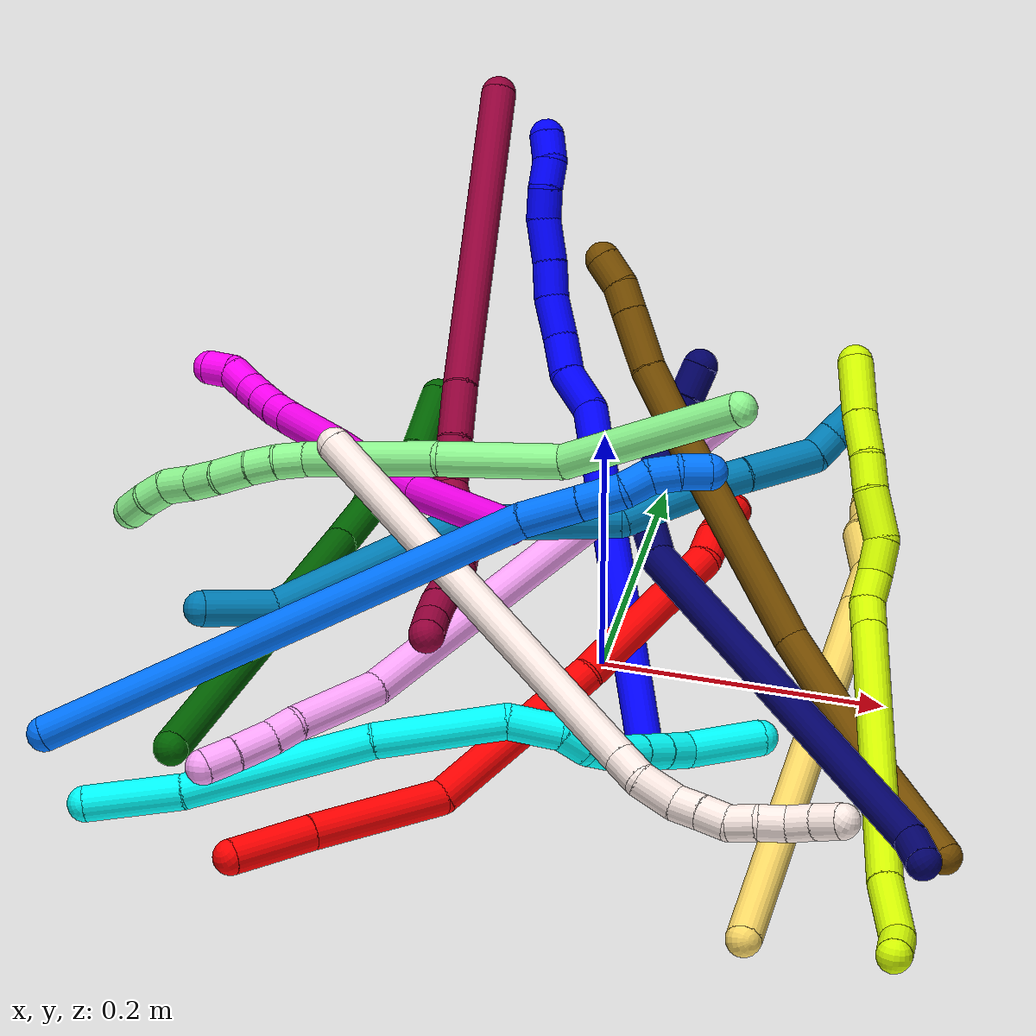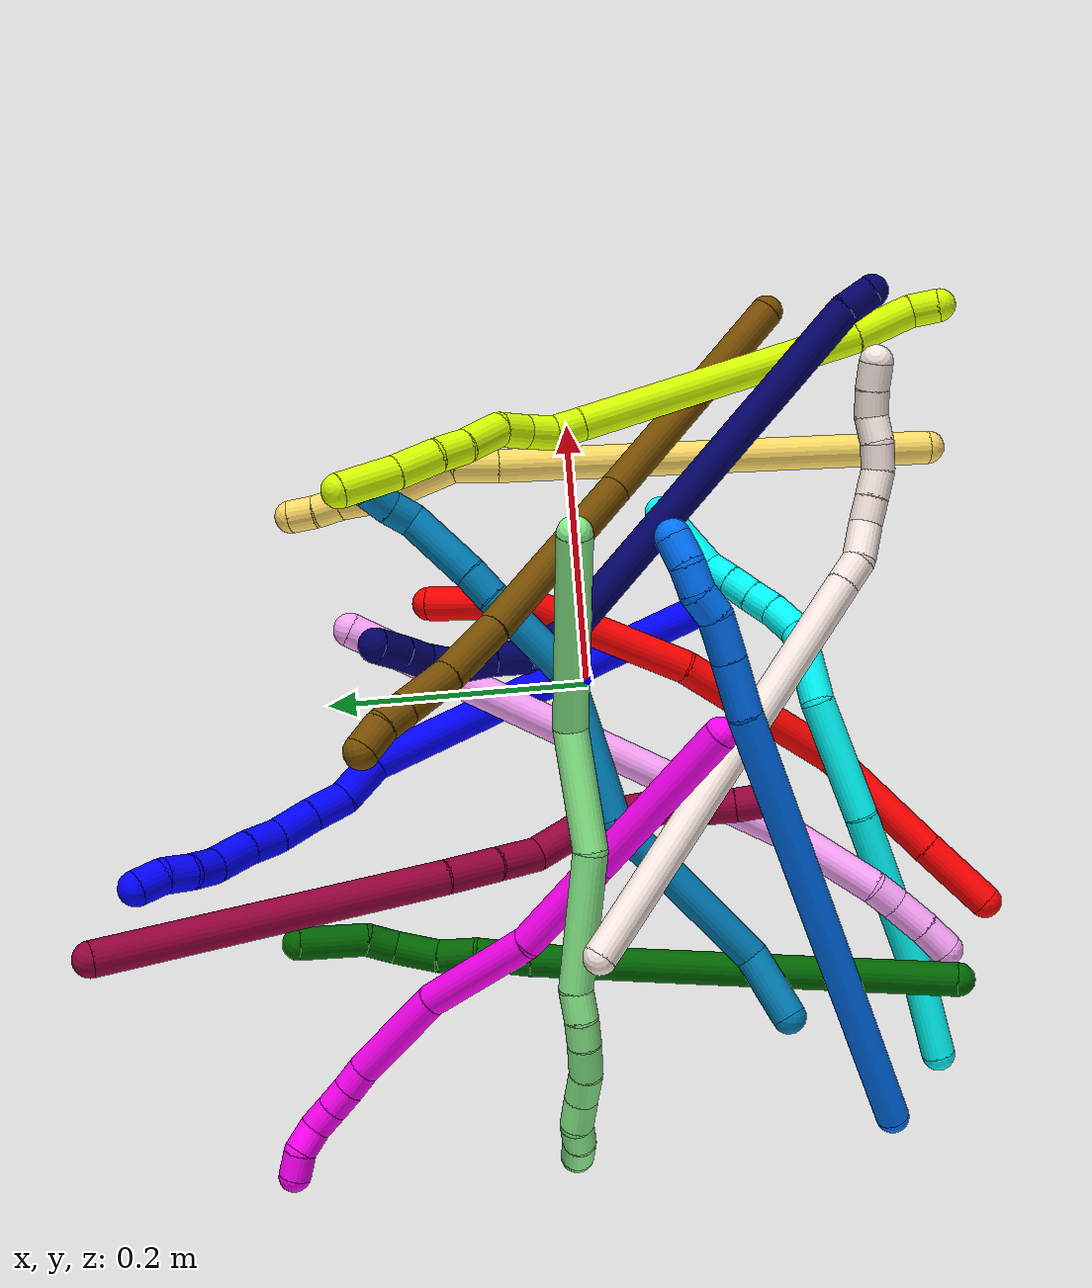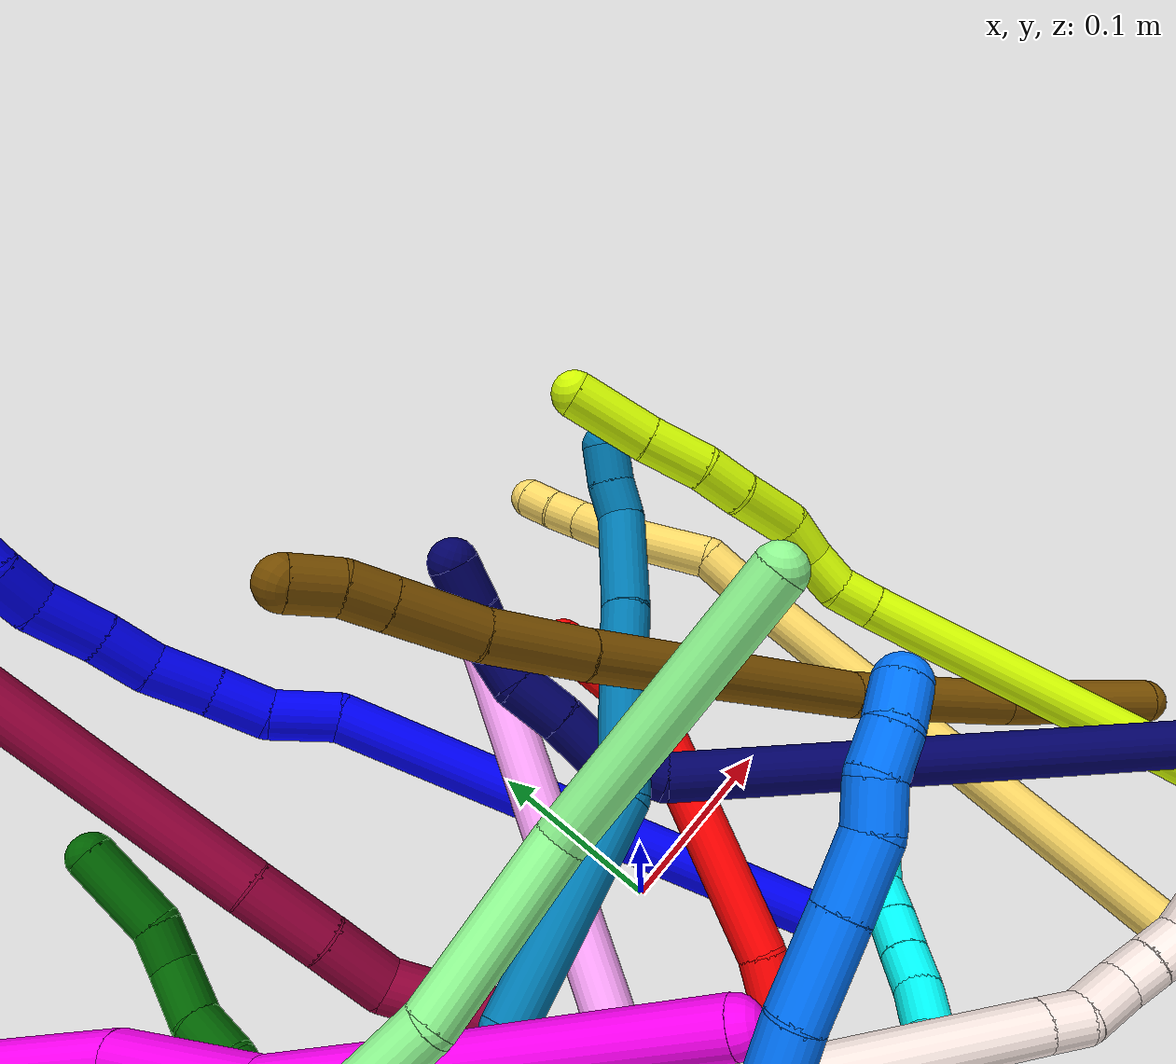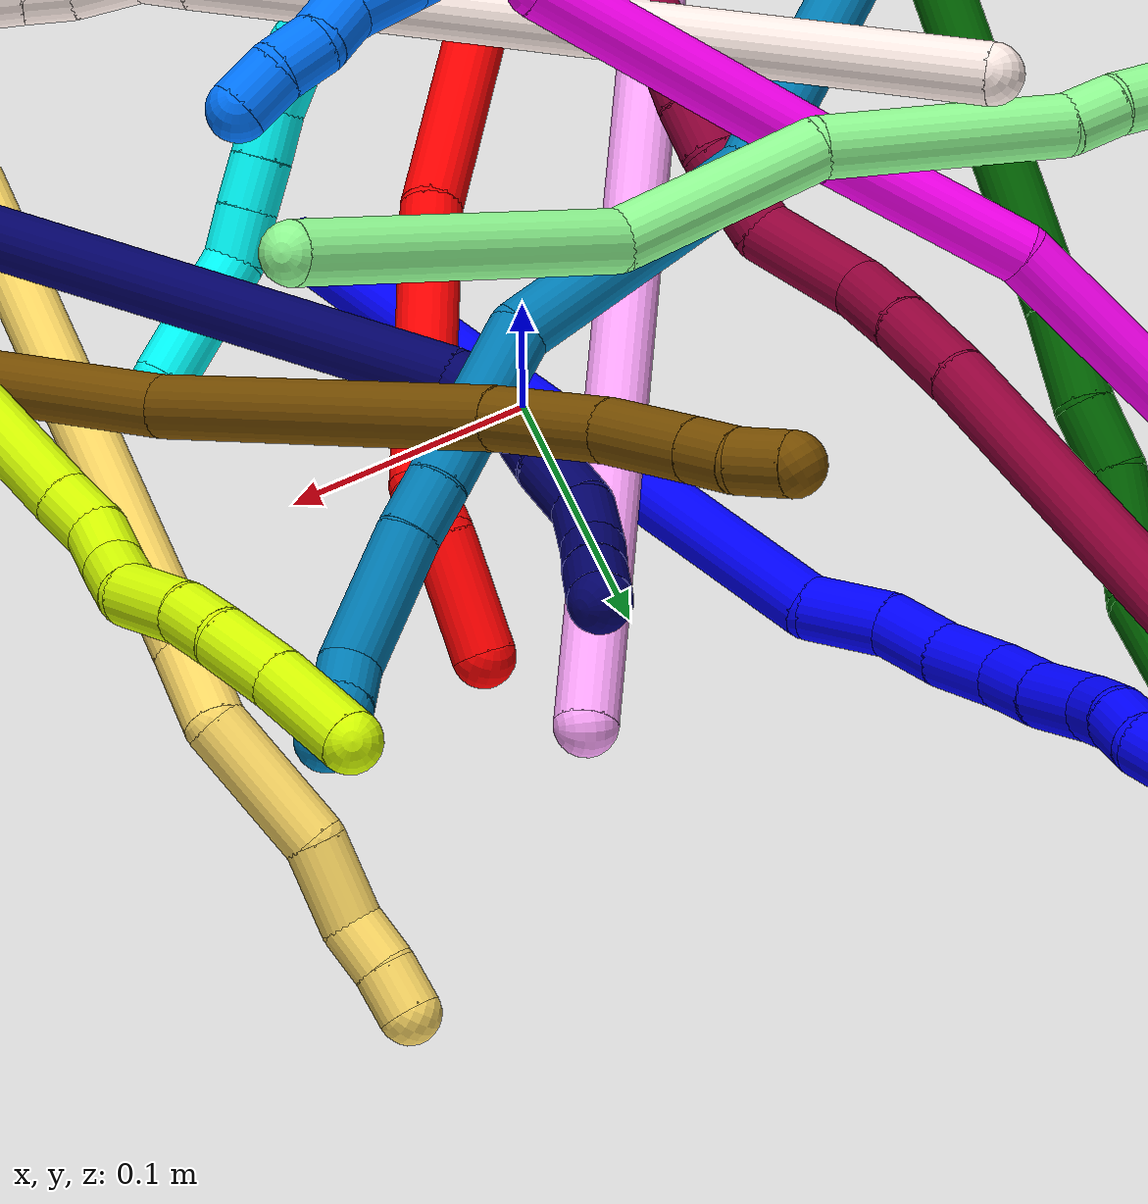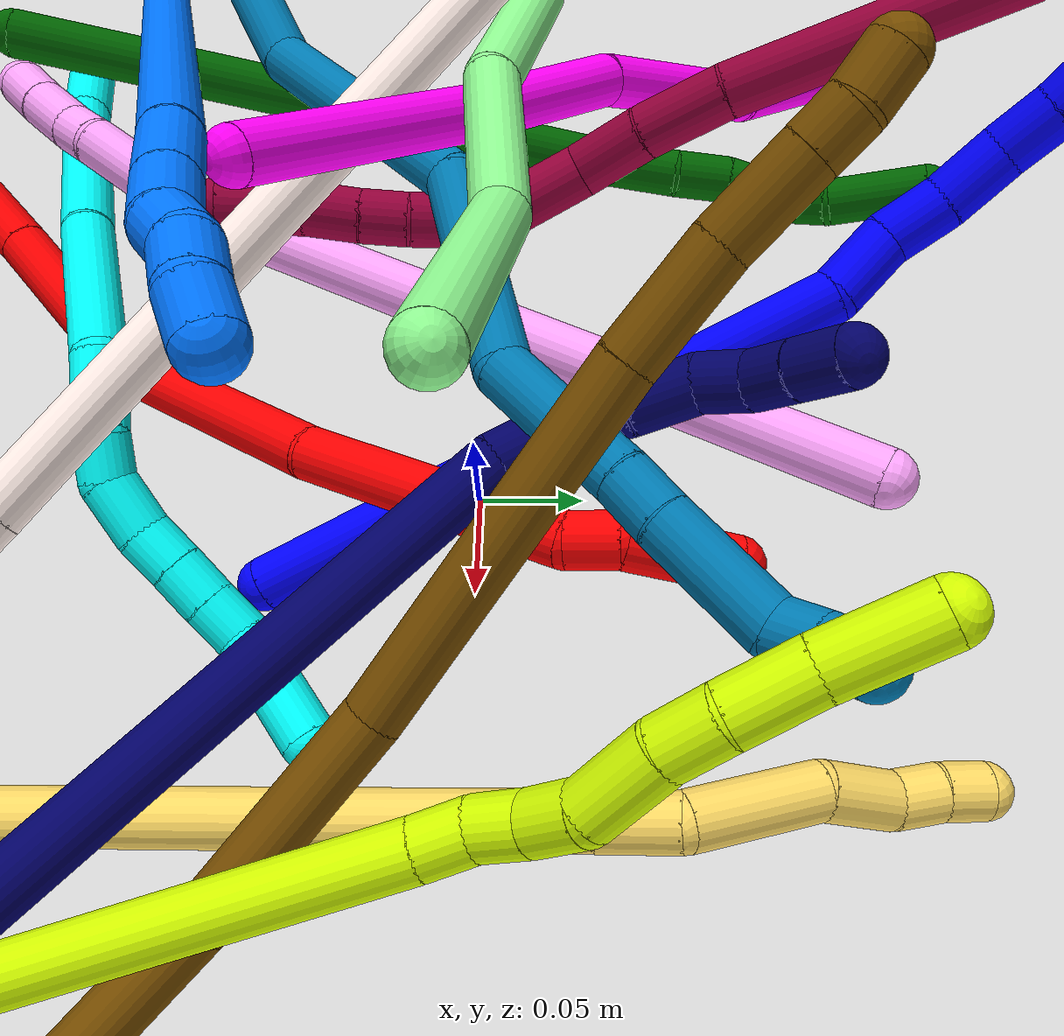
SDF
<sdf version="1.7">
 <world name="default">
  <plugin name="TubeGeneratorPlugin" filename="libtube_generator_plugin.so"/>
  <model name="photoneo_s_sensor">
   <static>1</static>
   <pose>0 0 2 1.57079 1.57079 3.14159</pose>
   <link name="link">
    <inertial><mass>0.1</mass></inertial>
    <sensor name="sensor" type="depth">
     <update_rate>30</update_rate>
     <camera>
      <horizontal_fov>1.22</horizontal_fov>
      <image><width>1920</width><height>1200</height><format>B8G8R8</format></image>
      <clip><near>0.1</near><far>4</far></clip>
      <depth_camera><output>points</output></depth_camera>
     </camera>
     <plugin name="camera_plugin" filename="libgazebo_ros_depth_camera.so">
      <baseline>0.2</baseline>
      <alwaysOn>1</alwaysOn>
      <updateRate>0.0</updateRate>
      <cameraName>camera_ir</cameraName>
      <imageTopicName>/camera/color/image_raw</imageTopicName>
      <cameraInfoTopicName>/camera/color/camera_info</cameraInfoTopicName>
      <depthImageTopicName>/camera/depth/image_raw</depthImageTopicName>
      <depthImageCameraInfoTopicName>/camera/depth/camera_info</depthImageCameraInfoTopicName>
      <pointCloudTopicName>/camera/depth/points</pointCloudTopicName>
      <frameName>fr_optical</frameName>
      <pointCloudCutoff>0.1</pointCloudCutoff>
      <pointCloudCutoffMax>2.0</pointCloudCutoffMax>
      <distortionK1>0</distortionK1>
      <distortionK2>0</distortionK2>
      <distortionK3>0</distortionK3>
      <distortionT1>0</distortionT1>
      <distortionT2>0</distortionT2>
      <CxPrime>0</CxPrime>
      <Cx>0</Cx>
      <Cy>0</Cy>
      <focalLength>0</focalLength>
      <hackBaseline>0</hackBaseline>
     </plugin>
    </sensor>
   </link>
  </model>
  <gravity>0 0 -9.8</gravity>
  <magnetic_field>6e-06 2.3e-05 -4.2e-05</magnetic_field>
  <atmosphere type="adiabatic"/>
  <physics name="default_physics" default="0" type="ode">
   <max_step_size>0.003</max_step_size>
   <real_time_factor>1</real_time_factor>
   <real_time_update_rate>1000</real_time_update_rate>
   <max_contacts>10000</max_contacts>
   <ode>
    <solver>
     <type>quick</type>
     <iters>100</iters>
     <sor>1.3</sor>
     <use_dynamic_moi_rescaling>0</use_dynamic_moi_rescaling>
    </solver>
    <constraints>
     <contact_max_correcting_vel>0</contact_max_correcting_vel>
     <contact_surface_layer>0.001</contact_surface_layer>
     <cfm>0</cfm>
     <erp>0.2</erp>
    </constraints>
   </ode>
  </physics>
  <scene><ambient>0.4 0.4 0.4 1</ambient><background>0.7 0.7 0.7 1</background><shadows>0</shadows></scene>
  <audio><device>default</device></audio>
  <spherical_coordinates>
   <surface_model>EARTH_WGS84</surface_model>
   <latitude_deg>0</latitude_deg>
   <longitude_deg>0</longitude_deg>
   <elevation>0</elevation>
   <heading_deg>0</heading_deg>
  </spherical_coordinates>
  <model name="bin">
   <static>1</static>
   <link name="bottom">
    <collision name="collision-bottom">
     <pose>0 0 -0.01 0 -0 0</pose>
     <geometry><box><size>0.8 0.6 0.02</size></box></geometry>
     <surface>
      <friction><ode><mu>100</mu><mu2>100</mu2></ode></friction>
      <contact><collide_bitmask>65535</collide_bitmask></contact>
     </surface>
    </collision>
   </link>
   <link name="west_wall">
    <collision name="collision-west_wall">
     <pose>-0.41 0 0.1 0 -0 0</pose>
     <geometry><box><size>0.02 0.6 0.2</size></box></geometry>
     <surface>
      <friction><ode><mu>100</mu><mu2>100</mu2></ode></friction>
      <contact><collide_bitmask>65535</collide_bitmask></contact>
     </surface>
    </collision>
   </link>
   <link name="east_wall">
    <collision name="collision-east_wall">
     <pose>0.41 0 0.1 0 -0 0</pose>
     <geometry><box><size>0.02 0.6 0.2</size></box></geometry>
     <surface>
      <friction><ode><mu>100</mu><mu2>100</mu2></ode></friction>
      <contact><collide_bitmask>65535</collide_bitmask></contact>
     </surface>
    </collision>
   </link>
   <link name="south_wall">
    <collision name="collision-south_wall">
     <pose>0 -0.31 0.1 0 -0 0</pose>
     <geometry><box><size>0.8 0.02 0.2</size></box></geometry>
     <surface>
      <friction><ode><mu>100</mu><mu2>100</mu2></ode></friction>
      <contact><collide_bitmask>65535</collide_bitmask></contact>
     </surface>
    </collision>
   </link>
   <link name="north_wall">
    <collision name="collision-north_wall">
     <pose>0 0.31 0.1 0 -0 0</pose>
     <geometry><box><size>0.8 0.02 0.2</size></box></geometry>
     <surface>
      <friction><ode><mu>100</mu><mu2>100</mu2></ode></friction>
      <contact><collide_bitmask>65535</collide_bitmask></contact>
     </surface>
    </collision>
   </link>
  </model>
  <model name="1">
   <static>0</static>
   <link name="1">
    <collision name="collision-cylinder-e_1_1_4">
     <pose>-0.072375 0.121578 0.019388 -1.41266 -0.531449 0.456309</pose>
     <geometry><cylinder><radius>0.0125</radius><length>0.285624</length></cylinder></geometry>
     <surface>
      <friction><ode><mu>1.16</mu><mu2>1.16</mu2><slip1>0</slip1><slip2>0</slip2></ode></friction>
      <contact><ode><kp>1e+06</kp><kd>1</kd><max_vel>0</max_vel><min_depth>0.001</min_depth></ode></contact>
     </surface>
    </collision>
    <visual name="visual-cylinder-e_1_1_4">
     <pose>-0.072375 0.121578 0.019388 -1.41266 -0.531449 0.456309</pose>
     <geometry><cylinder><radius>0.0125</radius><length>0.285624</length></cylinder></geometry>
     <material><ambient>0 0 1 1</ambient></material>
    </visual>
    <collision name="collision-cylinder-e_2_4_5">
     <pose>-0.147457 0.259191 0.043291 -1.29633 -0.161121 0.122132</pose>
     <geometry><cylinder><radius>0.0125</radius><length>0.033753</length></cylinder></geometry>
     <surface>
      <friction><ode><mu>1.16</mu><mu2>1.16</mu2><slip1>0</slip1><slip2>0</slip2></ode></friction>
      <contact><ode><kp>1e+06</kp><kd>1</kd><max_vel>0</max_vel><min_depth>0.001</min_depth></ode></contact>
     </surface>
    </collision>
    <visual name="visual-cylinder-e_2_4_5">
     <pose>-0.147457 0.259191 0.043291 -1.29633 -0.161121 0.122132</pose>
     <geometry><cylinder><radius>0.0125</radius><length>0.033753</length></cylinder></geometry>
     <material><ambient>0 0 1 1</ambient></material>
    </visual>
    <collision name="collision-cylinder-e_3_5_6">
     <pose>-0.156152 0.288277 0.048171 -1.54286 -0.429947 0.418446</pose>
     <geometry><cylinder><radius>0.0125</radius><length>0.028729</length></cylinder></geometry>
     <surface>
      <friction><ode><mu>1.16</mu><mu2>1.16</mu2><slip1>0</slip1><slip2>0</slip2></ode></friction>
      <contact><ode><kp>1e+06</kp><kd>1</kd><max_vel>0</max_vel><min_depth>0.001</min_depth></ode></contact>
     </surface>
    </collision>
    <visual name="visual-cylinder-e_3_5_6">
     <pose>-0.156152 0.288277 0.048171 -1.54286 -0.429947 0.418446</pose>
     <geometry><cylinder><radius>0.0125</radius><length>0.028729</length></cylinder></geometry>
     <material><ambient>0 0 1 1</ambient></material>
    </visual>
    <collision name="collision-cylinder-e_4_6_7">
     <pose>-0.166821 0.316141 0.047307 -1.65355 -0.305166 0.331065</pose>
     <geometry><cylinder><radius>0.0125</radius><length>0.031165</length></cylinder></geometry>
     <surface>
      <friction><ode><mu>1.16</mu><mu2>1.16</mu2><slip1>0</slip1><slip2>0</slip2></ode></friction>
      <contact><ode><kp>1e+06</kp><kd>1</kd><max_vel>0</max_vel><min_depth>0.001</min_depth></ode></contact>
     </surface>
    </collision>
    <visual name="visual-cylinder-e_4_6_7">
     <pose>-0.166821 0.316141 0.047307 -1.65355 -0.305166 0.331065</pose>
     <geometry><cylinder><radius>0.0125</radius><length>0.031165</length></cylinder></geometry>
     <material><ambient>0 0 1 1</ambient></material>
    </visual>
    <collision name="collision-cylinder-e_5_7_8">
     <pose>-0.176123 0.342845 0.042401 -1.8707 -0.355399 0.477741</pose>
     <geometry><cylinder><radius>0.0125</radius><length>0.026556</length></cylinder></geometry>
     <surface>
      <friction><ode><mu>1.16</mu><mu2>1.16</mu2><slip1>0</slip1><slip2>0</slip2></ode></friction>
      <contact><ode><kp>1e+06</kp><kd>1</kd><max_vel>0</max_vel><min_depth>0.001</min_depth></ode></contact>
     </surface>
    </collision>
    <visual name="visual-cylinder-e_5_7_8">
     <pose>-0.176123 0.342845 0.042401 -1.8707 -0.355399 0.477741</pose>
     <geometry><cylinder><radius>0.0125</radius><length>0.026556</length></cylinder></geometry>
     <material><ambient>0 0 1 1</ambient></material>
    </visual>
    <collision name="collision-cylinder-e_6_8_9">
     <pose>-0.184571 0.369405 0.034535 -1.84896 -0.245862 0.32467</pose>
     <geometry><cylinder><radius>0.0125</radius><length>0.031454</length></cylinder></geometry>
     <surface>
      <friction><ode><mu>1.16</mu><mu2>1.16</mu2><slip1>0</slip1><slip2>0</slip2></ode></friction>
      <contact><ode><kp>1e+06</kp><kd>1</kd><max_vel>0</max_vel><min_depth>0.001</min_depth></ode></contact>
     </surface>
    </collision>
    <visual name="visual-cylinder-e_6_8_9">
     <pose>-0.184571 0.369405 0.034535 -1.84896 -0.245862 0.32467</pose>
     <geometry><cylinder><radius>0.0125</radius><length>0.031454</length></cylinder></geometry>
     <material><ambient>0 0 1 1</ambient></material>
    </visual>
    <collision name="collision-cylinder-e_7_9_10">
     <pose>-0.191551 0.393134 0.024973 -2.10607 -0.290761 0.503203</pose>
     <geometry><cylinder><radius>0.0125</radius><length>0.021992</length></cylinder></geometry>
     <surface>
      <friction><ode><mu>1.16</mu><mu2>1.16</mu2><slip1>0</slip1><slip2>0</slip2></ode></friction>
      <contact><ode><kp>1e+06</kp><kd>1</kd><max_vel>0</max_vel><min_depth>0.001</min_depth></ode></contact>
     </surface>
    </collision>
    <visual name="visual-cylinder-e_7_9_10">
     <pose>-0.191551 0.393134 0.024973 -2.10607 -0.290761 0.503203</pose>
     <geometry><cylinder><radius>0.0125</radius><length>0.021992</length></cylinder></geometry>
     <material><ambient>0 0 1 1</ambient></material>
    </visual>
    <collision name="collision-cylinder-e_8_10_11">
     <pose>-0.20004 0.410241 0.016055 -1.98582 -0.545467 0.810323</pose>
     <geometry><cylinder><radius>0.0125</radius><length>0.020571</length></cylinder></geometry>
     <surface>
      <friction><ode><mu>1.16</mu><mu2>1.16</mu2><slip1>0</slip1><slip2>0</slip2></ode></friction>
      <contact><ode><kp>1e+06</kp><kd>1</kd><max_vel>0</max_vel><min_depth>0.001</min_depth></ode></contact>
     </surface>
    </collision>
    <visual name="visual-cylinder-e_8_10_11">
     <pose>-0.20004 0.410241 0.016055 -1.98582 -0.545467 0.810323</pose>
     <geometry><cylinder><radius>0.0125</radius><length>0.020571</length></cylinder></geometry>
     <material><ambient>0 0 1 1</ambient></material>
    </visual>
    <collision name="collision-cylinder-e_9_11_2">
     <pose>-0.209674 0.427384 0.011907 -1.63696 -0.440567 0.469663</pose>
     <geometry><cylinder><radius>0.0125</radius><length>0.020157</length></cylinder></geometry>
     <surface>
      <friction><ode><mu>1.16</mu><mu2>1.16</mu2><slip1>0</slip1><slip2>0</slip2></ode></friction>
      <contact><ode><kp>1e+06</kp><kd>1</kd><max_vel>0</max_vel><min_depth>0.001</min_depth></ode></contact>
     </surface>
    </collision>
    <visual name="visual-cylinder-e_9_11_2">
     <pose>-0.209674 0.427384 0.011907 -1.63696 -0.440567 0.469663</pose>
     <geometry><cylinder><radius>0.0125</radius><length>0.020157</length></cylinder></geometry>
     <material><ambient>0 0 1 1</ambient></material>
    </visual>
    <collision name="collision-sphere-2">
     <pose>-0.213972 0.43648 0.011304 0 -0 0</pose>
     <geometry><sphere><radius>0.0125</radius></sphere></geometry>
     <surface>
      <friction><ode><mu>1.16</mu><mu2>1.16</mu2><slip1>0</slip1><slip2>0</slip2></ode></friction>
      <contact><ode><kp>1e+06</kp><kd>1</kd><max_vel>0</max_vel><min_depth>0.001</min_depth></ode></contact>
     </surface>
    </collision>
    <visual name="visual-sphere-2">
     <pose>-0.213972 0.43648 0.011304 0 -0 0</pose>
     <geometry><sphere><radius>0.0125</radius></sphere></geometry>
     <material><ambient>0 0 1 1</ambient></material>
    </visual>
    <collision name="collision-sphere-11">
     <pose>-0.205376 0.418288 0.012509 0 -0 0</pose>
     <geometry><sphere><radius>0.0125</radius></sphere></geometry>
     <surface>
      <friction><ode><mu>1.16</mu><mu2>1.16</mu2><slip1>0</slip1><slip2>0</slip2></ode></friction>
      <contact><ode><kp>1e+06</kp><kd>1</kd><max_vel>0</max_vel><min_depth>0.001</min_depth></ode></contact>
     </surface>
    </collision>
    <visual name="visual-sphere-11">
     <pose>-0.205376 0.418288 0.012509 0 -0 0</pose>
     <geometry><sphere><radius>0.0125</radius></sphere></geometry>
     <material><ambient>0 0 1 1</ambient></material>
    </visual>
    <collision name="collision-sphere-10">
     <pose>-0.194704 0.402195 0.0196 0 -0 0</pose>
     <geometry><sphere><radius>0.0125</radius></sphere></geometry>
     <surface>
      <friction><ode><mu>1.16</mu><mu2>1.16</mu2><slip1>0</slip1><slip2>0</slip2></ode></friction>
      <contact><ode><kp>1e+06</kp><kd>1</kd><max_vel>0</max_vel><min_depth>0.001</min_depth></ode></contact>
     </surface>
    </collision>
    <visual name="visual-sphere-10">
     <pose>-0.194704 0.402195 0.0196 0 -0 0</pose>
     <geometry><sphere><radius>0.0125</radius></sphere></geometry>
     <material><ambient>0 0 1 1</ambient></material>
    </visual>
    <collision name="collision-sphere-9">
     <pose>-0.188399 0.384073 0.030347 0 -0 0</pose>
     <geometry><sphere><radius>0.0125</radius></sphere></geometry>
     <surface>
      <friction><ode><mu>1.16</mu><mu2>1.16</mu2><slip1>0</slip1><slip2>0</slip2></ode></friction>
      <contact><ode><kp>1e+06</kp><kd>1</kd><max_vel>0</max_vel><min_depth>0.001</min_depth></ode></contact>
     </surface>
    </collision>
    <visual name="visual-sphere-9">
     <pose>-0.188399 0.384073 0.030347 0 -0 0</pose>
     <geometry><sphere><radius>0.0125</radius></sphere></geometry>
     <material><ambient>0 0 1 1</ambient></material>
    </visual>
    <collision name="collision-sphere-4">
     <pose>-0.144749 0.243156 0.038777 0 -0 0</pose>
     <geometry><sphere><radius>0.0125</radius></sphere></geometry>
     <surface>
      <friction><ode><mu>1.16</mu><mu2>1.16</mu2><slip1>0</slip1><slip2>0</slip2></ode></friction>
      <contact><ode><kp>1e+06</kp><kd>1</kd><max_vel>0</max_vel><min_depth>0.001</min_depth></ode></contact>
     </surface>
    </collision>
    <visual name="visual-sphere-4">
     <pose>-0.144749 0.243156 0.038777 0 -0 0</pose>
     <geometry><sphere><radius>0.0125</radius></sphere></geometry>
     <material><ambient>0 0 1 1</ambient></material>
    </visual>
    <collision name="collision-sphere-1">
     <geometry><sphere><radius>0.0125</radius></sphere></geometry>
     <surface>
      <friction><ode><mu>1.16</mu><mu2>1.16</mu2><slip1>0</slip1><slip2>0</slip2></ode></friction>
      <contact><ode><kp>1e+06</kp><kd>1</kd><max_vel>0</max_vel><min_depth>0.001</min_depth></ode></contact>
     </surface>
    </collision>
    <visual name="visual-sphere-1">
     <geometry><sphere><radius>0.0125</radius></sphere></geometry>
     <material><ambient>0 0 1 1</ambient></material>
    </visual>
    <collision name="collision-sphere-8">
     <pose>-0.180743 0.354738 0.038724 0 -0 0</pose>
     <geometry><sphere><radius>0.0125</radius></sphere></geometry>
     <surface>
      <friction><ode><mu>1.16</mu><mu2>1.16</mu2><slip1>0</slip1><slip2>0</slip2></ode></friction>
      <contact><ode><kp>1e+06</kp><kd>1</kd><max_vel>0</max_vel><min_depth>0.001</min_depth></ode></contact>
     </surface>
    </collision>
    <visual name="visual-sphere-8">
     <pose>-0.180743 0.354738 0.038724 0 -0 0</pose>
     <geometry><sphere><radius>0.0125</radius></sphere></geometry>
     <material><ambient>0 0 1 1</ambient></material>
    </visual>
    <collision name="collision-sphere-5">
     <pose>-0.150164 0.275225 0.047806 0 -0 0</pose>
     <geometry><sphere><radius>0.0125</radius></sphere></geometry>
     <surface>
      <friction><ode><mu>1.16</mu><mu2>1.16</mu2><slip1>0</slip1><slip2>0</slip2></ode></friction>
      <contact><ode><kp>1e+06</kp><kd>1</kd><max_vel>0</max_vel><min_depth>0.001</min_depth></ode></contact>
     </surface>
    </collision>
    <visual name="visual-sphere-5">
     <pose>-0.150164 0.275225 0.047806 0 -0 0</pose>
     <geometry><sphere><radius>0.0125</radius></sphere></geometry>
     <material><ambient>0 0 1 1</ambient></material>
    </visual>
    <collision name="collision-sphere-6">
     <pose>-0.162139 0.30133 0.048536 0 -0 0</pose>
     <geometry><sphere><radius>0.0125</radius></sphere></geometry>
     <surface>
      <friction><ode><mu>1.16</mu><mu2>1.16</mu2><slip1>0</slip1><slip2>0</slip2></ode></friction>
      <contact><ode><kp>1e+06</kp><kd>1</kd><max_vel>0</max_vel><min_depth>0.001</min_depth></ode></contact>
     </surface>
    </collision>
    <visual name="visual-sphere-6">
     <pose>-0.162139 0.30133 0.048536 0 -0 0</pose>
     <geometry><sphere><radius>0.0125</radius></sphere></geometry>
     <material><ambient>0 0 1 1</ambient></material>
    </visual>
    <collision name="collision-sphere-7">
     <pose>-0.171503 0.330953 0.046079 0 -0 0</pose>
     <geometry><sphere><radius>0.0125</radius></sphere></geometry>
     <surface>
      <friction><ode><mu>1.16</mu><mu2>1.16</mu2><slip1>0</slip1><slip2>0</slip2></ode></friction>
      <contact><ode><kp>1e+06</kp><kd>1</kd><max_vel>0</max_vel><min_depth>0.001</min_depth></ode></contact>
     </surface>
    </collision>
    <visual name="visual-sphere-7">
     <pose>-0.171503 0.330953 0.046079 0 -0 0</pose>
     <geometry><sphere><radius>0.0125</radius></sphere></geometry>
     <material><ambient>0 0 1 1</ambient></material>
    </visual>
    <inertial>
     <pose>-0.116741 0.216063 0.026378 0 -0 0</pose>
     <mass>0.5</mass>
     <inertia>
      <ixx>0.002264</ixx>
      <ixy>0</ixy>
      <ixz>0</ixz>
      <iyy>0.001491</iyy>
      <iyz>0</iyz>
      <izz>-0.000686</izz>
     </inertia>
    </inertial>
   </link>
   <pose>0.051925 -0.095029 0.011478 2.50483 -0.176427 -2.13163</pose>
  </model>
  <model name="2">
   <static>0</static>
   <link name="2">
    <collision name="collision-cylinder-e_1_1_4">
     <pose>0.017904 0.017554 0.016582 -0.813855 0.637984 -0.282783</pose>
     <geometry><cylinder><radius>0.0125</radius><length>0.060122</length></cylinder></geometry>
     <surface>
      <friction><ode><mu>1.16</mu><mu2>1.16</mu2><slip1>0</slip1><slip2>0</slip2></ode></friction>
      <contact><ode><kp>1e+06</kp><kd>1</kd><max_vel>0</max_vel><min_depth>0.001</min_depth></ode></contact>
     </surface>
    </collision>
    <visual name="visual-cylinder-e_1_1_4">
     <pose>0.017904 0.017554 0.016582 -0.813855 0.637984 -0.282783</pose>
     <geometry><cylinder><radius>0.0125</radius><length>0.060122</length></cylinder></geometry>
     <material><ambient>1 0 0 1</ambient></material>
    </visual>
    <collision name="collision-cylinder-e_2_4_5">
     <pose>0.064543 0.064239 0.061764 -0.794617 0.613343 -0.26421</pose>
     <geometry><cylinder><radius>0.0125</radius><length>0.099844</length></cylinder></geometry>
     <surface>
      <friction><ode><mu>1.16</mu><mu2>1.16</mu2><slip1>0</slip1><slip2>0</slip2></ode></friction>
      <contact><ode><kp>1e+06</kp><kd>1</kd><max_vel>0</max_vel><min_depth>0.001</min_depth></ode></contact>
     </surface>
    </collision>
    <visual name="visual-cylinder-e_2_4_5">
     <pose>0.064543 0.064239 0.061764 -0.794617 0.613343 -0.26421</pose>
     <geometry><cylinder><radius>0.0125</radius><length>0.099844</length></cylinder></geometry>
     <material><ambient>1 0 0 1</ambient></material>
    </visual>
    <collision name="collision-cylinder-e_3_5_6">
     <pose>0.148338 0.13157 0.105333 -1.1973 0.930391 -0.659773</pose>
     <geometry><cylinder><radius>0.0125</radius><length>0.13733</length></cylinder></geometry>
     <surface>
      <friction><ode><mu>1.16</mu><mu2>1.16</mu2><slip1>0</slip1><slip2>0</slip2></ode></friction>
      <contact><ode><kp>1e+06</kp><kd>1</kd><max_vel>0</max_vel><min_depth>0.001</min_depth></ode></contact>
     </surface>
    </collision>
    <visual name="visual-cylinder-e_3_5_6">
     <pose>0.148338 0.13157 0.105333 -1.1973 0.930391 -0.659773</pose>
     <geometry><cylinder><radius>0.0125</radius><length>0.13733</length></cylinder></geometry>
     <material><ambient>1 0 0 1</ambient></material>
    </visual>
    <collision name="collision-cylinder-e_4_6_7">
     <pose>0.260349 0.194905 0.13913 -0.927907 1.06688 -0.574645</pose>
     <geometry><cylinder><radius>0.0125</radius><length>0.130073</length></cylinder></geometry>
     <surface>
      <friction><ode><mu>1.16</mu><mu2>1.16</mu2><slip1>0</slip1><slip2>0</slip2></ode></friction>
      <contact><ode><kp>1e+06</kp><kd>1</kd><max_vel>0</max_vel><min_depth>0.001</min_depth></ode></contact>
     </surface>
    </collision>
    <visual name="visual-cylinder-e_4_6_7">
     <pose>0.260349 0.194905 0.13913 -0.927907 1.06688 -0.574645</pose>
     <geometry><cylinder><radius>0.0125</radius><length>0.130073</length></cylinder></geometry>
     <material><ambient>1 0 0 1</ambient></material>
    </visual>
    <collision name="collision-cylinder-e_5_7_8">
     <pose>0.328868 0.22028 0.160271 -0.103925 1.37231 -0.085129</pose>
     <geometry><cylinder><radius>0.0125</radius><length>0.023595</length></cylinder></geometry>
     <surface>
      <friction><ode><mu>1.16</mu><mu2>1.16</mu2><slip1>0</slip1><slip2>0</slip2></ode></friction>
      <contact><ode><kp>1e+06</kp><kd>1</kd><max_vel>0</max_vel><min_depth>0.001</min_depth></ode></contact>
     </surface>
    </collision>
    <visual name="visual-cylinder-e_5_7_8">
     <pose>0.328868 0.22028 0.160271 -0.103925 1.37231 -0.085129</pose>
     <geometry><cylinder><radius>0.0125</radius><length>0.023595</length></cylinder></geometry>
     <material><ambient>1 0 0 1</ambient></material>
    </visual>
    <collision name="collision-cylinder-e_6_8_2">
     <pose>0.361342 0.217957 0.17513 0.201649 1.02128 0.113226</pose>
     <geometry><cylinder><radius>0.0125</radius><length>0.049035</length></cylinder></geometry>
     <surface>
      <friction><ode><mu>1.16</mu><mu2>1.16</mu2><slip1>0</slip1><slip2>0</slip2></ode></friction>
      <contact><ode><kp>1e+06</kp><kd>1</kd><max_vel>0</max_vel><min_depth>0.001</min_depth></ode></contact>
     </surface>
    </collision>
    <visual name="visual-cylinder-e_6_8_2">
     <pose>0.361342 0.217957 0.17513 0.201649 1.02128 0.113226</pose>
     <geometry><cylinder><radius>0.0125</radius><length>0.049035</length></cylinder></geometry>
     <material><ambient>1 0 0 1</ambient></material>
    </visual>
    <collision name="collision-sphere-2">
     <pose>0.382249 0.215392 0.187675 0 -0 0</pose>
     <geometry><sphere><radius>0.0125</radius></sphere></geometry>
     <surface>
      <friction><ode><mu>1.16</mu><mu2>1.16</mu2><slip1>0</slip1><slip2>0</slip2></ode></friction>
      <contact><ode><kp>1e+06</kp><kd>1</kd><max_vel>0</max_vel><min_depth>0.001</min_depth></ode></contact>
     </surface>
    </collision>
    <visual name="visual-sphere-2">
     <pose>0.382249 0.215392 0.187675 0 -0 0</pose>
     <geometry><sphere><radius>0.0125</radius></sphere></geometry>
     <material><ambient>1 0 0 1</ambient></material>
    </visual>
    <collision name="collision-sphere-4">
     <pose>0.035807 0.035108 0.033165 0 -0 0</pose>
     <geometry><sphere><radius>0.0125</radius></sphere></geometry>
     <surface>
      <friction><ode><mu>1.16</mu><mu2>1.16</mu2><slip1>0</slip1><slip2>0</slip2></ode></friction>
      <contact><ode><kp>1e+06</kp><kd>1</kd><max_vel>0</max_vel><min_depth>0.001</min_depth></ode></contact>
     </surface>
    </collision>
    <visual name="visual-sphere-4">
     <pose>0.035807 0.035108 0.033165 0 -0 0</pose>
     <geometry><sphere><radius>0.0125</radius></sphere></geometry>
     <material><ambient>1 0 0 1</ambient></material>
    </visual>
    <collision name="collision-sphere-1">
     <geometry><sphere><radius>0.0125</radius></sphere></geometry>
     <surface>
      <friction><ode><mu>1.16</mu><mu2>1.16</mu2><slip1>0</slip1><slip2>0</slip2></ode></friction>
      <contact><ode><kp>1e+06</kp><kd>1</kd><max_vel>0</max_vel><min_depth>0.001</min_depth></ode></contact>
     </surface>
    </collision>
    <visual name="visual-sphere-1">
     <geometry><sphere><radius>0.0125</radius></sphere></geometry>
     <material><ambient>1 0 0 1</ambient></material>
    </visual>
    <collision name="collision-sphere-8">
     <pose>0.340434 0.220522 0.162584 0 -0 0</pose>
     <geometry><sphere><radius>0.0125</radius></sphere></geometry>
     <surface>
      <friction><ode><mu>1.16</mu><mu2>1.16</mu2><slip1>0</slip1><slip2>0</slip2></ode></friction>
      <contact><ode><kp>1e+06</kp><kd>1</kd><max_vel>0</max_vel><min_depth>0.001</min_depth></ode></contact>
     </surface>
    </collision>
    <visual name="visual-sphere-8">
     <pose>0.340434 0.220522 0.162584 0 -0 0</pose>
     <geometry><sphere><radius>0.0125</radius></sphere></geometry>
     <material><ambient>1 0 0 1</ambient></material>
    </visual>
    <collision name="collision-sphere-5">
     <pose>0.093278 0.09337 0.090362 0 -0 0</pose>
     <geometry><sphere><radius>0.0125</radius></sphere></geometry>
     <surface>
      <friction><ode><mu>1.16</mu><mu2>1.16</mu2><slip1>0</slip1><slip2>0</slip2></ode></friction>
      <contact><ode><kp>1e+06</kp><kd>1</kd><max_vel>0</max_vel><min_depth>0.001</min_depth></ode></contact>
     </surface>
    </collision>
    <visual name="visual-sphere-5">
     <pose>0.093278 0.09337 0.090362 0 -0 0</pose>
     <geometry><sphere><radius>0.0125</radius></sphere></geometry>
     <material><ambient>1 0 0 1</ambient></material>
    </visual>
    <collision name="collision-sphere-6">
     <pose>0.203397 0.169771 0.120303 0 -0 0</pose>
     <geometry><sphere><radius>0.0125</radius></sphere></geometry>
     <surface>
      <friction><ode><mu>1.16</mu><mu2>1.16</mu2><slip1>0</slip1><slip2>0</slip2></ode></friction>
      <contact><ode><kp>1e+06</kp><kd>1</kd><max_vel>0</max_vel><min_depth>0.001</min_depth></ode></contact>
     </surface>
    </collision>
    <visual name="visual-sphere-6">
     <pose>0.203397 0.169771 0.120303 0 -0 0</pose>
     <geometry><sphere><radius>0.0125</radius></sphere></geometry>
     <material><ambient>1 0 0 1</ambient></material>
    </visual>
    <collision name="collision-sphere-7">
     <pose>0.317302 0.220039 0.157957 0 -0 0</pose>
     <geometry><sphere><radius>0.0125</radius></sphere></geometry>
     <surface>
      <friction><ode><mu>1.16</mu><mu2>1.16</mu2><slip1>0</slip1><slip2>0</slip2></ode></friction>
      <contact><ode><kp>1e+06</kp><kd>1</kd><max_vel>0</max_vel><min_depth>0.001</min_depth></ode></contact>
     </surface>
    </collision>
    <visual name="visual-sphere-7">
     <pose>0.317302 0.220039 0.157957 0 -0 0</pose>
     <geometry><sphere><radius>0.0125</radius></sphere></geometry>
     <material><ambient>1 0 0 1</ambient></material>
    </visual>
    <inertial>
     <pose>0.174469 0.13355 0.104191 0 -0 0</pose>
     <mass>0.5</mass>
     <inertia>
      <ixx>0.000149</ixx>
      <ixy>0</ixy>
      <ixz>0</ixz>
      <iyy>0.000293</iyy>
      <iyz>0</iyz>
      <izz>-0.000659</izz>
     </inertia>
    </inertial>
   </link>
   <pose>-0.189249 -0.287271 0.023207 2.67477 -0.284861 1.62058</pose>
  </model>
  <model name="3">
   <static>0</static>
   <link name="3">
    <collision name="collision-cylinder-e_1_1_4">
     <pose>0.031557 0.009699 0.00982 -0.779204 1.15847 -0.524733</pose>
     <geometry><cylinder><radius>0.0125</radius><length>0.068887</length></cylinder></geometry>
     <surface>
      <friction><ode><mu>1.16</mu><mu2>1.16</mu2><slip1>0</slip1><slip2>0</slip2></ode></friction>
      <contact><ode><kp>1e+06</kp><kd>1</kd><max_vel>0</max_vel><min_depth>0.001</min_depth></ode></contact>
     </surface>
    </collision>
    <visual name="visual-cylinder-e_1_1_4">
     <pose>0.031557 0.009699 0.00982 -0.779204 1.15847 -0.524733</pose>
     <geometry><cylinder><radius>0.0125</radius><length>0.068887</length></cylinder></geometry>
     <material><ambient>0.003922 1 0.996078 1</ambient></material>
    </visual>
    <collision name="collision-cylinder-e_2_4_5">
     <pose>0.122053 0.047101 0.037172 -1.00657 1.06318 -0.626233</pose>
     <geometry><cylinder><radius>0.0125</radius><length>0.134886</length></cylinder></geometry>
     <surface>
      <friction><ode><mu>1.16</mu><mu2>1.16</mu2><slip1>0</slip1><slip2>0</slip2></ode></friction>
      <contact><ode><kp>1e+06</kp><kd>1</kd><max_vel>0</max_vel><min_depth>0.001</min_depth></ode></contact>
     </surface>
    </collision>
    <visual name="visual-cylinder-e_2_4_5">
     <pose>0.122053 0.047101 0.037172 -1.00657 1.06318 -0.626233</pose>
     <geometry><cylinder><radius>0.0125</radius><length>0.134886</length></cylinder></geometry>
     <material><ambient>0.003922 1 0.996078 1</ambient></material>
    </visual>
    <collision name="collision-cylinder-e_3_5_6">
     <pose>0.223697 0.088868 0.062576 -1.06055 1.20993 -0.77028</pose>
     <geometry><cylinder><radius>0.0125</radius><length>0.091292</length></cylinder></geometry>
     <surface>
      <friction><ode><mu>1.16</mu><mu2>1.16</mu2><slip1>0</slip1><slip2>0</slip2></ode></friction>
      <contact><ode><kp>1e+06</kp><kd>1</kd><max_vel>0</max_vel><min_depth>0.001</min_depth></ode></contact>
     </surface>
    </collision>
    <visual name="visual-cylinder-e_3_5_6">
     <pose>0.223697 0.088868 0.062576 -1.06055 1.20993 -0.77028</pose>
     <geometry><cylinder><radius>0.0125</radius><length>0.091292</length></cylinder></geometry>
     <material><ambient>0.003922 1 0.996078 1</ambient></material>
    </visual>
    <collision name="collision-cylinder-e_4_6_7">
     <pose>0.285206 0.102331 0.071845 0.405905 1.49005 0.375148</pose>
     <geometry><cylinder><radius>0.0125</radius><length>0.037728</length></cylinder></geometry>
     <surface>
      <friction><ode><mu>1.16</mu><mu2>1.16</mu2><slip1>0</slip1><slip2>0</slip2></ode></friction>
      <contact><ode><kp>1e+06</kp><kd>1</kd><max_vel>0</max_vel><min_depth>0.001</min_depth></ode></contact>
     </surface>
    </collision>
    <visual name="visual-cylinder-e_4_6_7">
     <pose>0.285206 0.102331 0.071845 0.405905 1.49005 0.375148</pose>
     <geometry><cylinder><radius>0.0125</radius><length>0.037728</length></cylinder></geometry>
     <material><ambient>0.003922 1 0.996078 1</ambient></material>
    </visual>
    <collision name="collision-cylinder-e_5_7_8">
     <pose>0.313624 0.098136 0.071054 2.11766 1.15823 1.72178</pose>
     <geometry><cylinder><radius>0.0125</radius><length>0.020993</length></cylinder></geometry>
     <surface>
      <friction><ode><mu>1.16</mu><mu2>1.16</mu2><slip1>0</slip1><slip2>0</slip2></ode></friction>
      <contact><ode><kp>1e+06</kp><kd>1</kd><max_vel>0</max_vel><min_depth>0.001</min_depth></ode></contact>
     </surface>
    </collision>
    <visual name="visual-cylinder-e_5_7_8">
     <pose>0.313624 0.098136 0.071054 2.11766 1.15823 1.72178</pose>
     <geometry><cylinder><radius>0.0125</radius><length>0.020993</length></cylinder></geometry>
     <material><ambient>0.003922 1 0.996078 1</ambient></material>
    </visual>
    <collision name="collision-cylinder-e_6_8_9">
     <pose>0.334978 0.094437 0.062027 3.12648 1.04319 3.11529</pose>
     <geometry><cylinder><radius>0.0125</radius><length>0.027169</length></cylinder></geometry>
     <surface>
      <friction><ode><mu>1.16</mu><mu2>1.16</mu2><slip1>0</slip1><slip2>0</slip2></ode></friction>
      <contact><ode><kp>1e+06</kp><kd>1</kd><max_vel>0</max_vel><min_depth>0.001</min_depth></ode></contact>
     </surface>
    </collision>
    <visual name="visual-cylinder-e_6_8_9">
     <pose>0.334978 0.094437 0.062027 3.12648 1.04319 3.11529</pose>
     <geometry><cylinder><radius>0.0125</radius><length>0.027169</length></cylinder></geometry>
     <material><ambient>0.003922 1 0.996078 1</ambient></material>
    </visual>
    <collision name="collision-cylinder-e_7_9_10">
     <pose>0.355011 0.096285 0.049523 -2.80991 0.945261 -2.50883</pose>
     <geometry><cylinder><radius>0.0125</radius><length>0.020468</length></cylinder></geometry>
     <surface>
      <friction><ode><mu>1.16</mu><mu2>1.16</mu2><slip1>0</slip1><slip2>0</slip2></ode></friction>
      <contact><ode><kp>1e+06</kp><kd>1</kd><max_vel>0</max_vel><min_depth>0.001</min_depth></ode></contact>
     </surface>
    </collision>
    <visual name="visual-cylinder-e_7_9_10">
     <pose>0.355011 0.096285 0.049523 -2.80991 0.945261 -2.50883</pose>
     <geometry><cylinder><radius>0.0125</radius><length>0.020468</length></cylinder></geometry>
     <material><ambient>0.003922 1 0.996078 1</ambient></material>
    </visual>
    <collision name="collision-cylinder-e_8_10_11">
     <pose>0.372062 0.099974 0.038146 -2.84633 0.972353 -2.59299</pose>
     <geometry><cylinder><radius>0.0125</radius><length>0.021194</length></cylinder></geometry>
     <surface>
      <friction><ode><mu>1.16</mu><mu2>1.16</mu2><slip1>0</slip1><slip2>0</slip2></ode></friction>
      <contact><ode><kp>1e+06</kp><kd>1</kd><max_vel>0</max_vel><min_depth>0.001</min_depth></ode></contact>
     </surface>
    </collision>
    <visual name="visual-cylinder-e_8_10_11">
     <pose>0.372062 0.099974 0.038146 -2.84633 0.972353 -2.59299</pose>
     <geometry><cylinder><radius>0.0125</radius><length>0.021194</length></cylinder></geometry>
     <material><ambient>0.003922 1 0.996078 1</ambient></material>
    </visual>
    <collision name="collision-cylinder-e_9_11_12">
     <pose>0.389412 0.103582 0.026383 -2.84175 0.935672 -2.56056</pose>
     <geometry><cylinder><radius>0.0125</radius><length>0.021353</length></cylinder></geometry>
     <surface>
      <friction><ode><mu>1.16</mu><mu2>1.16</mu2><slip1>0</slip1><slip2>0</slip2></ode></friction>
      <contact><ode><kp>1e+06</kp><kd>1</kd><max_vel>0</max_vel><min_depth>0.001</min_depth></ode></contact>
     </surface>
    </collision>
    <visual name="visual-cylinder-e_9_11_12">
     <pose>0.389412 0.103582 0.026383 -2.84175 0.935672 -2.56056</pose>
     <geometry><cylinder><radius>0.0125</radius><length>0.021353</length></cylinder></geometry>
     <material><ambient>0.003922 1 0.996078 1</ambient></material>
    </visual>
    <collision name="collision-cylinder-e_10_12_2">
     <pose>0.4238 0.114179 0.013744 -2.21741 1.16985 -1.85191</pose>
     <geometry><cylinder><radius>0.0125</radius><length>0.05603</length></cylinder></geometry>
     <surface>
      <friction><ode><mu>1.16</mu><mu2>1.16</mu2><slip1>0</slip1><slip2>0</slip2></ode></friction>
      <contact><ode><kp>1e+06</kp><kd>1</kd><max_vel>0</max_vel><min_depth>0.001</min_depth></ode></contact>
     </surface>
    </collision>
    <visual name="visual-cylinder-e_10_12_2">
     <pose>0.4238 0.114179 0.013744 -2.21741 1.16985 -1.85191</pose>
     <geometry><cylinder><radius>0.0125</radius><length>0.05603</length></cylinder></geometry>
     <material><ambient>0.003922 1 0.996078 1</ambient></material>
    </visual>
    <collision name="collision-sphere-2">
     <pose>0.449593 0.122906 0.007156 0 -0 0</pose>
     <geometry><sphere><radius>0.0125</radius></sphere></geometry>
     <surface>
      <friction><ode><mu>1.16</mu><mu2>1.16</mu2><slip1>0</slip1><slip2>0</slip2></ode></friction>
      <contact><ode><kp>1e+06</kp><kd>1</kd><max_vel>0</max_vel><min_depth>0.001</min_depth></ode></contact>
     </surface>
    </collision>
    <visual name="visual-sphere-2">
     <pose>0.449593 0.122906 0.007156 0 -0 0</pose>
     <geometry><sphere><radius>0.0125</radius></sphere></geometry>
     <material><ambient>0.003922 1 0.996078 1</ambient></material>
    </visual>
    <collision name="collision-sphere-12">
     <pose>0.398006 0.105453 0.020331 0 -0 0</pose>
     <geometry><sphere><radius>0.0125</radius></sphere></geometry>
     <surface>
      <friction><ode><mu>1.16</mu><mu2>1.16</mu2><slip1>0</slip1><slip2>0</slip2></ode></friction>
      <contact><ode><kp>1e+06</kp><kd>1</kd><max_vel>0</max_vel><min_depth>0.001</min_depth></ode></contact>
     </surface>
    </collision>
    <visual name="visual-sphere-12">
     <pose>0.398006 0.105453 0.020331 0 -0 0</pose>
     <geometry><sphere><radius>0.0125</radius></sphere></geometry>
     <material><ambient>0.003922 1 0.996078 1</ambient></material>
    </visual>
    <collision name="collision-sphere-11">
     <pose>0.380817 0.101711 0.032434 0 -0 0</pose>
     <geometry><sphere><radius>0.0125</radius></sphere></geometry>
     <surface>
      <friction><ode><mu>1.16</mu><mu2>1.16</mu2><slip1>0</slip1><slip2>0</slip2></ode></friction>
      <contact><ode><kp>1e+06</kp><kd>1</kd><max_vel>0</max_vel><min_depth>0.001</min_depth></ode></contact>
     </surface>
    </collision>
    <visual name="visual-sphere-11">
     <pose>0.380817 0.101711 0.032434 0 -0 0</pose>
     <geometry><sphere><radius>0.0125</radius></sphere></geometry>
     <material><ambient>0.003922 1 0.996078 1</ambient></material>
    </visual>
    <collision name="collision-sphere-10">
     <pose>0.363307 0.098236 0.043857 0 -0 0</pose>
     <geometry><sphere><radius>0.0125</radius></sphere></geometry>
     <surface>
      <friction><ode><mu>1.16</mu><mu2>1.16</mu2><slip1>0</slip1><slip2>0</slip2></ode></friction>
      <contact><ode><kp>1e+06</kp><kd>1</kd><max_vel>0</max_vel><min_depth>0.001</min_depth></ode></contact>
     </surface>
    </collision>
    <visual name="visual-sphere-10">
     <pose>0.363307 0.098236 0.043857 0 -0 0</pose>
     <geometry><sphere><radius>0.0125</radius></sphere></geometry>
     <material><ambient>0.003922 1 0.996078 1</ambient></material>
    </visual>
    <collision name="collision-sphere-9">
     <pose>0.346715 0.094334 0.055188 0 -0 0</pose>
     <geometry><sphere><radius>0.0125</radius></sphere></geometry>
     <surface>
      <friction><ode><mu>1.16</mu><mu2>1.16</mu2><slip1>0</slip1><slip2>0</slip2></ode></friction>
      <contact><ode><kp>1e+06</kp><kd>1</kd><max_vel>0</max_vel><min_depth>0.001</min_depth></ode></contact>
     </surface>
    </collision>
    <visual name="visual-sphere-9">
     <pose>0.346715 0.094334 0.055188 0 -0 0</pose>
     <geometry><sphere><radius>0.0125</radius></sphere></geometry>
     <material><ambient>0.003922 1 0.996078 1</ambient></material>
    </visual>
    <collision name="collision-sphere-4">
     <pose>0.063114 0.019399 0.019641 0 -0 0</pose>
     <geometry><sphere><radius>0.0125</radius></sphere></geometry>
     <surface>
      <friction><ode><mu>1.16</mu><mu2>1.16</mu2><slip1>0</slip1><slip2>0</slip2></ode></friction>
      <contact><ode><kp>1e+06</kp><kd>1</kd><max_vel>0</max_vel><min_depth>0.001</min_depth></ode></contact>
     </surface>
    </collision>
    <visual name="visual-sphere-4">
     <pose>0.063114 0.019399 0.019641 0 -0 0</pose>
     <geometry><sphere><radius>0.0125</radius></sphere></geometry>
     <material><ambient>0.003922 1 0.996078 1</ambient></material>
    </visual>
    <collision name="collision-sphere-1">
     <geometry><sphere><radius>0.0125</radius></sphere></geometry>
     <surface>
      <friction><ode><mu>1.16</mu><mu2>1.16</mu2><slip1>0</slip1><slip2>0</slip2></ode></friction>
      <contact><ode><kp>1e+06</kp><kd>1</kd><max_vel>0</max_vel><min_depth>0.001</min_depth></ode></contact>
     </surface>
    </collision>
    <visual name="visual-sphere-1">
     <geometry><sphere><radius>0.0125</radius></sphere></geometry>
     <material><ambient>0.003922 1 0.996078 1</ambient></material>
    </visual>
    <collision name="collision-sphere-8">
     <pose>0.32324 0.094541 0.068866 0 -0 0</pose>
     <geometry><sphere><radius>0.0125</radius></sphere></geometry>
     <surface>
      <friction><ode><mu>1.16</mu><mu2>1.16</mu2><slip1>0</slip1><slip2>0</slip2></ode></friction>
      <contact><ode><kp>1e+06</kp><kd>1</kd><max_vel>0</max_vel><min_depth>0.001</min_depth></ode></contact>
     </surface>
    </collision>
    <visual name="visual-sphere-8">
     <pose>0.32324 0.094541 0.068866 0 -0 0</pose>
     <geometry><sphere><radius>0.0125</radius></sphere></geometry>
     <material><ambient>0.003922 1 0.996078 1</ambient></material>
    </visual>
    <collision name="collision-sphere-5">
     <pose>0.180991 0.074804 0.054704 0 -0 0</pose>
     <geometry><sphere><radius>0.0125</radius></sphere></geometry>
     <surface>
      <friction><ode><mu>1.16</mu><mu2>1.16</mu2><slip1>0</slip1><slip2>0</slip2></ode></friction>
      <contact><ode><kp>1e+06</kp><kd>1</kd><max_vel>0</max_vel><min_depth>0.001</min_depth></ode></contact>
     </surface>
    </collision>
    <visual name="visual-sphere-5">
     <pose>0.180991 0.074804 0.054704 0 -0 0</pose>
     <geometry><sphere><radius>0.0125</radius></sphere></geometry>
     <material><ambient>0.003922 1 0.996078 1</ambient></material>
    </visual>
    <collision name="collision-sphere-6">
     <pose>0.266403 0.102932 0.070447 0 -0 0</pose>
     <geometry><sphere><radius>0.0125</radius></sphere></geometry>
     <surface>
      <friction><ode><mu>1.16</mu><mu2>1.16</mu2><slip1>0</slip1><slip2>0</slip2></ode></friction>
      <contact><ode><kp>1e+06</kp><kd>1</kd><max_vel>0</max_vel><min_depth>0.001</min_depth></ode></contact>
     </surface>
    </collision>
    <visual name="visual-sphere-6">
     <pose>0.266403 0.102932 0.070447 0 -0 0</pose>
     <geometry><sphere><radius>0.0125</radius></sphere></geometry>
     <material><ambient>0.003922 1 0.996078 1</ambient></material>
    </visual>
    <collision name="collision-sphere-7">
     <pose>0.304008 0.101731 0.073243 0 -0 0</pose>
     <geometry><sphere><radius>0.0125</radius></sphere></geometry>
     <surface>
      <friction><ode><mu>1.16</mu><mu2>1.16</mu2><slip1>0</slip1><slip2>0</slip2></ode></friction>
      <contact><ode><kp>1e+06</kp><kd>1</kd><max_vel>0</max_vel><min_depth>0.001</min_depth></ode></contact>
     </surface>
    </collision>
    <visual name="visual-sphere-7">
     <pose>0.304008 0.101731 0.073243 0 -0 0</pose>
     <geometry><sphere><radius>0.0125</radius></sphere></geometry>
     <material><ambient>0.003922 1 0.996078 1</ambient></material>
    </visual>
    <inertial>
     <pose>0.225433 0.07264 0.040892 0 -0 0</pose>
     <mass>0.5</mass>
     <inertia>
      <ixx>5.1e-05</ixx>
      <ixy>0</ixy>
      <ixz>0</ixz>
      <iyy>0.000221</iyy>
      <iyz>0</iyz>
      <izz>-0.000423</izz>
     </inertia>
    </inertial>
   </link>
   <pose>-0.304177 -0.244286 0.011485 0.871167 0.215965 0.232293</pose>
  </model>
  <model name="4">
   <static>0</static>
   <link name="4">
    <collision name="collision-cylinder-e_1_1_4">
     <pose>-0.142462 -0.096013 0.052816 1.06788 -0.915124 -0.566597</pose>
     <geometry><cylinder><radius>0.0125</radius><length>0.359463</length></cylinder></geometry>
     <surface>
      <friction><ode><mu>1.16</mu><mu2>1.16</mu2><slip1>0</slip1><slip2>0</slip2></ode></friction>
      <contact><ode><kp>1e+06</kp><kd>1</kd><max_vel>0</max_vel><min_depth>0.001</min_depth></ode></contact>
     </surface>
    </collision>
    <visual name="visual-cylinder-e_1_1_4">
     <pose>-0.142462 -0.096013 0.052816 1.06788 -0.915124 -0.566597</pose>
     <geometry><cylinder><radius>0.0125</radius><length>0.359463</length></cylinder></geometry>
     <material><ambient>1 0.65098 0.996078 1</ambient></material>
    </visual>
    <collision name="collision-cylinder-e_2_4_5">
     <pose>-0.306931 -0.214902 0.118329 1.06408 -0.699313 -0.422881</pose>
     <geometry><cylinder><radius>0.0125</radius><length>0.068375</length></cylinder></geometry>
     <surface>
      <friction><ode><mu>1.16</mu><mu2>1.16</mu2><slip1>0</slip1><slip2>0</slip2></ode></friction>
      <contact><ode><kp>1e+06</kp><kd>1</kd><max_vel>0</max_vel><min_depth>0.001</min_depth></ode></contact>
     </surface>
    </collision>
    <visual name="visual-cylinder-e_2_4_5">
     <pose>-0.306931 -0.214902 0.118329 1.06408 -0.699313 -0.422881</pose>
     <geometry><cylinder><radius>0.0125</radius><length>0.068375</length></cylinder></geometry>
     <material><ambient>1 0.65098 0.996078 1</ambient></material>
    </visual>
    <collision name="collision-cylinder-e_3_5_6">
     <pose>-0.336241 -0.242485 0.13605 0.752941 -0.81492 -0.338002</pose>
     <geometry><cylinder><radius>0.0125</radius><length>0.020076</length></cylinder></geometry>
     <surface>
      <friction><ode><mu>1.16</mu><mu2>1.16</mu2><slip1>0</slip1><slip2>0</slip2></ode></friction>
      <contact><ode><kp>1e+06</kp><kd>1</kd><max_vel>0</max_vel><min_depth>0.001</min_depth></ode></contact>
     </surface>
    </collision>
    <visual name="visual-cylinder-e_3_5_6">
     <pose>-0.336241 -0.242485 0.13605 0.752941 -0.81492 -0.338002</pose>
     <geometry><cylinder><radius>0.0125</radius><length>0.020076</length></cylinder></geometry>
     <material><ambient>1 0.65098 0.996078 1</ambient></material>
    </visual>
    <collision name="collision-cylinder-e_4_6_7">
     <pose>-0.35296 -0.255078 0.14841 0.821455 -0.71837 -0.324165</pose>
     <geometry><cylinder><radius>0.0125</radius><length>0.028607</length></cylinder></geometry>
     <surface>
      <friction><ode><mu>1.16</mu><mu2>1.16</mu2><slip1>0</slip1><slip2>0</slip2></ode></friction>
      <contact><ode><kp>1e+06</kp><kd>1</kd><max_vel>0</max_vel><min_depth>0.001</min_depth></ode></contact>
     </surface>
    </collision>
    <visual name="visual-cylinder-e_4_6_7">
     <pose>-0.35296 -0.255078 0.14841 0.821455 -0.71837 -0.324165</pose>
     <geometry><cylinder><radius>0.0125</radius><length>0.028607</length></cylinder></geometry>
     <material><ambient>1 0.65098 0.996078 1</ambient></material>
    </visual>
    <collision name="collision-cylinder-e_5_7_2">
     <pose>-0.369768 -0.269115 0.162473 0.740749 -0.681401 -0.273601</pose>
     <geometry><cylinder><radius>0.0125</radius><length>0.023478</length></cylinder></geometry>
     <surface>
      <friction><ode><mu>1.16</mu><mu2>1.16</mu2><slip1>0</slip1><slip2>0</slip2></ode></friction>
      <contact><ode><kp>1e+06</kp><kd>1</kd><max_vel>0</max_vel><min_depth>0.001</min_depth></ode></contact>
     </surface>
    </collision>
    <visual name="visual-cylinder-e_5_7_2">
     <pose>-0.369768 -0.269115 0.162473 0.740749 -0.681401 -0.273601</pose>
     <geometry><cylinder><radius>0.0125</radius><length>0.023478</length></cylinder></geometry>
     <material><ambient>1 0.65098 0.996078 1</ambient></material>
    </visual>
    <collision name="collision-sphere-2">
     <pose>-0.377162 -0.275268 0.169202 0 -0 0</pose>
     <geometry><sphere><radius>0.0125</radius></sphere></geometry>
     <surface>
      <friction><ode><mu>1.16</mu><mu2>1.16</mu2><slip1>0</slip1><slip2>0</slip2></ode></friction>
      <contact><ode><kp>1e+06</kp><kd>1</kd><max_vel>0</max_vel><min_depth>0.001</min_depth></ode></contact>
     </surface>
    </collision>
    <visual name="visual-sphere-2">
     <pose>-0.377162 -0.275268 0.169202 0 -0 0</pose>
     <geometry><sphere><radius>0.0125</radius></sphere></geometry>
     <material><ambient>1 0.65098 0.996078 1</ambient></material>
    </visual>
    <collision name="collision-sphere-7">
     <pose>-0.362374 -0.262962 0.155745 0 -0 0</pose>
     <geometry><sphere><radius>0.0125</radius></sphere></geometry>
     <surface>
      <friction><ode><mu>1.16</mu><mu2>1.16</mu2><slip1>0</slip1><slip2>0</slip2></ode></friction>
      <contact><ode><kp>1e+06</kp><kd>1</kd><max_vel>0</max_vel><min_depth>0.001</min_depth></ode></contact>
     </surface>
    </collision>
    <visual name="visual-sphere-7">
     <pose>-0.362374 -0.262962 0.155745 0 -0 0</pose>
     <geometry><sphere><radius>0.0125</radius></sphere></geometry>
     <material><ambient>1 0.65098 0.996078 1</ambient></material>
    </visual>
    <collision name="collision-sphere-6">
     <pose>-0.343546 -0.247194 0.141074 0 -0 0</pose>
     <geometry><sphere><radius>0.0125</radius></sphere></geometry>
     <surface>
      <friction><ode><mu>1.16</mu><mu2>1.16</mu2><slip1>0</slip1><slip2>0</slip2></ode></friction>
      <contact><ode><kp>1e+06</kp><kd>1</kd><max_vel>0</max_vel><min_depth>0.001</min_depth></ode></contact>
     </surface>
    </collision>
    <visual name="visual-sphere-6">
     <pose>-0.343546 -0.247194 0.141074 0 -0 0</pose>
     <geometry><sphere><radius>0.0125</radius></sphere></geometry>
     <material><ambient>1 0.65098 0.996078 1</ambient></material>
    </visual>
    <collision name="collision-sphere-5">
     <pose>-0.328937 -0.237777 0.131026 0 -0 0</pose>
     <geometry><sphere><radius>0.0125</radius></sphere></geometry>
     <surface>
      <friction><ode><mu>1.16</mu><mu2>1.16</mu2><slip1>0</slip1><slip2>0</slip2></ode></friction>
      <contact><ode><kp>1e+06</kp><kd>1</kd><max_vel>0</max_vel><min_depth>0.001</min_depth></ode></contact>
     </surface>
    </collision>
    <visual name="visual-sphere-5">
     <pose>-0.328937 -0.237777 0.131026 0 -0 0</pose>
     <geometry><sphere><radius>0.0125</radius></sphere></geometry>
     <material><ambient>1 0.65098 0.996078 1</ambient></material>
    </visual>
    <collision name="collision-sphere-1">
     <geometry><sphere><radius>0.0125</radius></sphere></geometry>
     <surface>
      <friction><ode><mu>1.16</mu><mu2>1.16</mu2><slip1>0</slip1><slip2>0</slip2></ode></friction>
      <contact><ode><kp>1e+06</kp><kd>1</kd><max_vel>0</max_vel><min_depth>0.001</min_depth></ode></contact>
     </surface>
    </collision>
    <visual name="visual-sphere-1">
     <geometry><sphere><radius>0.0125</radius></sphere></geometry>
     <material><ambient>1 0.65098 0.996078 1</ambient></material>
    </visual>
    <collision name="collision-sphere-4">
     <pose>-0.284924 -0.192026 0.105631 0 -0 0</pose>
     <geometry><sphere><radius>0.0125</radius></sphere></geometry>
     <surface>
      <friction><ode><mu>1.16</mu><mu2>1.16</mu2><slip1>0</slip1><slip2>0</slip2></ode></friction>
      <contact><ode><kp>1e+06</kp><kd>1</kd><max_vel>0</max_vel><min_depth>0.001</min_depth></ode></contact>
     </surface>
    </collision>
    <visual name="visual-sphere-4">
     <pose>-0.284924 -0.192026 0.105631 0 -0 0</pose>
     <geometry><sphere><radius>0.0125</radius></sphere></geometry>
     <material><ambient>1 0.65098 0.996078 1</ambient></material>
    </visual>
    <inertial>
     <pose>-0.195451 -0.135381 0.075735 0 -0 0</pose>
     <mass>0.5</mass>
     <inertia>
      <ixx>0.000712</ixx>
      <ixy>0</ixy>
      <ixz>0</ixz>
      <iyy>0.001749</iyy>
      <iyz>0</iyz>
      <izz>0.005214</izz>
     </inertia>
    </inertial>
   </link>
   <pose>0.050716 0.168124 0.10292 -1.85994 -0.609411 1.50383</pose>
  </model>
  <model name="5">
   <static>0</static>
   <link name="5">
    <collision name="collision-cylinder-e_1_1_4">
     <pose>0.049279 0.136761 0.077776 -1.05371 0.303543 -0.177472</pose>
     <geometry><cylinder><radius>0.0125</radius><length>0.329734</length></cylinder></geometry>
     <surface>
      <friction><ode><mu>1.16</mu><mu2>1.16</mu2><slip1>0</slip1><slip2>0</slip2></ode></friction>
      <contact><ode><kp>1e+06</kp><kd>1</kd><max_vel>0</max_vel><min_depth>0.001</min_depth></ode></contact>
     </surface>
    </collision>
    <visual name="visual-cylinder-e_1_1_4">
     <pose>0.049279 0.136761 0.077776 -1.05371 0.303543 -0.177472</pose>
     <geometry><cylinder><radius>0.0125</radius><length>0.329734</length></cylinder></geometry>
     <material><ambient>1 0.858824 0.4 1</ambient></material>
    </visual>
    <collision name="collision-cylinder-e_2_4_5">
     <pose>0.104478 0.288038 0.162704 -1.11299 0.350711 -0.219548</pose>
     <geometry><cylinder><radius>0.0125</radius><length>0.034462</length></cylinder></geometry>
     <surface>
      <friction><ode><mu>1.16</mu><mu2>1.16</mu2><slip1>0</slip1><slip2>0</slip2></ode></friction>
      <contact><ode><kp>1e+06</kp><kd>1</kd><max_vel>0</max_vel><min_depth>0.001</min_depth></ode></contact>
     </surface>
    </collision>
    <visual name="visual-cylinder-e_2_4_5">
     <pose>0.104478 0.288038 0.162704 -1.11299 0.350711 -0.219548</pose>
     <geometry><cylinder><radius>0.0125</radius><length>0.034462</length></cylinder></geometry>
     <material><ambient>1 0.858824 0.4 1</ambient></material>
    </visual>
    <collision name="collision-cylinder-e_3_5_6">
     <pose>0.116047 0.319718 0.193411 -0.629711 0.191445 -0.062523</pose>
     <geometry><cylinder><radius>0.0125</radius><length>0.059375</length></cylinder></geometry>
     <surface>
      <friction><ode><mu>1.16</mu><mu2>1.16</mu2><slip1>0</slip1><slip2>0</slip2></ode></friction>
      <contact><ode><kp>1e+06</kp><kd>1</kd><max_vel>0</max_vel><min_depth>0.001</min_depth></ode></contact>
     </surface>
    </collision>
    <visual name="visual-cylinder-e_3_5_6">
     <pose>0.116047 0.319718 0.193411 -0.629711 0.191445 -0.062523</pose>
     <geometry><cylinder><radius>0.0125</radius><length>0.059375</length></cylinder></geometry>
     <material><ambient>1 0.858824 0.4 1</ambient></material>
    </visual>
    <collision name="collision-cylinder-e_4_6_7">
     <pose>0.119295 0.348808 0.22956 -0.758168 -0.137537 0.054861</pose>
     <geometry><cylinder><radius>0.0125</radius><length>0.035022</length></cylinder></geometry>
     <surface>
      <friction><ode><mu>1.16</mu><mu2>1.16</mu2><slip1>0</slip1><slip2>0</slip2></ode></friction>
      <contact><ode><kp>1e+06</kp><kd>1</kd><max_vel>0</max_vel><min_depth>0.001</min_depth></ode></contact>
     </surface>
    </collision>
    <visual name="visual-cylinder-e_4_6_7">
     <pose>0.119295 0.348808 0.22956 -0.758168 -0.137537 0.054861</pose>
     <geometry><cylinder><radius>0.0125</radius><length>0.035022</length></cylinder></geometry>
     <material><ambient>1 0.858824 0.4 1</ambient></material>
    </visual>
    <collision name="collision-cylinder-e_5_7_8">
     <pose>0.119519 0.367778 0.24975 -0.747714 0.248162 -0.09778</pose>
     <geometry><cylinder><radius>0.0125</radius><length>0.021371</length></cylinder></geometry>
     <surface>
      <friction><ode><mu>1.16</mu><mu2>1.16</mu2><slip1>0</slip1><slip2>0</slip2></ode></friction>
      <contact><ode><kp>1e+06</kp><kd>1</kd><max_vel>0</max_vel><min_depth>0.001</min_depth></ode></contact>
     </surface>
    </collision>
    <visual name="visual-cylinder-e_5_7_8">
     <pose>0.119519 0.367778 0.24975 -0.747714 0.248162 -0.09778</pose>
     <geometry><cylinder><radius>0.0125</radius><length>0.021371</length></cylinder></geometry>
     <material><ambient>1 0.858824 0.4 1</ambient></material>
    </visual>
    <collision name="collision-cylinder-e_6_8_2">
     <pose>0.12338 0.382093 0.264124 -0.820444 0.123735 -0.053867</pose>
     <geometry><cylinder><radius>0.0125</radius><length>0.020036</length></cylinder></geometry>
     <surface>
      <friction><ode><mu>1.16</mu><mu2>1.16</mu2><slip1>0</slip1><slip2>0</slip2></ode></friction>
      <contact><ode><kp>1e+06</kp><kd>1</kd><max_vel>0</max_vel><min_depth>0.001</min_depth></ode></contact>
     </surface>
    </collision>
    <visual name="visual-cylinder-e_6_8_2">
     <pose>0.12338 0.382093 0.264124 -0.820444 0.123735 -0.053867</pose>
     <geometry><cylinder><radius>0.0125</radius><length>0.020036</length></cylinder></geometry>
     <material><ambient>1 0.858824 0.4 1</ambient></material>
    </visual>
    <collision name="collision-sphere-2">
     <pose>0.124617 0.389365 0.270903 0 -0 0</pose>
     <geometry><sphere><radius>0.0125</radius></sphere></geometry>
     <surface>
      <friction><ode><mu>1.16</mu><mu2>1.16</mu2><slip1>0</slip1><slip2>0</slip2></ode></friction>
      <contact><ode><kp>1e+06</kp><kd>1</kd><max_vel>0</max_vel><min_depth>0.001</min_depth></ode></contact>
     </surface>
    </collision>
    <visual name="visual-sphere-2">
     <pose>0.124617 0.389365 0.270903 0 -0 0</pose>
     <geometry><sphere><radius>0.0125</radius></sphere></geometry>
     <material><ambient>1 0.858824 0.4 1</ambient></material>
    </visual>
    <collision name="collision-sphere-4">
     <pose>0.098558 0.273522 0.155551 0 -0 0</pose>
     <geometry><sphere><radius>0.0125</radius></sphere></geometry>
     <surface>
      <friction><ode><mu>1.16</mu><mu2>1.16</mu2><slip1>0</slip1><slip2>0</slip2></ode></friction>
      <contact><ode><kp>1e+06</kp><kd>1</kd><max_vel>0</max_vel><min_depth>0.001</min_depth></ode></contact>
     </surface>
    </collision>
    <visual name="visual-sphere-4">
     <pose>0.098558 0.273522 0.155551 0 -0 0</pose>
     <geometry><sphere><radius>0.0125</radius></sphere></geometry>
     <material><ambient>1 0.858824 0.4 1</ambient></material>
    </visual>
    <collision name="collision-sphere-1">
     <geometry><sphere><radius>0.0125</radius></sphere></geometry>
     <surface>
      <friction><ode><mu>1.16</mu><mu2>1.16</mu2><slip1>0</slip1><slip2>0</slip2></ode></friction>
      <contact><ode><kp>1e+06</kp><kd>1</kd><max_vel>0</max_vel><min_depth>0.001</min_depth></ode></contact>
     </surface>
    </collision>
    <visual name="visual-sphere-1">
     <geometry><sphere><radius>0.0125</radius></sphere></geometry>
     <material><ambient>1 0.858824 0.4 1</ambient></material>
    </visual>
    <collision name="collision-sphere-8">
     <pose>0.122144 0.374821 0.257345 0 -0 0</pose>
     <geometry><sphere><radius>0.0125</radius></sphere></geometry>
     <surface>
      <friction><ode><mu>1.16</mu><mu2>1.16</mu2><slip1>0</slip1><slip2>0</slip2></ode></friction>
      <contact><ode><kp>1e+06</kp><kd>1</kd><max_vel>0</max_vel><min_depth>0.001</min_depth></ode></contact>
     </surface>
    </collision>
    <visual name="visual-sphere-8">
     <pose>0.122144 0.374821 0.257345 0 -0 0</pose>
     <geometry><sphere><radius>0.0125</radius></sphere></geometry>
     <material><ambient>1 0.858824 0.4 1</ambient></material>
    </visual>
    <collision name="collision-sphere-5">
     <pose>0.110398 0.302554 0.169856 0 -0 0</pose>
     <geometry><sphere><radius>0.0125</radius></sphere></geometry>
     <surface>
      <friction><ode><mu>1.16</mu><mu2>1.16</mu2><slip1>0</slip1><slip2>0</slip2></ode></friction>
      <contact><ode><kp>1e+06</kp><kd>1</kd><max_vel>0</max_vel><min_depth>0.001</min_depth></ode></contact>
     </surface>
    </collision>
    <visual name="visual-sphere-5">
     <pose>0.110398 0.302554 0.169856 0 -0 0</pose>
     <geometry><sphere><radius>0.0125</radius></sphere></geometry>
     <material><ambient>1 0.858824 0.4 1</ambient></material>
    </visual>
    <collision name="collision-sphere-6">
     <pose>0.121696 0.336882 0.216966 0 -0 0</pose>
     <geometry><sphere><radius>0.0125</radius></sphere></geometry>
     <surface>
      <friction><ode><mu>1.16</mu><mu2>1.16</mu2><slip1>0</slip1><slip2>0</slip2></ode></friction>
      <contact><ode><kp>1e+06</kp><kd>1</kd><max_vel>0</max_vel><min_depth>0.001</min_depth></ode></contact>
     </surface>
    </collision>
    <visual name="visual-sphere-6">
     <pose>0.121696 0.336882 0.216966 0 -0 0</pose>
     <geometry><sphere><radius>0.0125</radius></sphere></geometry>
     <material><ambient>1 0.858824 0.4 1</ambient></material>
    </visual>
    <collision name="collision-sphere-7">
     <pose>0.116895 0.360735 0.242155 0 -0 0</pose>
     <geometry><sphere><radius>0.0125</radius></sphere></geometry>
     <surface>
      <friction><ode><mu>1.16</mu><mu2>1.16</mu2><slip1>0</slip1><slip2>0</slip2></ode></friction>
      <contact><ode><kp>1e+06</kp><kd>1</kd><max_vel>0</max_vel><min_depth>0.001</min_depth></ode></contact>
     </surface>
    </collision>
    <visual name="visual-sphere-7">
     <pose>0.116895 0.360735 0.242155 0 -0 0</pose>
     <geometry><sphere><radius>0.0125</radius></sphere></geometry>
     <material><ambient>1 0.858824 0.4 1</ambient></material>
    </visual>
    <inertial>
     <pose>0.071888 0.203472 0.122811 0 -0 0</pose>
     <mass>0.5</mass>
     <inertia>
      <ixx>0.002352</ixx>
      <ixy>0</ixy>
      <ixz>0</ixz>
      <iyy>0.001145</iyy>
      <iyz>0</iyz>
      <izz>-0.003391</izz>
     </inertia>
    </inertial>
   </link>
   <pose>0.159964 -0.274229 0.012223 2.97259 -1.01652 2.66384</pose>
  </model>
  <model name="6">
   <static>0</static>
   <link name="6">
    <collision name="collision-cylinder-e_1_1_4">
     <pose>-0.033714 0.124825 -0.092278 -2.20739 -0.213866 0.419428</pose>
     <geometry><cylinder><radius>0.0125</radius><length>0.317699</length></cylinder></geometry>
     <surface>
      <friction><ode><mu>1.16</mu><mu2>1.16</mu2><slip1>0</slip1><slip2>0</slip2></ode></friction>
      <contact><ode><kp>1e+06</kp><kd>1</kd><max_vel>0</max_vel><min_depth>0.001</min_depth></ode></contact>
     </surface>
    </collision>
    <visual name="visual-cylinder-e_1_1_4">
     <pose>-0.033714 0.124825 -0.092278 -2.20739 -0.213866 0.419428</pose>
     <geometry><cylinder><radius>0.0125</radius><length>0.317699</length></cylinder></geometry>
     <material><ambient>0 0.392157 0.003922 1</ambient></material>
    </visual>
    <collision name="collision-cylinder-e_2_4_5">
     <pose>-0.074068 0.267415 -0.19426 -2.07075 -0.316965 0.526329</pose>
     <geometry><cylinder><radius>0.0125</radius><length>0.042607</length></cylinder></geometry>
     <surface>
      <friction><ode><mu>1.16</mu><mu2>1.16</mu2><slip1>0</slip1><slip2>0</slip2></ode></friction>
      <contact><ode><kp>1e+06</kp><kd>1</kd><max_vel>0</max_vel><min_depth>0.001</min_depth></ode></contact>
     </surface>
    </collision>
    <visual name="visual-cylinder-e_2_4_5">
     <pose>-0.074068 0.267415 -0.19426 -2.07075 -0.316965 0.526329</pose>
     <geometry><cylinder><radius>0.0125</radius><length>0.042607</length></cylinder></geometry>
     <material><ambient>0 0.392157 0.003922 1</ambient></material>
    </visual>
    <collision name="collision-cylinder-e_3_5_6">
     <pose>-0.084673 0.295607 -0.213134 -2.29214 -0.27811 0.60024</pose>
     <geometry><cylinder><radius>0.0125</radius><length>0.028882</length></cylinder></geometry>
     <surface>
      <friction><ode><mu>1.16</mu><mu2>1.16</mu2><slip1>0</slip1><slip2>0</slip2></ode></friction>
      <contact><ode><kp>1e+06</kp><kd>1</kd><max_vel>0</max_vel><min_depth>0.001</min_depth></ode></contact>
     </surface>
    </collision>
    <visual name="visual-cylinder-e_3_5_6">
     <pose>-0.084673 0.295607 -0.213134 -2.29214 -0.27811 0.60024</pose>
     <geometry><cylinder><radius>0.0125</radius><length>0.028882</length></cylinder></geometry>
     <material><ambient>0 0.392157 0.003922 1</ambient></material>
    </visual>
    <collision name="collision-cylinder-e_4_6_7">
     <pose>-0.091116 0.321203 -0.230603 -2.0714 -0.142378 0.239441</pose>
     <geometry><cylinder><radius>0.0125</radius><length>0.034935</length></cylinder></geometry>
     <surface>
      <friction><ode><mu>1.16</mu><mu2>1.16</mu2><slip1>0</slip1><slip2>0</slip2></ode></friction>
      <contact><ode><kp>1e+06</kp><kd>1</kd><max_vel>0</max_vel><min_depth>0.001</min_depth></ode></contact>
     </surface>
    </collision>
    <visual name="visual-cylinder-e_4_6_7">
     <pose>-0.091116 0.321203 -0.230603 -2.0714 -0.142378 0.239441</pose>
     <geometry><cylinder><radius>0.0125</radius><length>0.034935</length></cylinder></geometry>
     <material><ambient>0 0.392157 0.003922 1</ambient></material>
    </visual>
    <collision name="collision-cylinder-e_5_7_8">
     <pose>-0.099535 0.346727 -0.240396 -1.71413 -0.516373 0.591945</pose>
     <geometry><cylinder><radius>0.0125</radius><length>0.024062</length></cylinder></geometry>
     <surface>
      <friction><ode><mu>1.16</mu><mu2>1.16</mu2><slip1>0</slip1><slip2>0</slip2></ode></friction>
      <contact><ode><kp>1e+06</kp><kd>1</kd><max_vel>0</max_vel><min_depth>0.001</min_depth></ode></contact>
     </surface>
    </collision>
    <visual name="visual-cylinder-e_5_7_8">
     <pose>-0.099535 0.346727 -0.240396 -1.71413 -0.516373 0.591945</pose>
     <geometry><cylinder><radius>0.0125</radius><length>0.024062</length></cylinder></geometry>
     <material><ambient>0 0.392157 0.003922 1</ambient></material>
    </visual>
    <collision name="collision-cylinder-e_6_8_2">
     <pose>-0.120932 0.375298 -0.251913 -2.0738 -0.639297 1.02085</pose>
     <geometry><cylinder><radius>0.0125</radius><length>0.051815</length></cylinder></geometry>
     <surface>
      <friction><ode><mu>1.16</mu><mu2>1.16</mu2><slip1>0</slip1><slip2>0</slip2></ode></friction>
      <contact><ode><kp>1e+06</kp><kd>1</kd><max_vel>0</max_vel><min_depth>0.001</min_depth></ode></contact>
     </surface>
    </collision>
    <visual name="visual-cylinder-e_6_8_2">
     <pose>-0.120932 0.375298 -0.251913 -2.0738 -0.639297 1.02085</pose>
     <geometry><cylinder><radius>0.0125</radius><length>0.051815</length></cylinder></geometry>
     <material><ambient>0 0.392157 0.003922 1</ambient></material>
    </visual>
    <collision name="collision-sphere-2">
     <pose>-0.136389 0.393514 -0.261936 0 -0 0</pose>
     <geometry><sphere><radius>0.0125</radius></sphere></geometry>
     <surface>
      <friction><ode><mu>1.16</mu><mu2>1.16</mu2><slip1>0</slip1><slip2>0</slip2></ode></friction>
      <contact><ode><kp>1e+06</kp><kd>1</kd><max_vel>0</max_vel><min_depth>0.001</min_depth></ode></contact>
     </surface>
    </collision>
    <visual name="visual-sphere-2">
     <pose>-0.136389 0.393514 -0.261936 0 -0 0</pose>
     <geometry><sphere><radius>0.0125</radius></sphere></geometry>
     <material><ambient>0 0.392157 0.003922 1</ambient></material>
    </visual>
    <collision name="collision-sphere-4">
     <pose>-0.067428 0.24965 -0.184557 0 -0 0</pose>
     <geometry><sphere><radius>0.0125</radius></sphere></geometry>
     <surface>
      <friction><ode><mu>1.16</mu><mu2>1.16</mu2><slip1>0</slip1><slip2>0</slip2></ode></friction>
      <contact><ode><kp>1e+06</kp><kd>1</kd><max_vel>0</max_vel><min_depth>0.001</min_depth></ode></contact>
     </surface>
    </collision>
    <visual name="visual-sphere-4">
     <pose>-0.067428 0.24965 -0.184557 0 -0 0</pose>
     <geometry><sphere><radius>0.0125</radius></sphere></geometry>
     <material><ambient>0 0.392157 0.003922 1</ambient></material>
    </visual>
    <collision name="collision-sphere-1">
     <geometry><sphere><radius>0.0125</radius></sphere></geometry>
     <surface>
      <friction><ode><mu>1.16</mu><mu2>1.16</mu2><slip1>0</slip1><slip2>0</slip2></ode></friction>
      <contact><ode><kp>1e+06</kp><kd>1</kd><max_vel>0</max_vel><min_depth>0.001</min_depth></ode></contact>
     </surface>
    </collision>
    <visual name="visual-sphere-1">
     <geometry><sphere><radius>0.0125</radius></sphere></geometry>
     <material><ambient>0 0.392157 0.003922 1</ambient></material>
    </visual>
    <collision name="collision-sphere-8">
     <pose>-0.105475 0.357082 -0.241891 0 -0 0</pose>
     <geometry><sphere><radius>0.0125</radius></sphere></geometry>
     <surface>
      <friction><ode><mu>1.16</mu><mu2>1.16</mu2><slip1>0</slip1><slip2>0</slip2></ode></friction>
      <contact><ode><kp>1e+06</kp><kd>1</kd><max_vel>0</max_vel><min_depth>0.001</min_depth></ode></contact>
     </surface>
    </collision>
    <visual name="visual-sphere-8">
     <pose>-0.105475 0.357082 -0.241891 0 -0 0</pose>
     <geometry><sphere><radius>0.0125</radius></sphere></geometry>
     <material><ambient>0 0.392157 0.003922 1</ambient></material>
    </visual>
    <collision name="collision-sphere-5">
     <pose>-0.080708 0.285179 -0.203964 0 -0 0</pose>
     <geometry><sphere><radius>0.0125</radius></sphere></geometry>
     <surface>
      <friction><ode><mu>1.16</mu><mu2>1.16</mu2><slip1>0</slip1><slip2>0</slip2></ode></friction>
      <contact><ode><kp>1e+06</kp><kd>1</kd><max_vel>0</max_vel><min_depth>0.001</min_depth></ode></contact>
     </surface>
    </collision>
    <visual name="visual-sphere-5">
     <pose>-0.080708 0.285179 -0.203964 0 -0 0</pose>
     <geometry><sphere><radius>0.0125</radius></sphere></geometry>
     <material><ambient>0 0.392157 0.003922 1</ambient></material>
    </visual>
    <collision name="collision-sphere-6">
     <pose>-0.088637 0.306034 -0.222304 0 -0 0</pose>
     <geometry><sphere><radius>0.0125</radius></sphere></geometry>
     <surface>
      <friction><ode><mu>1.16</mu><mu2>1.16</mu2><slip1>0</slip1><slip2>0</slip2></ode></friction>
      <contact><ode><kp>1e+06</kp><kd>1</kd><max_vel>0</max_vel><min_depth>0.001</min_depth></ode></contact>
     </surface>
    </collision>
    <visual name="visual-sphere-6">
     <pose>-0.088637 0.306034 -0.222304 0 -0 0</pose>
     <geometry><sphere><radius>0.0125</radius></sphere></geometry>
     <material><ambient>0 0.392157 0.003922 1</ambient></material>
    </visual>
    <collision name="collision-sphere-7">
     <pose>-0.093594 0.336372 -0.238902 0 -0 0</pose>
     <geometry><sphere><radius>0.0125</radius></sphere></geometry>
     <surface>
      <friction><ode><mu>1.16</mu><mu2>1.16</mu2><slip1>0</slip1><slip2>0</slip2></ode></friction>
      <contact><ode><kp>1e+06</kp><kd>1</kd><max_vel>0</max_vel><min_depth>0.001</min_depth></ode></contact>
     </surface>
    </collision>
    <visual name="visual-sphere-7">
     <pose>-0.093594 0.336372 -0.238902 0 -0 0</pose>
     <geometry><sphere><radius>0.0125</radius></sphere></geometry>
     <material><ambient>0 0.392157 0.003922 1</ambient></material>
    </visual>
    <inertial>
     <pose>-0.056313 0.197197 -0.141285 0 -0 0</pose>
     <mass>0.5</mass>
     <inertia>
      <ixx>0.003492</ixx>
      <ixy>0</ixy>
      <ixz>0</ixz>
      <iyy>-0.000158</iyy>
      <iyz>0</iyz>
      <izz>-0.001572</izz>
     </inertia>
    </inertial>
   </link>
   <pose>-0.23922 -0.251532 0.079772 -0.129481 1.01573 -0.881114</pose>
  </model>
  <model name="7">
   <static>0</static>
   <link name="7">
    <collision name="collision-cylinder-e_1_1_4">
     <pose>-0.001362 0.011906 -0.002287 -1.76054 -0.111901 0.135371</pose>
     <geometry><cylinder><radius>0.0125</radius><length>0.0244</length></cylinder></geometry>
     <surface>
      <friction><ode><mu>1.16</mu><mu2>1.16</mu2><slip1>0</slip1><slip2>0</slip2></ode></friction>
      <contact><ode><kp>1e+06</kp><kd>1</kd><max_vel>0</max_vel><min_depth>0.001</min_depth></ode></contact>
     </surface>
    </collision>
    <visual name="visual-cylinder-e_1_1_4">
     <pose>-0.001362 0.011906 -0.002287 -1.76054 -0.111901 0.135371</pose>
     <geometry><cylinder><radius>0.0125</radius><length>0.0244</length></cylinder></geometry>
     <material><ambient>0.003922 0 0.403922 1</ambient></material>
    </visual>
    <collision name="collision-cylinder-e_2_4_5">
     <pose>-0.053975 0.164733 -0.056145 -1.92162 -0.329108 0.466542</pose>
     <geometry><cylinder><radius>0.0125</radius><length>0.317143</length></cylinder></geometry>
     <surface>
      <friction><ode><mu>1.16</mu><mu2>1.16</mu2><slip1>0</slip1><slip2>0</slip2></ode></friction>
      <contact><ode><kp>1e+06</kp><kd>1</kd><max_vel>0</max_vel><min_depth>0.001</min_depth></ode></contact>
     </surface>
    </collision>
    <visual name="visual-cylinder-e_2_4_5">
     <pose>-0.053975 0.164733 -0.056145 -1.92162 -0.329108 0.466542</pose>
     <geometry><cylinder><radius>0.0125</radius><length>0.317143</length></cylinder></geometry>
     <material><ambient>0.003922 0 0.403922 1</ambient></material>
    </visual>
    <collision name="collision-cylinder-e_3_5_6">
     <pose>-0.108896 0.32237 -0.107687 -1.56897 -0.216195 0.215803</pose>
     <geometry><cylinder><radius>0.0125</radius><length>0.034231</length></cylinder></geometry>
     <surface>
      <friction><ode><mu>1.16</mu><mu2>1.16</mu2><slip1>0</slip1><slip2>0</slip2></ode></friction>
      <contact><ode><kp>1e+06</kp><kd>1</kd><max_vel>0</max_vel><min_depth>0.001</min_depth></ode></contact>
     </surface>
    </collision>
    <visual name="visual-cylinder-e_3_5_6">
     <pose>-0.108896 0.32237 -0.107687 -1.56897 -0.216195 0.215803</pose>
     <geometry><cylinder><radius>0.0125</radius><length>0.034231</length></cylinder></geometry>
     <material><ambient>0.003922 0 0.403922 1</ambient></material>
    </visual>
    <collision name="collision-cylinder-e_4_6_7">
     <pose>-0.115021 0.350955 -0.101178 -1.07117 -0.179466 0.106689</pose>
     <geometry><cylinder><radius>0.0125</radius><length>0.027483</length></cylinder></geometry>
     <surface>
      <friction><ode><mu>1.16</mu><mu2>1.16</mu2><slip1>0</slip1><slip2>0</slip2></ode></friction>
      <contact><ode><kp>1e+06</kp><kd>1</kd><max_vel>0</max_vel><min_depth>0.001</min_depth></ode></contact>
     </surface>
    </collision>
    <visual name="visual-cylinder-e_4_6_7">
     <pose>-0.115021 0.350955 -0.101178 -1.07117 -0.179466 0.106689</pose>
     <geometry><cylinder><radius>0.0125</radius><length>0.027483</length></cylinder></geometry>
     <material><ambient>0.003922 0 0.403922 1</ambient></material>
    </visual>
    <collision name="collision-cylinder-e_5_7_8">
     <pose>-0.120445 0.375814 -0.089388 -1.18257 -0.20865 0.140372</pose>
     <geometry><cylinder><radius>0.0125</radius><length>0.028691</length></cylinder></geometry>
     <surface>
      <friction><ode><mu>1.16</mu><mu2>1.16</mu2><slip1>0</slip1><slip2>0</slip2></ode></friction>
      <contact><ode><kp>1e+06</kp><kd>1</kd><max_vel>0</max_vel><min_depth>0.001</min_depth></ode></contact>
     </surface>
    </collision>
    <visual name="visual-cylinder-e_5_7_8">
     <pose>-0.120445 0.375814 -0.089388 -1.18257 -0.20865 0.140372</pose>
     <geometry><cylinder><radius>0.0125</radius><length>0.028691</length></cylinder></geometry>
     <material><ambient>0.003922 0 0.403922 1</ambient></material>
    </visual>
    <collision name="collision-cylinder-e_6_8_9">
     <pose>-0.123397 0.397706 -0.077155 -0.909995 0.001717 -0.00084</pose>
     <geometry><cylinder><radius>0.0125</radius><length>0.02255</length></cylinder></geometry>
     <surface>
      <friction><ode><mu>1.16</mu><mu2>1.16</mu2><slip1>0</slip1><slip2>0</slip2></ode></friction>
      <contact><ode><kp>1e+06</kp><kd>1</kd><max_vel>0</max_vel><min_depth>0.001</min_depth></ode></contact>
     </surface>
    </collision>
    <visual name="visual-cylinder-e_6_8_9">
     <pose>-0.123397 0.397706 -0.077155 -0.909995 0.001717 -0.00084</pose>
     <geometry><cylinder><radius>0.0125</radius><length>0.02255</length></cylinder></geometry>
     <material><ambient>0.003922 0 0.403922 1</ambient></material>
    </visual>
    <collision name="collision-cylinder-e_7_9_10">
     <pose>-0.12623 0.412684 -0.061692 -0.618317 -0.265632 0.085293</pose>
     <geometry><cylinder><radius>0.0125</radius><length>0.02173</length></cylinder></geometry>
     <surface>
      <friction><ode><mu>1.16</mu><mu2>1.16</mu2><slip1>0</slip1><slip2>0</slip2></ode></friction>
      <contact><ode><kp>1e+06</kp><kd>1</kd><max_vel>0</max_vel><min_depth>0.001</min_depth></ode></contact>
     </surface>
    </collision>
    <visual name="visual-cylinder-e_7_9_10">
     <pose>-0.12623 0.412684 -0.061692 -0.618317 -0.265632 0.085293</pose>
     <geometry><cylinder><radius>0.0125</radius><length>0.02173</length></cylinder></geometry>
     <material><ambient>0.003922 0 0.403922 1</ambient></material>
    </visual>
    <collision name="collision-cylinder-e_8_10_2">
     <pose>-0.132101 0.42596 -0.044186 -0.676621 -0.25672 0.090761</pose>
     <geometry><cylinder><radius>0.0125</radius><length>0.023772</length></cylinder></geometry>
     <surface>
      <friction><ode><mu>1.16</mu><mu2>1.16</mu2><slip1>0</slip1><slip2>0</slip2></ode></friction>
      <contact><ode><kp>1e+06</kp><kd>1</kd><max_vel>0</max_vel><min_depth>0.001</min_depth></ode></contact>
     </surface>
    </collision>
    <visual name="visual-cylinder-e_8_10_2">
     <pose>-0.132101 0.42596 -0.044186 -0.676621 -0.25672 0.090761</pose>
     <geometry><cylinder><radius>0.0125</radius><length>0.023772</length></cylinder></geometry>
     <material><ambient>0.003922 0 0.403922 1</ambient></material>
    </visual>
    <collision name="collision-sphere-2">
     <pose>-0.135119 0.433159 -0.035222 0 -0 0</pose>
     <geometry><sphere><radius>0.0125</radius></sphere></geometry>
     <surface>
      <friction><ode><mu>1.16</mu><mu2>1.16</mu2><slip1>0</slip1><slip2>0</slip2></ode></friction>
      <contact><ode><kp>1e+06</kp><kd>1</kd><max_vel>0</max_vel><min_depth>0.001</min_depth></ode></contact>
     </surface>
    </collision>
    <visual name="visual-sphere-2">
     <pose>-0.135119 0.433159 -0.035222 0 -0 0</pose>
     <geometry><sphere><radius>0.0125</radius></sphere></geometry>
     <material><ambient>0.003922 0 0.403922 1</ambient></material>
    </visual>
    <collision name="collision-sphere-10">
     <pose>-0.129083 0.418762 -0.053149 0 -0 0</pose>
     <geometry><sphere><radius>0.0125</radius></sphere></geometry>
     <surface>
      <friction><ode><mu>1.16</mu><mu2>1.16</mu2><slip1>0</slip1><slip2>0</slip2></ode></friction>
      <contact><ode><kp>1e+06</kp><kd>1</kd><max_vel>0</max_vel><min_depth>0.001</min_depth></ode></contact>
     </surface>
    </collision>
    <visual name="visual-sphere-10">
     <pose>-0.129083 0.418762 -0.053149 0 -0 0</pose>
     <geometry><sphere><radius>0.0125</radius></sphere></geometry>
     <material><ambient>0.003922 0 0.403922 1</ambient></material>
    </visual>
    <collision name="collision-sphere-9">
     <pose>-0.123378 0.406607 -0.070235 0 -0 0</pose>
     <geometry><sphere><radius>0.0125</radius></sphere></geometry>
     <surface>
      <friction><ode><mu>1.16</mu><mu2>1.16</mu2><slip1>0</slip1><slip2>0</slip2></ode></friction>
      <contact><ode><kp>1e+06</kp><kd>1</kd><max_vel>0</max_vel><min_depth>0.001</min_depth></ode></contact>
     </surface>
    </collision>
    <visual name="visual-sphere-9">
     <pose>-0.123378 0.406607 -0.070235 0 -0 0</pose>
     <geometry><sphere><radius>0.0125</radius></sphere></geometry>
     <material><ambient>0.003922 0 0.403922 1</ambient></material>
    </visual>
    <collision name="collision-sphere-4">
     <pose>-0.002725 0.023812 -0.004573 0 -0 0</pose>
     <geometry><sphere><radius>0.0125</radius></sphere></geometry>
     <surface>
      <friction><ode><mu>1.16</mu><mu2>1.16</mu2><slip1>0</slip1><slip2>0</slip2></ode></friction>
      <contact><ode><kp>1e+06</kp><kd>1</kd><max_vel>0</max_vel><min_depth>0.001</min_depth></ode></contact>
     </surface>
    </collision>
    <visual name="visual-sphere-4">
     <pose>-0.002725 0.023812 -0.004573 0 -0 0</pose>
     <geometry><sphere><radius>0.0125</radius></sphere></geometry>
     <material><ambient>0.003922 0 0.403922 1</ambient></material>
    </visual>
    <collision name="collision-sphere-1">
     <geometry><sphere><radius>0.0125</radius></sphere></geometry>
     <surface>
      <friction><ode><mu>1.16</mu><mu2>1.16</mu2><slip1>0</slip1><slip2>0</slip2></ode></friction>
      <contact><ode><kp>1e+06</kp><kd>1</kd><max_vel>0</max_vel><min_depth>0.001</min_depth></ode></contact>
     </surface>
    </collision>
    <visual name="visual-sphere-1">
     <geometry><sphere><radius>0.0125</radius></sphere></geometry>
     <material><ambient>0.003922 0 0.403922 1</ambient></material>
    </visual>
    <collision name="collision-sphere-8">
     <pose>-0.123417 0.388804 -0.084075 0 -0 0</pose>
     <geometry><sphere><radius>0.0125</radius></sphere></geometry>
     <surface>
      <friction><ode><mu>1.16</mu><mu2>1.16</mu2><slip1>0</slip1><slip2>0</slip2></ode></friction>
      <contact><ode><kp>1e+06</kp><kd>1</kd><max_vel>0</max_vel><min_depth>0.001</min_depth></ode></contact>
     </surface>
    </collision>
    <visual name="visual-sphere-8">
     <pose>-0.123417 0.388804 -0.084075 0 -0 0</pose>
     <geometry><sphere><radius>0.0125</radius></sphere></geometry>
     <material><ambient>0.003922 0 0.403922 1</ambient></material>
    </visual>
    <collision name="collision-sphere-5">
     <pose>-0.105225 0.305654 -0.107717 0 -0 0</pose>
     <geometry><sphere><radius>0.0125</radius></sphere></geometry>
     <surface>
      <friction><ode><mu>1.16</mu><mu2>1.16</mu2><slip1>0</slip1><slip2>0</slip2></ode></friction>
      <contact><ode><kp>1e+06</kp><kd>1</kd><max_vel>0</max_vel><min_depth>0.001</min_depth></ode></contact>
     </surface>
    </collision>
    <visual name="visual-sphere-5">
     <pose>-0.105225 0.305654 -0.107717 0 -0 0</pose>
     <geometry><sphere><radius>0.0125</radius></sphere></geometry>
     <material><ambient>0.003922 0 0.403922 1</ambient></material>
    </visual>
    <collision name="collision-sphere-6">
     <pose>-0.112568 0.339087 -0.107656 0 -0 0</pose>
     <geometry><sphere><radius>0.0125</radius></sphere></geometry>
     <surface>
      <friction><ode><mu>1.16</mu><mu2>1.16</mu2><slip1>0</slip1><slip2>0</slip2></ode></friction>
      <contact><ode><kp>1e+06</kp><kd>1</kd><max_vel>0</max_vel><min_depth>0.001</min_depth></ode></contact>
     </surface>
    </collision>
    <visual name="visual-sphere-6">
     <pose>-0.112568 0.339087 -0.107656 0 -0 0</pose>
     <geometry><sphere><radius>0.0125</radius></sphere></geometry>
     <material><ambient>0.003922 0 0.403922 1</ambient></material>
    </visual>
    <collision name="collision-sphere-7">
     <pose>-0.117474 0.362824 -0.094701 0 -0 0</pose>
     <geometry><sphere><radius>0.0125</radius></sphere></geometry>
     <surface>
      <friction><ode><mu>1.16</mu><mu2>1.16</mu2><slip1>0</slip1><slip2>0</slip2></ode></friction>
      <contact><ode><kp>1e+06</kp><kd>1</kd><max_vel>0</max_vel><min_depth>0.001</min_depth></ode></contact>
     </surface>
    </collision>
    <visual name="visual-sphere-7">
     <pose>-0.117474 0.362824 -0.094701 0 -0 0</pose>
     <geometry><sphere><radius>0.0125</radius></sphere></geometry>
     <material><ambient>0.003922 0 0.403922 1</ambient></material>
    </visual>
    <inertial>
     <pose>-0.072323 0.224118 -0.062048 0 -0 0</pose>
     <mass>0.5</mass>
     <inertia>
      <ixx>0.003403</ixx>
      <ixy>0</ixy>
      <ixz>0</ixz>
      <iyy>0.000724</iyy>
      <iyz>0</iyz>
      <izz>-0.001525</izz>
     </inertia>
    </inertial>
   </link>
   <pose>0.270949 -0.232151 0.066809 0.027624 0.91929 0.331264</pose>
  </model>
  <model name="8">
   <static>0</static>
   <link name="8">
    <collision name="collision-cylinder-e_1_1_4">
     <pose>0.067094 -0.105282 0.000125 1.56961 0.56738 0.566744</pose>
     <geometry><cylinder><radius>0.0125</radius><length>0.249686</length></cylinder></geometry>
     <surface>
      <friction><ode><mu>1.16</mu><mu2>1.16</mu2><slip1>0</slip1><slip2>0</slip2></ode></friction>
      <contact><ode><kp>1e+06</kp><kd>1</kd><max_vel>0</max_vel><min_depth>0.001</min_depth></ode></contact>
     </surface>
    </collision>
    <visual name="visual-cylinder-e_1_1_4">
     <pose>0.067094 -0.105282 0.000125 1.56961 0.56738 0.566744</pose>
     <geometry><cylinder><radius>0.0125</radius><length>0.249686</length></cylinder></geometry>
     <material><ambient>0.584314 0 0.227451 1</ambient></material>
    </visual>
    <collision name="collision-cylinder-e_2_4_5">
     <pose>0.146648 -0.226734 -0.001281 1.66515 0.654361 0.714052</pose>
     <geometry><cylinder><radius>0.0125</radius><length>0.040944</length></cylinder></geometry>
     <surface>
      <friction><ode><mu>1.16</mu><mu2>1.16</mu2><slip1>0</slip1><slip2>0</slip2></ode></friction>
      <contact><ode><kp>1e+06</kp><kd>1</kd><max_vel>0</max_vel><min_depth>0.001</min_depth></ode></contact>
     </surface>
    </collision>
    <visual name="visual-cylinder-e_2_4_5">
     <pose>0.146648 -0.226734 -0.001281 1.66515 0.654361 0.714052</pose>
     <geometry><cylinder><radius>0.0125</radius><length>0.040944</length></cylinder></geometry>
     <material><ambient>0.584314 0 0.227451 1</ambient></material>
    </visual>
    <collision name="collision-cylinder-e_3_5_6">
     <pose>0.170638 -0.255778 -0.005676 1.78974 0.718407 0.87582</pose>
     <geometry><cylinder><radius>0.0125</radius><length>0.035035</length></cylinder></geometry>
     <surface>
      <friction><ode><mu>1.16</mu><mu2>1.16</mu2><slip1>0</slip1><slip2>0</slip2></ode></friction>
      <contact><ode><kp>1e+06</kp><kd>1</kd><max_vel>0</max_vel><min_depth>0.001</min_depth></ode></contact>
     </surface>
    </collision>
    <visual name="visual-cylinder-e_3_5_6">
     <pose>0.170638 -0.255778 -0.005676 1.78974 0.718407 0.87582</pose>
     <geometry><cylinder><radius>0.0125</radius><length>0.035035</length></cylinder></geometry>
     <material><ambient>0.584314 0 0.227451 1</ambient></material>
    </visual>
    <collision name="collision-cylinder-e_4_6_7">
     <pose>0.197645 -0.286269 -0.001101 1.17125 0.680405 0.461173</pose>
     <geometry><cylinder><radius>0.0125</radius><length>0.049205</length></cylinder></geometry>
     <surface>
      <friction><ode><mu>1.16</mu><mu2>1.16</mu2><slip1>0</slip1><slip2>0</slip2></ode></friction>
      <contact><ode><kp>1e+06</kp><kd>1</kd><max_vel>0</max_vel><min_depth>0.001</min_depth></ode></contact>
     </surface>
    </collision>
    <visual name="visual-cylinder-e_4_6_7">
     <pose>0.197645 -0.286269 -0.001101 1.17125 0.680405 0.461173</pose>
     <geometry><cylinder><radius>0.0125</radius><length>0.049205</length></cylinder></geometry>
     <material><ambient>0.584314 0 0.227451 1</ambient></material>
    </visual>
    <collision name="collision-cylinder-e_5_7_8">
     <pose>0.216193 -0.320888 0.013569 1.16862 0.164651 0.109031</pose>
     <geometry><cylinder><radius>0.0125</radius><length>0.037456</length></cylinder></geometry>
     <surface>
      <friction><ode><mu>1.16</mu><mu2>1.16</mu2><slip1>0</slip1><slip2>0</slip2></ode></friction>
      <contact><ode><kp>1e+06</kp><kd>1</kd><max_vel>0</max_vel><min_depth>0.001</min_depth></ode></contact>
     </surface>
    </collision>
    <visual name="visual-cylinder-e_5_7_8">
     <pose>0.216193 -0.320888 0.013569 1.16862 0.164651 0.109031</pose>
     <geometry><cylinder><radius>0.0125</radius><length>0.037456</length></cylinder></geometry>
     <material><ambient>0.584314 0 0.227451 1</ambient></material>
    </visual>
    <collision name="collision-cylinder-e_6_8_9">
     <pose>0.220679 -0.348368 0.023311 1.33571 0.130752 0.103189</pose>
     <geometry><cylinder><radius>0.0125</radius><length>0.021737</length></cylinder></geometry>
     <surface>
      <friction><ode><mu>1.16</mu><mu2>1.16</mu2><slip1>0</slip1><slip2>0</slip2></ode></friction>
      <contact><ode><kp>1e+06</kp><kd>1</kd><max_vel>0</max_vel><min_depth>0.001</min_depth></ode></contact>
     </surface>
    </collision>
    <visual name="visual-cylinder-e_6_8_9">
     <pose>0.220679 -0.348368 0.023311 1.33571 0.130752 0.103189</pose>
     <geometry><cylinder><radius>0.0125</radius><length>0.021737</length></cylinder></geometry>
     <material><ambient>0.584314 0 0.227451 1</ambient></material>
    </visual>
    <collision name="collision-cylinder-e_7_9_10">
     <pose>0.223101 -0.371472 0.028112 1.39123 0.078139 0.065243</pose>
     <geometry><cylinder><radius>0.0125</radius><length>0.02574</length></cylinder></geometry>
     <surface>
      <friction><ode><mu>1.16</mu><mu2>1.16</mu2><slip1>0</slip1><slip2>0</slip2></ode></friction>
      <contact><ode><kp>1e+06</kp><kd>1</kd><max_vel>0</max_vel><min_depth>0.001</min_depth></ode></contact>
     </surface>
    </collision>
    <visual name="visual-cylinder-e_7_9_10">
     <pose>0.223101 -0.371472 0.028112 1.39123 0.078139 0.065243</pose>
     <geometry><cylinder><radius>0.0125</radius><length>0.02574</length></cylinder></geometry>
     <material><ambient>0.584314 0 0.227451 1</ambient></material>
    </visual>
    <collision name="collision-cylinder-e_8_10_11">
     <pose>0.225991 -0.393708 0.032479 1.35811 0.189493 0.153099</pose>
     <geometry><cylinder><radius>0.0125</radius><length>0.020025</length></cylinder></geometry>
     <surface>
      <friction><ode><mu>1.16</mu><mu2>1.16</mu2><slip1>0</slip1><slip2>0</slip2></ode></friction>
      <contact><ode><kp>1e+06</kp><kd>1</kd><max_vel>0</max_vel><min_depth>0.001</min_depth></ode></contact>
     </surface>
    </collision>
    <visual name="visual-cylinder-e_8_10_11">
     <pose>0.225991 -0.393708 0.032479 1.35811 0.189493 0.153099</pose>
     <geometry><cylinder><radius>0.0125</radius><length>0.020025</length></cylinder></geometry>
     <material><ambient>0.584314 0 0.227451 1</ambient></material>
    </visual>
    <collision name="collision-cylinder-e_9_11_2">
     <pose>0.229366 -0.412691 0.037973 1.22111 0.148177 0.103783</pose>
     <geometry><cylinder><radius>0.0125</radius><length>0.020172</length></cylinder></geometry>
     <surface>
      <friction><ode><mu>1.16</mu><mu2>1.16</mu2><slip1>0</slip1><slip2>0</slip2></ode></friction>
      <contact><ode><kp>1e+06</kp><kd>1</kd><max_vel>0</max_vel><min_depth>0.001</min_depth></ode></contact>
     </surface>
    </collision>
    <visual name="visual-cylinder-e_9_11_2">
     <pose>0.229366 -0.412691 0.037973 1.22111 0.148177 0.103783</pose>
     <geometry><cylinder><radius>0.0125</radius><length>0.020172</length></cylinder></geometry>
     <material><ambient>0.584314 0 0.227451 1</ambient></material>
    </visual>
    <collision name="collision-sphere-2">
     <pose>0.230855 -0.422063 0.04139 0 -0 0</pose>
     <geometry><sphere><radius>0.0125</radius></sphere></geometry>
     <surface>
      <friction><ode><mu>1.16</mu><mu2>1.16</mu2><slip1>0</slip1><slip2>0</slip2></ode></friction>
      <contact><ode><kp>1e+06</kp><kd>1</kd><max_vel>0</max_vel><min_depth>0.001</min_depth></ode></contact>
     </surface>
    </collision>
    <visual name="visual-sphere-2">
     <pose>0.230855 -0.422063 0.04139 0 -0 0</pose>
     <geometry><sphere><radius>0.0125</radius></sphere></geometry>
     <material><ambient>0.584314 0 0.227451 1</ambient></material>
    </visual>
    <collision name="collision-sphere-11">
     <pose>0.227877 -0.403319 0.034555 0 -0 0</pose>
     <geometry><sphere><radius>0.0125</radius></sphere></geometry>
     <surface>
      <friction><ode><mu>1.16</mu><mu2>1.16</mu2><slip1>0</slip1><slip2>0</slip2></ode></friction>
      <contact><ode><kp>1e+06</kp><kd>1</kd><max_vel>0</max_vel><min_depth>0.001</min_depth></ode></contact>
     </surface>
    </collision>
    <visual name="visual-sphere-11">
     <pose>0.227877 -0.403319 0.034555 0 -0 0</pose>
     <geometry><sphere><radius>0.0125</radius></sphere></geometry>
     <material><ambient>0.584314 0 0.227451 1</ambient></material>
    </visual>
    <collision name="collision-sphere-10">
     <pose>0.224106 -0.384096 0.030404 0 -0 0</pose>
     <geometry><sphere><radius>0.0125</radius></sphere></geometry>
     <surface>
      <friction><ode><mu>1.16</mu><mu2>1.16</mu2><slip1>0</slip1><slip2>0</slip2></ode></friction>
      <contact><ode><kp>1e+06</kp><kd>1</kd><max_vel>0</max_vel><min_depth>0.001</min_depth></ode></contact>
     </surface>
    </collision>
    <visual name="visual-sphere-10">
     <pose>0.224106 -0.384096 0.030404 0 -0 0</pose>
     <geometry><sphere><radius>0.0125</radius></sphere></geometry>
     <material><ambient>0.584314 0 0.227451 1</ambient></material>
    </visual>
    <collision name="collision-sphere-9">
     <pose>0.222096 -0.358847 0.02582 0 -0 0</pose>
     <geometry><sphere><radius>0.0125</radius></sphere></geometry>
     <surface>
      <friction><ode><mu>1.16</mu><mu2>1.16</mu2><slip1>0</slip1><slip2>0</slip2></ode></friction>
      <contact><ode><kp>1e+06</kp><kd>1</kd><max_vel>0</max_vel><min_depth>0.001</min_depth></ode></contact>
     </surface>
    </collision>
    <visual name="visual-sphere-9">
     <pose>0.222096 -0.358847 0.02582 0 -0 0</pose>
     <geometry><sphere><radius>0.0125</radius></sphere></geometry>
     <material><ambient>0.584314 0 0.227451 1</ambient></material>
    </visual>
    <collision name="collision-sphere-4">
     <pose>0.134187 -0.210563 0.000249 0 -0 0</pose>
     <geometry><sphere><radius>0.0125</radius></sphere></geometry>
     <surface>
      <friction><ode><mu>1.16</mu><mu2>1.16</mu2><slip1>0</slip1><slip2>0</slip2></ode></friction>
      <contact><ode><kp>1e+06</kp><kd>1</kd><max_vel>0</max_vel><min_depth>0.001</min_depth></ode></contact>
     </surface>
    </collision>
    <visual name="visual-sphere-4">
     <pose>0.134187 -0.210563 0.000249 0 -0 0</pose>
     <geometry><sphere><radius>0.0125</radius></sphere></geometry>
     <material><ambient>0.584314 0 0.227451 1</ambient></material>
    </visual>
    <collision name="collision-sphere-1">
     <geometry><sphere><radius>0.0125</radius></sphere></geometry>
     <surface>
      <friction><ode><mu>1.16</mu><mu2>1.16</mu2><slip1>0</slip1><slip2>0</slip2></ode></friction>
      <contact><ode><kp>1e+06</kp><kd>1</kd><max_vel>0</max_vel><min_depth>0.001</min_depth></ode></contact>
     </surface>
    </collision>
    <visual name="visual-sphere-1">
     <geometry><sphere><radius>0.0125</radius></sphere></geometry>
     <material><ambient>0.584314 0 0.227451 1</ambient></material>
    </visual>
    <collision name="collision-sphere-8">
     <pose>0.219262 -0.337889 0.020801 0 -0 0</pose>
     <geometry><sphere><radius>0.0125</radius></sphere></geometry>
     <surface>
      <friction><ode><mu>1.16</mu><mu2>1.16</mu2><slip1>0</slip1><slip2>0</slip2></ode></friction>
      <contact><ode><kp>1e+06</kp><kd>1</kd><max_vel>0</max_vel><min_depth>0.001</min_depth></ode></contact>
     </surface>
    </collision>
    <visual name="visual-sphere-8">
     <pose>0.219262 -0.337889 0.020801 0 -0 0</pose>
     <geometry><sphere><radius>0.0125</radius></sphere></geometry>
     <material><ambient>0.584314 0 0.227451 1</ambient></material>
    </visual>
    <collision name="collision-sphere-5">
     <pose>0.159108 -0.242905 -0.002812 0 -0 0</pose>
     <geometry><sphere><radius>0.0125</radius></sphere></geometry>
     <surface>
      <friction><ode><mu>1.16</mu><mu2>1.16</mu2><slip1>0</slip1><slip2>0</slip2></ode></friction>
      <contact><ode><kp>1e+06</kp><kd>1</kd><max_vel>0</max_vel><min_depth>0.001</min_depth></ode></contact>
     </surface>
    </collision>
    <visual name="visual-sphere-5">
     <pose>0.159108 -0.242905 -0.002812 0 -0 0</pose>
     <geometry><sphere><radius>0.0125</radius></sphere></geometry>
     <material><ambient>0.584314 0 0.227451 1</ambient></material>
    </visual>
    <collision name="collision-sphere-6">
     <pose>0.182168 -0.268652 -0.008541 0 -0 0</pose>
     <geometry><sphere><radius>0.0125</radius></sphere></geometry>
     <surface>
      <friction><ode><mu>1.16</mu><mu2>1.16</mu2><slip1>0</slip1><slip2>0</slip2></ode></friction>
      <contact><ode><kp>1e+06</kp><kd>1</kd><max_vel>0</max_vel><min_depth>0.001</min_depth></ode></contact>
     </surface>
    </collision>
    <visual name="visual-sphere-6">
     <pose>0.182168 -0.268652 -0.008541 0 -0 0</pose>
     <geometry><sphere><radius>0.0125</radius></sphere></geometry>
     <material><ambient>0.584314 0 0.227451 1</ambient></material>
    </visual>
    <collision name="collision-sphere-7">
     <pose>0.213123 -0.303887 0.006338 0 -0 0</pose>
     <geometry><sphere><radius>0.0125</radius></sphere></geometry>
     <surface>
      <friction><ode><mu>1.16</mu><mu2>1.16</mu2><slip1>0</slip1><slip2>0</slip2></ode></friction>
      <contact><ode><kp>1e+06</kp><kd>1</kd><max_vel>0</max_vel><min_depth>0.001</min_depth></ode></contact>
     </surface>
    </collision>
    <visual name="visual-sphere-7">
     <pose>0.213123 -0.303887 0.006338 0 -0 0</pose>
     <geometry><sphere><radius>0.0125</radius></sphere></geometry>
     <material><ambient>0.584314 0 0.227451 1</ambient></material>
    </visual>
    <inertial>
     <pose>0.132499 -0.20796 0.005761 0 -0 0</pose>
     <mass>0.5</mass>
     <inertia>
      <ixx>0.001579</ixx>
      <ixy>0</ixy>
      <ixz>0</ixz>
      <iyy>0.000965</iyy>
      <iyz>0</iyz>
      <izz>0.000416</izz>
     </inertia>
    </inertial>
   </link>
   <pose>-0.159054 0.342429 0.229452 -0.049609 0.835425 -0.311499</pose>
  </model>
  <model name="9">
   <static>0</static>
   <link name="9">
    <collision name="collision-cylinder-e_1_1_4">
     <pose>0.017191 0.000279 0.019401 -0.014361 0.725044 -0.005447</pose>
     <geometry><cylinder><radius>0.0125</radius><length>0.051846</length></cylinder></geometry>
     <surface>
      <friction><ode><mu>1.16</mu><mu2>1.16</mu2><slip1>0</slip1><slip2>0</slip2></ode></friction>
      <contact><ode><kp>1e+06</kp><kd>1</kd><max_vel>0</max_vel><min_depth>0.001</min_depth></ode></contact>
     </surface>
    </collision>
    <visual name="visual-cylinder-e_1_1_4">
     <pose>0.017191 0.000279 0.019401 -0.014361 0.725044 -0.005447</pose>
     <geometry><cylinder><radius>0.0125</radius><length>0.051846</length></cylinder></geometry>
     <material><ambient>0 0.490196 0.709804 1</ambient></material>
    </visual>
    <collision name="collision-cylinder-e_2_4_5">
     <pose>0.078442 0.030012 0.087162 -0.54706 0.661237 -0.191995</pose>
     <geometry><cylinder><radius>0.0125</radius><length>0.143492</length></cylinder></geometry>
     <surface>
      <friction><ode><mu>1.16</mu><mu2>1.16</mu2><slip1>0</slip1><slip2>0</slip2></ode></friction>
      <contact><ode><kp>1e+06</kp><kd>1</kd><max_vel>0</max_vel><min_depth>0.001</min_depth></ode></contact>
     </surface>
    </collision>
    <visual name="visual-cylinder-e_2_4_5">
     <pose>0.078442 0.030012 0.087162 -0.54706 0.661237 -0.191995</pose>
     <geometry><cylinder><radius>0.0125</radius><length>0.143492</length></cylinder></geometry>
     <material><ambient>0 0.490196 0.709804 1</ambient></material>
    </visual>
    <collision name="collision-cylinder-e_3_5_6">
     <pose>0.145587 0.061649 0.186639 -0.042663 0.423878 -0.009181</pose>
     <geometry><cylinder><radius>0.0125</radius><length>0.112262</length></cylinder></geometry>
     <surface>
      <friction><ode><mu>1.16</mu><mu2>1.16</mu2><slip1>0</slip1><slip2>0</slip2></ode></friction>
      <contact><ode><kp>1e+06</kp><kd>1</kd><max_vel>0</max_vel><min_depth>0.001</min_depth></ode></contact>
     </surface>
    </collision>
    <visual name="visual-cylinder-e_3_5_6">
     <pose>0.145587 0.061649 0.186639 -0.042663 0.423878 -0.009181</pose>
     <geometry><cylinder><radius>0.0125</radius><length>0.112262</length></cylinder></geometry>
     <material><ambient>0 0.490196 0.709804 1</ambient></material>
    </visual>
    <collision name="collision-cylinder-e_4_6_7">
     <pose>0.192596 0.076651 0.262094 -0.484808 0.715786 -0.18443</pose>
     <geometry><cylinder><radius>0.0125</radius><length>0.072909</length></cylinder></geometry>
     <surface>
      <friction><ode><mu>1.16</mu><mu2>1.16</mu2><slip1>0</slip1><slip2>0</slip2></ode></friction>
      <contact><ode><kp>1e+06</kp><kd>1</kd><max_vel>0</max_vel><min_depth>0.001</min_depth></ode></contact>
     </surface>
    </collision>
    <visual name="visual-cylinder-e_4_6_7">
     <pose>0.192596 0.076651 0.262094 -0.484808 0.715786 -0.18443</pose>
     <geometry><cylinder><radius>0.0125</radius><length>0.072909</length></cylinder></geometry>
     <material><ambient>0 0.490196 0.709804 1</ambient></material>
    </visual>
    <collision name="collision-cylinder-e_5_7_8">
     <pose>0.224545 0.092519 0.294316 -0.368933 0.7596 -0.14869</pose>
     <geometry><cylinder><radius>0.0125</radius><length>0.023313</length></cylinder></geometry>
     <surface>
      <friction><ode><mu>1.16</mu><mu2>1.16</mu2><slip1>0</slip1><slip2>0</slip2></ode></friction>
      <contact><ode><kp>1e+06</kp><kd>1</kd><max_vel>0</max_vel><min_depth>0.001</min_depth></ode></contact>
     </surface>
    </collision>
    <visual name="visual-cylinder-e_5_7_8">
     <pose>0.224545 0.092519 0.294316 -0.368933 0.7596 -0.14869</pose>
     <geometry><cylinder><radius>0.0125</radius><length>0.023313</length></cylinder></geometry>
     <material><ambient>0 0.490196 0.709804 1</ambient></material>
    </visual>
    <collision name="collision-cylinder-e_6_8_9">
     <pose>0.253896 0.102488 0.319092 -0.38885 0.862773 -0.180783</pose>
     <geometry><cylinder><radius>0.0125</radius><length>0.056142</length></cylinder></geometry>
     <surface>
      <friction><ode><mu>1.16</mu><mu2>1.16</mu2><slip1>0</slip1><slip2>0</slip2></ode></friction>
      <contact><ode><kp>1e+06</kp><kd>1</kd><max_vel>0</max_vel><min_depth>0.001</min_depth></ode></contact>
     </surface>
    </collision>
    <visual name="visual-cylinder-e_6_8_9">
     <pose>0.253896 0.102488 0.319092 -0.38885 0.862773 -0.180783</pose>
     <geometry><cylinder><radius>0.0125</radius><length>0.056142</length></cylinder></geometry>
     <material><ambient>0 0.490196 0.709804 1</ambient></material>
    </visual>
    <collision name="collision-cylinder-e_7_9_10">
     <pose>0.28084 0.11627 0.340641 -0.974541 0.595661 -0.322485</pose>
     <geometry><cylinder><radius>0.0125</radius><length>0.020033</length></cylinder></geometry>
     <surface>
      <friction><ode><mu>1.16</mu><mu2>1.16</mu2><slip1>0</slip1><slip2>0</slip2></ode></friction>
      <contact><ode><kp>1e+06</kp><kd>1</kd><max_vel>0</max_vel><min_depth>0.001</min_depth></ode></contact>
     </surface>
    </collision>
    <visual name="visual-cylinder-e_7_9_10">
     <pose>0.28084 0.11627 0.340641 -0.974541 0.595661 -0.322485</pose>
     <geometry><cylinder><radius>0.0125</radius><length>0.020033</length></cylinder></geometry>
     <material><ambient>0 0.490196 0.709804 1</ambient></material>
    </visual>
    <collision name="collision-cylinder-e_8_10_2">
     <pose>0.290899 0.129989 0.351065 -0.871559 0.459924 -0.217156</pose>
     <geometry><cylinder><radius>0.0125</radius><length>0.020002</length></cylinder></geometry>
     <surface>
      <friction><ode><mu>1.16</mu><mu2>1.16</mu2><slip1>0</slip1><slip2>0</slip2></ode></friction>
      <contact><ode><kp>1e+06</kp><kd>1</kd><max_vel>0</max_vel><min_depth>0.001</min_depth></ode></contact>
     </surface>
    </collision>
    <visual name="visual-cylinder-e_8_10_2">
     <pose>0.290899 0.129989 0.351065 -0.871559 0.459924 -0.217156</pose>
     <geometry><cylinder><radius>0.0125</radius><length>0.020002</length></cylinder></geometry>
     <material><ambient>0 0.490196 0.709804 1</ambient></material>
    </visual>
    <collision name="collision-sphere-2">
     <pose>0.295338 0.136848 0.356833 0 -0 0</pose>
     <geometry><sphere><radius>0.0125</radius></sphere></geometry>
     <surface>
      <friction><ode><mu>1.16</mu><mu2>1.16</mu2><slip1>0</slip1><slip2>0</slip2></ode></friction>
      <contact><ode><kp>1e+06</kp><kd>1</kd><max_vel>0</max_vel><min_depth>0.001</min_depth></ode></contact>
     </surface>
    </collision>
    <visual name="visual-sphere-2">
     <pose>0.295338 0.136848 0.356833 0 -0 0</pose>
     <geometry><sphere><radius>0.0125</radius></sphere></geometry>
     <material><ambient>0 0.490196 0.709804 1</ambient></material>
    </visual>
    <collision name="collision-sphere-10">
     <pose>0.28646 0.123131 0.345297 0 -0 0</pose>
     <geometry><sphere><radius>0.0125</radius></sphere></geometry>
     <surface>
      <friction><ode><mu>1.16</mu><mu2>1.16</mu2><slip1>0</slip1><slip2>0</slip2></ode></friction>
      <contact><ode><kp>1e+06</kp><kd>1</kd><max_vel>0</max_vel><min_depth>0.001</min_depth></ode></contact>
     </surface>
    </collision>
    <visual name="visual-sphere-10">
     <pose>0.28646 0.123131 0.345297 0 -0 0</pose>
     <geometry><sphere><radius>0.0125</radius></sphere></geometry>
     <material><ambient>0 0.490196 0.709804 1</ambient></material>
    </visual>
    <collision name="collision-sphere-9">
     <pose>0.27522 0.109409 0.335985 0 -0 0</pose>
     <geometry><sphere><radius>0.0125</radius></sphere></geometry>
     <surface>
      <friction><ode><mu>1.16</mu><mu2>1.16</mu2><slip1>0</slip1><slip2>0</slip2></ode></friction>
      <contact><ode><kp>1e+06</kp><kd>1</kd><max_vel>0</max_vel><min_depth>0.001</min_depth></ode></contact>
     </surface>
    </collision>
    <visual name="visual-sphere-9">
     <pose>0.27522 0.109409 0.335985 0 -0 0</pose>
     <geometry><sphere><radius>0.0125</radius></sphere></geometry>
     <material><ambient>0 0.490196 0.709804 1</ambient></material>
    </visual>
    <collision name="collision-sphere-4">
     <pose>0.034383 0.000557 0.038801 0 -0 0</pose>
     <geometry><sphere><radius>0.0125</radius></sphere></geometry>
     <surface>
      <friction><ode><mu>1.16</mu><mu2>1.16</mu2><slip1>0</slip1><slip2>0</slip2></ode></friction>
      <contact><ode><kp>1e+06</kp><kd>1</kd><max_vel>0</max_vel><min_depth>0.001</min_depth></ode></contact>
     </surface>
    </collision>
    <visual name="visual-sphere-4">
     <pose>0.034383 0.000557 0.038801 0 -0 0</pose>
     <geometry><sphere><radius>0.0125</radius></sphere></geometry>
     <material><ambient>0 0.490196 0.709804 1</ambient></material>
    </visual>
    <collision name="collision-sphere-1">
     <geometry><sphere><radius>0.0125</radius></sphere></geometry>
     <surface>
      <friction><ode><mu>1.16</mu><mu2>1.16</mu2><slip1>0</slip1><slip2>0</slip2></ode></friction>
      <contact><ode><kp>1e+06</kp><kd>1</kd><max_vel>0</max_vel><min_depth>0.001</min_depth></ode></contact>
     </surface>
    </collision>
    <visual name="visual-sphere-1">
     <geometry><sphere><radius>0.0125</radius></sphere></geometry>
     <material><ambient>0 0.490196 0.709804 1</ambient></material>
    </visual>
    <collision name="collision-sphere-8">
     <pose>0.232572 0.095567 0.302199 0 -0 0</pose>
     <geometry><sphere><radius>0.0125</radius></sphere></geometry>
     <surface>
      <friction><ode><mu>1.16</mu><mu2>1.16</mu2><slip1>0</slip1><slip2>0</slip2></ode></friction>
      <contact><ode><kp>1e+06</kp><kd>1</kd><max_vel>0</max_vel><min_depth>0.001</min_depth></ode></contact>
     </surface>
    </collision>
    <visual name="visual-sphere-8">
     <pose>0.232572 0.095567 0.302199 0 -0 0</pose>
     <geometry><sphere><radius>0.0125</radius></sphere></geometry>
     <material><ambient>0 0.490196 0.709804 1</ambient></material>
    </visual>
    <collision name="collision-sphere-5">
     <pose>0.122501 0.059467 0.135523 0 -0 0</pose>
     <geometry><sphere><radius>0.0125</radius></sphere></geometry>
     <surface>
      <friction><ode><mu>1.16</mu><mu2>1.16</mu2><slip1>0</slip1><slip2>0</slip2></ode></friction>
      <contact><ode><kp>1e+06</kp><kd>1</kd><max_vel>0</max_vel><min_depth>0.001</min_depth></ode></contact>
     </surface>
    </collision>
    <visual name="visual-sphere-5">
     <pose>0.122501 0.059467 0.135523 0 -0 0</pose>
     <geometry><sphere><radius>0.0125</radius></sphere></geometry>
     <material><ambient>0 0.490196 0.709804 1</ambient></material>
    </visual>
    <collision name="collision-sphere-6">
     <pose>0.168674 0.063831 0.237756 0 -0 0</pose>
     <geometry><sphere><radius>0.0125</radius></sphere></geometry>
     <surface>
      <friction><ode><mu>1.16</mu><mu2>1.16</mu2><slip1>0</slip1><slip2>0</slip2></ode></friction>
      <contact><ode><kp>1e+06</kp><kd>1</kd><max_vel>0</max_vel><min_depth>0.001</min_depth></ode></contact>
     </surface>
    </collision>
    <visual name="visual-sphere-6">
     <pose>0.168674 0.063831 0.237756 0 -0 0</pose>
     <geometry><sphere><radius>0.0125</radius></sphere></geometry>
     <material><ambient>0 0.490196 0.709804 1</ambient></material>
    </visual>
    <collision name="collision-sphere-7">
     <pose>0.216518 0.089471 0.286432 0 -0 0</pose>
     <geometry><sphere><radius>0.0125</radius></sphere></geometry>
     <surface>
      <friction><ode><mu>1.16</mu><mu2>1.16</mu2><slip1>0</slip1><slip2>0</slip2></ode></friction>
      <contact><ode><kp>1e+06</kp><kd>1</kd><max_vel>0</max_vel><min_depth>0.001</min_depth></ode></contact>
     </surface>
    </collision>
    <visual name="visual-sphere-7">
     <pose>0.216518 0.089471 0.286432 0 -0 0</pose>
     <geometry><sphere><radius>0.0125</radius></sphere></geometry>
     <material><ambient>0 0.490196 0.709804 1</ambient></material>
    </visual>
    <inertial>
     <pose>0.146933 0.059341 0.184393 0 -0 0</pose>
     <mass>0.5</mass>
     <inertia>
      <ixx>0.000334</ixx>
      <ixy>0</ixy>
      <ixz>0</ixz>
      <iyy>0.000379</iyy>
      <iyz>0</iyz>
      <izz>-0.000352</izz>
     </inertia>
    </inertial>
   </link>
   <pose>-0.253628 -0.124386 0.097812 1.28454 0.562466 1.27611</pose>
  </model>
  <model name="10">
   <static>0</static>
   <link name="10">
    <collision name="collision-cylinder-e_1_1_4">
     <pose>-0.002745 -1.9e-05 0.066911 0.000277 -0.040996 -6e-06</pose>
     <geometry><cylinder><radius>0.0125</radius><length>0.133934</length></cylinder></geometry>
     <surface>
      <friction><ode><mu>1.16</mu><mu2>1.16</mu2><slip1>0</slip1><slip2>0</slip2></ode></friction>
      <contact><ode><kp>1e+06</kp><kd>1</kd><max_vel>0</max_vel><min_depth>0.001</min_depth></ode></contact>
     </surface>
    </collision>
    <visual name="visual-cylinder-e_1_1_4">
     <pose>-0.002745 -1.9e-05 0.066911 0.000277 -0.040996 -6e-06</pose>
     <geometry><cylinder><radius>0.0125</radius><length>0.133934</length></cylinder></geometry>
     <material><ambient>1 0 0.964706 1</ambient></material>
    </visual>
    <collision name="collision-cylinder-e_2_4_5">
     <pose>-0.005026 0.001824 0.175342 -0.044791 0.011152 -0.00025</pose>
     <geometry><cylinder><radius>0.0125</radius><length>0.083128</length></cylinder></geometry>
     <surface>
      <friction><ode><mu>1.16</mu><mu2>1.16</mu2><slip1>0</slip1><slip2>0</slip2></ode></friction>
      <contact><ode><kp>1e+06</kp><kd>1</kd><max_vel>0</max_vel><min_depth>0.001</min_depth></ode></contact>
     </surface>
    </collision>
    <visual name="visual-cylinder-e_2_4_5">
     <pose>-0.005026 0.001824 0.175342 -0.044791 0.011152 -0.00025</pose>
     <geometry><cylinder><radius>0.0125</radius><length>0.083128</length></cylinder></geometry>
     <material><ambient>1 0 0.964706 1</ambient></material>
    </visual>
    <collision name="collision-cylinder-e_3_5_6">
     <pose>-0.01713 0.00962 0.26365 -0.126173 -0.260426 0.016544</pose>
     <geometry><cylinder><radius>0.0125</radius><length>0.097617</length></cylinder></geometry>
     <surface>
      <friction><ode><mu>1.16</mu><mu2>1.16</mu2><slip1>0</slip1><slip2>0</slip2></ode></friction>
      <contact><ode><kp>1e+06</kp><kd>1</kd><max_vel>0</max_vel><min_depth>0.001</min_depth></ode></contact>
     </surface>
    </collision>
    <visual name="visual-cylinder-e_3_5_6">
     <pose>-0.01713 0.00962 0.26365 -0.126173 -0.260426 0.016544</pose>
     <geometry><cylinder><radius>0.0125</radius><length>0.097617</length></cylinder></geometry>
     <material><ambient>1 0 0.964706 1</ambient></material>
    </visual>
    <collision name="collision-cylinder-e_4_6_7">
     <pose>-0.030189 0.018225 0.351552 -0.064872 -0.011923 0.000387</pose>
     <geometry><cylinder><radius>0.0125</radius><length>0.082408</length></cylinder></geometry>
     <surface>
      <friction><ode><mu>1.16</mu><mu2>1.16</mu2><slip1>0</slip1><slip2>0</slip2></ode></friction>
      <contact><ode><kp>1e+06</kp><kd>1</kd><max_vel>0</max_vel><min_depth>0.001</min_depth></ode></contact>
     </surface>
    </collision>
    <visual name="visual-cylinder-e_4_6_7">
     <pose>-0.030189 0.018225 0.351552 -0.064872 -0.011923 0.000387</pose>
     <geometry><cylinder><radius>0.0125</radius><length>0.082408</length></cylinder></geometry>
     <material><ambient>1 0 0.964706 1</ambient></material>
    </visual>
    <collision name="collision-cylinder-e_5_7_8">
     <pose>-0.029013 0.02156 0.402693 -0.066115 0.164434 -0.00545</pose>
     <geometry><cylinder><radius>0.0125</radius><length>0.020371</length></cylinder></geometry>
     <surface>
      <friction><ode><mu>1.16</mu><mu2>1.16</mu2><slip1>0</slip1><slip2>0</slip2></ode></friction>
      <contact><ode><kp>1e+06</kp><kd>1</kd><max_vel>0</max_vel><min_depth>0.001</min_depth></ode></contact>
     </surface>
    </collision>
    <visual name="visual-cylinder-e_5_7_8">
     <pose>-0.029013 0.02156 0.402693 -0.066115 0.164434 -0.00545</pose>
     <geometry><cylinder><radius>0.0125</radius><length>0.020371</length></cylinder></geometry>
     <material><ambient>1 0 0.964706 1</ambient></material>
    </visual>
    <collision name="collision-cylinder-e_6_8_9">
     <pose>-0.02563 0.023588 0.422697 -0.135846 0.168732 -0.011506</pose>
     <geometry><cylinder><radius>0.0125</radius><length>0.020431</length></cylinder></geometry>
     <surface>
      <friction><ode><mu>1.16</mu><mu2>1.16</mu2><slip1>0</slip1><slip2>0</slip2></ode></friction>
      <contact><ode><kp>1e+06</kp><kd>1</kd><max_vel>0</max_vel><min_depth>0.001</min_depth></ode></contact>
     </surface>
    </collision>
    <visual name="visual-cylinder-e_6_8_9">
     <pose>-0.02563 0.023588 0.422697 -0.135846 0.168732 -0.011506</pose>
     <geometry><cylinder><radius>0.0125</radius><length>0.020431</length></cylinder></geometry>
     <material><ambient>1 0 0.964706 1</ambient></material>
    </visual>
    <collision name="collision-cylinder-e_7_9_10">
     <pose>-0.022088 0.026537 0.442535 -0.159375 0.180917 -0.014487</pose>
     <geometry><cylinder><radius>0.0125</radius><length>0.020305</length></cylinder></geometry>
     <surface>
      <friction><ode><mu>1.16</mu><mu2>1.16</mu2><slip1>0</slip1><slip2>0</slip2></ode></friction>
      <contact><ode><kp>1e+06</kp><kd>1</kd><max_vel>0</max_vel><min_depth>0.001</min_depth></ode></contact>
     </surface>
    </collision>
    <visual name="visual-cylinder-e_7_9_10">
     <pose>-0.022088 0.026537 0.442535 -0.159375 0.180917 -0.014487</pose>
     <geometry><cylinder><radius>0.0125</radius><length>0.020305</length></cylinder></geometry>
     <material><ambient>1 0 0.964706 1</ambient></material>
    </visual>
    <collision name="collision-cylinder-e_8_10_11">
     <pose>-0.015238 0.030114 0.461409 -0.217536 0.498356 -0.055561</pose>
     <geometry><cylinder><radius>0.0125</radius><length>0.021019</length></cylinder></geometry>
     <surface>
      <friction><ode><mu>1.16</mu><mu2>1.16</mu2><slip1>0</slip1><slip2>0</slip2></ode></friction>
      <contact><ode><kp>1e+06</kp><kd>1</kd><max_vel>0</max_vel><min_depth>0.001</min_depth></ode></contact>
     </surface>
    </collision>
    <visual name="visual-cylinder-e_8_10_11">
     <pose>-0.015238 0.030114 0.461409 -0.217536 0.498356 -0.055561</pose>
     <geometry><cylinder><radius>0.0125</radius><length>0.021019</length></cylinder></geometry>
     <material><ambient>1 0 0.964706 1</ambient></material>
    </visual>
    <collision name="collision-cylinder-e_9_11_2">
     <pose>-0.006308 0.029281 0.479629 0.297803 0.385356 0.058518</pose>
     <geometry><cylinder><radius>0.0125</radius><length>0.020785</length></cylinder></geometry>
     <surface>
      <friction><ode><mu>1.16</mu><mu2>1.16</mu2><slip1>0</slip1><slip2>0</slip2></ode></friction>
      <contact><ode><kp>1e+06</kp><kd>1</kd><max_vel>0</max_vel><min_depth>0.001</min_depth></ode></contact>
     </surface>
    </collision>
    <visual name="visual-cylinder-e_9_11_2">
     <pose>-0.006308 0.029281 0.479629 0.297803 0.385356 0.058518</pose>
     <geometry><cylinder><radius>0.0125</radius><length>0.020785</length></cylinder></geometry>
     <material><ambient>1 0 0.964706 1</ambient></material>
    </visual>
    <collision name="collision-sphere-2">
     <pose>-0.002401 0.026455 0.488836 0 -0 0</pose>
     <geometry><sphere><radius>0.0125</radius></sphere></geometry>
     <surface>
      <friction><ode><mu>1.16</mu><mu2>1.16</mu2><slip1>0</slip1><slip2>0</slip2></ode></friction>
      <contact><ode><kp>1e+06</kp><kd>1</kd><max_vel>0</max_vel><min_depth>0.001</min_depth></ode></contact>
     </surface>
    </collision>
    <visual name="visual-sphere-2">
     <pose>-0.002401 0.026455 0.488836 0 -0 0</pose>
     <geometry><sphere><radius>0.0125</radius></sphere></geometry>
     <material><ambient>1 0 0.964706 1</ambient></material>
    </visual>
    <collision name="collision-sphere-11">
     <pose>-0.010214 0.032106 0.470422 0 -0 0</pose>
     <geometry><sphere><radius>0.0125</radius></sphere></geometry>
     <surface>
      <friction><ode><mu>1.16</mu><mu2>1.16</mu2><slip1>0</slip1><slip2>0</slip2></ode></friction>
      <contact><ode><kp>1e+06</kp><kd>1</kd><max_vel>0</max_vel><min_depth>0.001</min_depth></ode></contact>
     </surface>
    </collision>
    <visual name="visual-sphere-11">
     <pose>-0.010214 0.032106 0.470422 0 -0 0</pose>
     <geometry><sphere><radius>0.0125</radius></sphere></geometry>
     <material><ambient>1 0 0.964706 1</ambient></material>
    </visual>
    <collision name="collision-sphere-10">
     <pose>-0.020261 0.028122 0.452395 0 -0 0</pose>
     <geometry><sphere><radius>0.0125</radius></sphere></geometry>
     <surface>
      <friction><ode><mu>1.16</mu><mu2>1.16</mu2><slip1>0</slip1><slip2>0</slip2></ode></friction>
      <contact><ode><kp>1e+06</kp><kd>1</kd><max_vel>0</max_vel><min_depth>0.001</min_depth></ode></contact>
     </surface>
    </collision>
    <visual name="visual-sphere-10">
     <pose>-0.020261 0.028122 0.452395 0 -0 0</pose>
     <geometry><sphere><radius>0.0125</radius></sphere></geometry>
     <material><ambient>1 0 0.964706 1</ambient></material>
    </visual>
    <collision name="collision-sphere-9">
     <pose>-0.023915 0.024952 0.432674 0 -0 0</pose>
     <geometry><sphere><radius>0.0125</radius></sphere></geometry>
     <surface>
      <friction><ode><mu>1.16</mu><mu2>1.16</mu2><slip1>0</slip1><slip2>0</slip2></ode></friction>
      <contact><ode><kp>1e+06</kp><kd>1</kd><max_vel>0</max_vel><min_depth>0.001</min_depth></ode></contact>
     </surface>
    </collision>
    <visual name="visual-sphere-9">
     <pose>-0.023915 0.024952 0.432674 0 -0 0</pose>
     <geometry><sphere><radius>0.0125</radius></sphere></geometry>
     <material><ambient>1 0 0.964706 1</ambient></material>
    </visual>
    <collision name="collision-sphere-4">
     <pose>-0.005489 -3.7e-05 0.133822 0 -0 0</pose>
     <geometry><sphere><radius>0.0125</radius></sphere></geometry>
     <surface>
      <friction><ode><mu>1.16</mu><mu2>1.16</mu2><slip1>0</slip1><slip2>0</slip2></ode></friction>
      <contact><ode><kp>1e+06</kp><kd>1</kd><max_vel>0</max_vel><min_depth>0.001</min_depth></ode></contact>
     </surface>
    </collision>
    <visual name="visual-sphere-4">
     <pose>-0.005489 -3.7e-05 0.133822 0 -0 0</pose>
     <geometry><sphere><radius>0.0125</radius></sphere></geometry>
     <material><ambient>1 0 0.964706 1</ambient></material>
    </visual>
    <collision name="collision-sphere-1">
     <geometry><sphere><radius>0.0125</radius></sphere></geometry>
     <surface>
      <friction><ode><mu>1.16</mu><mu2>1.16</mu2><slip1>0</slip1><slip2>0</slip2></ode></friction>
      <contact><ode><kp>1e+06</kp><kd>1</kd><max_vel>0</max_vel><min_depth>0.001</min_depth></ode></contact>
     </surface>
    </collision>
    <visual name="visual-sphere-1">
     <geometry><sphere><radius>0.0125</radius></sphere></geometry>
     <material><ambient>1 0 0.964706 1</ambient></material>
    </visual>
    <collision name="collision-sphere-8">
     <pose>-0.027346 0.022224 0.412719 0 -0 0</pose>
     <geometry><sphere><radius>0.0125</radius></sphere></geometry>
     <surface>
      <friction><ode><mu>1.16</mu><mu2>1.16</mu2><slip1>0</slip1><slip2>0</slip2></ode></friction>
      <contact><ode><kp>1e+06</kp><kd>1</kd><max_vel>0</max_vel><min_depth>0.001</min_depth></ode></contact>
     </surface>
    </collision>
    <visual name="visual-sphere-8">
     <pose>-0.027346 0.022224 0.412719 0 -0 0</pose>
     <geometry><sphere><radius>0.0125</radius></sphere></geometry>
     <material><ambient>1 0 0.964706 1</ambient></material>
    </visual>
    <collision name="collision-sphere-5">
     <pose>-0.004562 0.003685 0.216862 0 -0 0</pose>
     <geometry><sphere><radius>0.0125</radius></sphere></geometry>
     <surface>
      <friction><ode><mu>1.16</mu><mu2>1.16</mu2><slip1>0</slip1><slip2>0</slip2></ode></friction>
      <contact><ode><kp>1e+06</kp><kd>1</kd><max_vel>0</max_vel><min_depth>0.001</min_depth></ode></contact>
     </surface>
    </collision>
    <visual name="visual-sphere-5">
     <pose>-0.004562 0.003685 0.216862 0 -0 0</pose>
     <geometry><sphere><radius>0.0125</radius></sphere></geometry>
     <material><ambient>1 0 0.964706 1</ambient></material>
    </visual>
    <collision name="collision-sphere-6">
     <pose>-0.029698 0.015555 0.310437 0 -0 0</pose>
     <geometry><sphere><radius>0.0125</radius></sphere></geometry>
     <surface>
      <friction><ode><mu>1.16</mu><mu2>1.16</mu2><slip1>0</slip1><slip2>0</slip2></ode></friction>
      <contact><ode><kp>1e+06</kp><kd>1</kd><max_vel>0</max_vel><min_depth>0.001</min_depth></ode></contact>
     </surface>
    </collision>
    <visual name="visual-sphere-6">
     <pose>-0.029698 0.015555 0.310437 0 -0 0</pose>
     <geometry><sphere><radius>0.0125</radius></sphere></geometry>
     <material><ambient>1 0 0.964706 1</ambient></material>
    </visual>
    <collision name="collision-sphere-7">
     <pose>-0.03068 0.020896 0.392666 0 -0 0</pose>
     <geometry><sphere><radius>0.0125</radius></sphere></geometry>
     <surface>
      <friction><ode><mu>1.16</mu><mu2>1.16</mu2><slip1>0</slip1><slip2>0</slip2></ode></friction>
      <contact><ode><kp>1e+06</kp><kd>1</kd><max_vel>0</max_vel><min_depth>0.001</min_depth></ode></contact>
     </surface>
    </collision>
    <visual name="visual-sphere-7">
     <pose>-0.03068 0.020896 0.392666 0 -0 0</pose>
     <geometry><sphere><radius>0.0125</radius></sphere></geometry>
     <material><ambient>1 0 0.964706 1</ambient></material>
    </visual>
    <inertial>
     <pose>-0.01392 0.010583 0.247476 0 -0 0</pose>
     <mass>0.5</mass>
     <inertia><ixx>0.000393</ixx><ixy>0</ixy><ixz>0</ixz><iyy>0.000398</iyy><iyz>0</iyz><izz>5e-05</izz></inertia>
    </inertial>
   </link>
   <pose>-0.046167 -0.085553 0.17752 2.1535 -0.842992 -2.80947</pose>
  </model>
  <model name="11">
   <static>0</static>
   <link name="11">
    <collision name="collision-cylinder-e_1_1_4">
     <pose>0.117943 -0.113232 0.01168 1.46801 0.803127 0.731684</pose>
     <geometry><cylinder><radius>0.0125</radius><length>0.327832</length></cylinder></geometry>
     <surface>
      <friction><ode><mu>1.16</mu><mu2>1.16</mu2><slip1>0</slip1><slip2>0</slip2></ode></friction>
      <contact><ode><kp>1e+06</kp><kd>1</kd><max_vel>0</max_vel><min_depth>0.001</min_depth></ode></contact>
     </surface>
    </collision>
    <visual name="visual-cylinder-e_1_1_4">
     <pose>0.117943 -0.113232 0.01168 1.46801 0.803127 0.731684</pose>
     <geometry><cylinder><radius>0.0125</radius><length>0.327832</length></cylinder></geometry>
     <material><ambient>1 0.933333 0.909804 1</ambient></material>
    </visual>
    <collision name="collision-cylinder-e_2_4_5">
     <pose>0.243558 -0.234116 0.024367 1.44008 0.78254 0.694391</pose>
     <geometry><cylinder><radius>0.0125</radius><length>0.021764</length></cylinder></geometry>
     <surface>
      <friction><ode><mu>1.16</mu><mu2>1.16</mu2><slip1>0</slip1><slip2>0</slip2></ode></friction>
      <contact><ode><kp>1e+06</kp><kd>1</kd><max_vel>0</max_vel><min_depth>0.001</min_depth></ode></contact>
     </surface>
    </collision>
    <visual name="visual-cylinder-e_2_4_5">
     <pose>0.243558 -0.234116 0.024367 1.44008 0.78254 0.694391</pose>
     <geometry><cylinder><radius>0.0125</radius><length>0.021764</length></cylinder></geometry>
     <material><ambient>1 0.933333 0.909804 1</ambient></material>
    </visual>
    <collision name="collision-cylinder-e_3_5_6">
     <pose>0.264539 -0.247352 0.026844 1.31324 1.16129 0.936323</pose>
     <geometry><cylinder><radius>0.0125</radius><length>0.029016</length></cylinder></geometry>
     <surface>
      <friction><ode><mu>1.16</mu><mu2>1.16</mu2><slip1>0</slip1><slip2>0</slip2></ode></friction>
      <contact><ode><kp>1e+06</kp><kd>1</kd><max_vel>0</max_vel><min_depth>0.001</min_depth></ode></contact>
     </surface>
    </collision>
    <visual name="visual-cylinder-e_3_5_6">
     <pose>0.264539 -0.247352 0.026844 1.31324 1.16129 0.936323</pose>
     <geometry><cylinder><radius>0.0125</radius><length>0.029016</length></cylinder></geometry>
     <material><ambient>1 0.933333 0.909804 1</ambient></material>
    </visual>
    <collision name="collision-cylinder-e_4_6_7">
     <pose>0.286019 -0.257311 0.032424 0.816487 0.937381 0.431203</pose>
     <geometry><cylinder><radius>0.0125</radius><length>0.020277</length></cylinder></geometry>
     <surface>
      <friction><ode><mu>1.16</mu><mu2>1.16</mu2><slip1>0</slip1><slip2>0</slip2></ode></friction>
      <contact><ode><kp>1e+06</kp><kd>1</kd><max_vel>0</max_vel><min_depth>0.001</min_depth></ode></contact>
     </surface>
    </collision>
    <visual name="visual-cylinder-e_4_6_7">
     <pose>0.286019 -0.257311 0.032424 0.816487 0.937381 0.431203</pose>
     <geometry><cylinder><radius>0.0125</radius><length>0.020277</length></cylinder></geometry>
     <material><ambient>1 0.933333 0.909804 1</ambient></material>
    </visual>
    <collision name="collision-cylinder-e_5_7_8">
     <pose>0.302793 -0.266083 0.040384 0.851777 0.973922 0.471479</pose>
     <geometry><cylinder><radius>0.0125</radius><length>0.020801</length></cylinder></geometry>
     <surface>
      <friction><ode><mu>1.16</mu><mu2>1.16</mu2><slip1>0</slip1><slip2>0</slip2></ode></friction>
      <contact><ode><kp>1e+06</kp><kd>1</kd><max_vel>0</max_vel><min_depth>0.001</min_depth></ode></contact>
     </surface>
    </collision>
    <visual name="visual-cylinder-e_5_7_8">
     <pose>0.302793 -0.266083 0.040384 0.851777 0.973922 0.471479</pose>
     <geometry><cylinder><radius>0.0125</radius><length>0.020801</length></cylinder></geometry>
     <material><ambient>1 0.933333 0.909804 1</ambient></material>
    </visual>
    <collision name="collision-cylinder-e_6_8_9">
     <pose>0.319038 -0.272096 0.050646 0.24664 0.85752 0.113198</pose>
     <geometry><cylinder><radius>0.0125</radius><length>0.020211</length></cylinder></geometry>
     <surface>
      <friction><ode><mu>1.16</mu><mu2>1.16</mu2><slip1>0</slip1><slip2>0</slip2></ode></friction>
      <contact><ode><kp>1e+06</kp><kd>1</kd><max_vel>0</max_vel><min_depth>0.001</min_depth></ode></contact>
     </surface>
    </collision>
    <visual name="visual-cylinder-e_6_8_9">
     <pose>0.319038 -0.272096 0.050646 0.24664 0.85752 0.113198</pose>
     <geometry><cylinder><radius>0.0125</radius><length>0.020211</length></cylinder></geometry>
     <material><ambient>1 0.933333 0.909804 1</ambient></material>
    </visual>
    <collision name="collision-cylinder-e_7_9_10">
     <pose>0.335546 -0.273606 0.061704 -0.022519 1.08808 -0.013623</pose>
     <geometry><cylinder><radius>0.0125</radius><length>0.020021</length></cylinder></geometry>
     <surface>
      <friction><ode><mu>1.16</mu><mu2>1.16</mu2><slip1>0</slip1><slip2>0</slip2></ode></friction>
      <contact><ode><kp>1e+06</kp><kd>1</kd><max_vel>0</max_vel><min_depth>0.001</min_depth></ode></contact>
     </surface>
    </collision>
    <visual name="visual-cylinder-e_7_9_10">
     <pose>0.335546 -0.273606 0.061704 -0.022519 1.08808 -0.013623</pose>
     <geometry><cylinder><radius>0.0125</radius><length>0.020021</length></cylinder></geometry>
     <material><ambient>1 0.933333 0.909804 1</ambient></material>
    </visual>
    <collision name="collision-cylinder-e_8_10_11">
     <pose>0.351225 -0.275564 0.07338 0.285445 0.74901 0.112844</pose>
     <geometry><cylinder><radius>0.0125</radius><length>0.020007</length></cylinder></geometry>
     <surface>
      <friction><ode><mu>1.16</mu><mu2>1.16</mu2><slip1>0</slip1><slip2>0</slip2></ode></friction>
      <contact><ode><kp>1e+06</kp><kd>1</kd><max_vel>0</max_vel><min_depth>0.001</min_depth></ode></contact>
     </surface>
    </collision>
    <visual name="visual-cylinder-e_8_10_11">
     <pose>0.351225 -0.275564 0.07338 0.285445 0.74901 0.112844</pose>
     <geometry><cylinder><radius>0.0125</radius><length>0.020007</length></cylinder></geometry>
     <material><ambient>1 0.933333 0.909804 1</ambient></material>
    </visual>
    <collision name="collision-cylinder-e_9_11_2">
     <pose>0.364571 -0.280732 0.087364 0.419905 0.709144 0.157456</pose>
     <geometry><cylinder><radius>0.0125</radius><length>0.020071</length></cylinder></geometry>
     <surface>
      <friction><ode><mu>1.16</mu><mu2>1.16</mu2><slip1>0</slip1><slip2>0</slip2></ode></friction>
      <contact><ode><kp>1e+06</kp><kd>1</kd><max_vel>0</max_vel><min_depth>0.001</min_depth></ode></contact>
     </surface>
    </collision>
    <visual name="visual-cylinder-e_9_11_2">
     <pose>0.364571 -0.280732 0.087364 0.419905 0.709144 0.157456</pose>
     <geometry><cylinder><radius>0.0125</radius><length>0.020071</length></cylinder></geometry>
     <material><ambient>1 0.933333 0.909804 1</ambient></material>
    </visual>
    <collision name="collision-sphere-2">
     <pose>0.371106 -0.283837 0.094318 0 -0 0</pose>
     <geometry><sphere><radius>0.0125</radius></sphere></geometry>
     <surface>
      <friction><ode><mu>1.16</mu><mu2>1.16</mu2><slip1>0</slip1><slip2>0</slip2></ode></friction>
      <contact><ode><kp>1e+06</kp><kd>1</kd><max_vel>0</max_vel><min_depth>0.001</min_depth></ode></contact>
     </surface>
    </collision>
    <visual name="visual-sphere-2">
     <pose>0.371106 -0.283837 0.094318 0 -0 0</pose>
     <geometry><sphere><radius>0.0125</radius></sphere></geometry>
     <material><ambient>1 0.933333 0.909804 1</ambient></material>
    </visual>
    <collision name="collision-sphere-11">
     <pose>0.358036 -0.277627 0.080409 0 -0 0</pose>
     <geometry><sphere><radius>0.0125</radius></sphere></geometry>
     <surface>
      <friction><ode><mu>1.16</mu><mu2>1.16</mu2><slip1>0</slip1><slip2>0</slip2></ode></friction>
      <contact><ode><kp>1e+06</kp><kd>1</kd><max_vel>0</max_vel><min_depth>0.001</min_depth></ode></contact>
     </surface>
    </collision>
    <visual name="visual-sphere-11">
     <pose>0.358036 -0.277627 0.080409 0 -0 0</pose>
     <geometry><sphere><radius>0.0125</radius></sphere></geometry>
     <material><ambient>1 0.933333 0.909804 1</ambient></material>
    </visual>
    <collision name="collision-sphere-10">
     <pose>0.344413 -0.273501 0.06635 0 -0 0</pose>
     <geometry><sphere><radius>0.0125</radius></sphere></geometry>
     <surface>
      <friction><ode><mu>1.16</mu><mu2>1.16</mu2><slip1>0</slip1><slip2>0</slip2></ode></friction>
      <contact><ode><kp>1e+06</kp><kd>1</kd><max_vel>0</max_vel><min_depth>0.001</min_depth></ode></contact>
     </surface>
    </collision>
    <visual name="visual-sphere-10">
     <pose>0.344413 -0.273501 0.06635 0 -0 0</pose>
     <geometry><sphere><radius>0.0125</radius></sphere></geometry>
     <material><ambient>1 0.933333 0.909804 1</ambient></material>
    </visual>
    <collision name="collision-sphere-9">
     <pose>0.32668 -0.273711 0.057058 0 -0 0</pose>
     <geometry><sphere><radius>0.0125</radius></sphere></geometry>
     <surface>
      <friction><ode><mu>1.16</mu><mu2>1.16</mu2><slip1>0</slip1><slip2>0</slip2></ode></friction>
      <contact><ode><kp>1e+06</kp><kd>1</kd><max_vel>0</max_vel><min_depth>0.001</min_depth></ode></contact>
     </surface>
    </collision>
    <visual name="visual-sphere-9">
     <pose>0.32668 -0.273711 0.057058 0 -0 0</pose>
     <geometry><sphere><radius>0.0125</radius></sphere></geometry>
     <material><ambient>1 0.933333 0.909804 1</ambient></material>
    </visual>
    <collision name="collision-sphere-4">
     <pose>0.235886 -0.226465 0.023361 0 -0 0</pose>
     <geometry><sphere><radius>0.0125</radius></sphere></geometry>
     <surface>
      <friction><ode><mu>1.16</mu><mu2>1.16</mu2><slip1>0</slip1><slip2>0</slip2></ode></friction>
      <contact><ode><kp>1e+06</kp><kd>1</kd><max_vel>0</max_vel><min_depth>0.001</min_depth></ode></contact>
     </surface>
    </collision>
    <visual name="visual-sphere-4">
     <pose>0.235886 -0.226465 0.023361 0 -0 0</pose>
     <geometry><sphere><radius>0.0125</radius></sphere></geometry>
     <material><ambient>1 0.933333 0.909804 1</ambient></material>
    </visual>
    <collision name="collision-sphere-1">
     <geometry><sphere><radius>0.0125</radius></sphere></geometry>
     <surface>
      <friction><ode><mu>1.16</mu><mu2>1.16</mu2><slip1>0</slip1><slip2>0</slip2></ode></friction>
      <contact><ode><kp>1e+06</kp><kd>1</kd><max_vel>0</max_vel><min_depth>0.001</min_depth></ode></contact>
     </surface>
    </collision>
    <visual name="visual-sphere-1">
     <geometry><sphere><radius>0.0125</radius></sphere></geometry>
     <material><ambient>1 0.933333 0.909804 1</ambient></material>
    </visual>
    <collision name="collision-sphere-8">
     <pose>0.311396 -0.270482 0.044234 0 -0 0</pose>
     <geometry><sphere><radius>0.0125</radius></sphere></geometry>
     <surface>
      <friction><ode><mu>1.16</mu><mu2>1.16</mu2><slip1>0</slip1><slip2>0</slip2></ode></friction>
      <contact><ode><kp>1e+06</kp><kd>1</kd><max_vel>0</max_vel><min_depth>0.001</min_depth></ode></contact>
     </surface>
    </collision>
    <visual name="visual-sphere-8">
     <pose>0.311396 -0.270482 0.044234 0 -0 0</pose>
     <geometry><sphere><radius>0.0125</radius></sphere></geometry>
     <material><ambient>1 0.933333 0.909804 1</ambient></material>
    </visual>
    <collision name="collision-sphere-5">
     <pose>0.251231 -0.241767 0.025372 0 -0 0</pose>
     <geometry><sphere><radius>0.0125</radius></sphere></geometry>
     <surface>
      <friction><ode><mu>1.16</mu><mu2>1.16</mu2><slip1>0</slip1><slip2>0</slip2></ode></friction>
      <contact><ode><kp>1e+06</kp><kd>1</kd><max_vel>0</max_vel><min_depth>0.001</min_depth></ode></contact>
     </surface>
    </collision>
    <visual name="visual-sphere-5">
     <pose>0.251231 -0.241767 0.025372 0 -0 0</pose>
     <geometry><sphere><radius>0.0125</radius></sphere></geometry>
     <material><ambient>1 0.933333 0.909804 1</ambient></material>
    </visual>
    <collision name="collision-sphere-6">
     <pose>0.277848 -0.252938 0.028315 0 -0 0</pose>
     <geometry><sphere><radius>0.0125</radius></sphere></geometry>
     <surface>
      <friction><ode><mu>1.16</mu><mu2>1.16</mu2><slip1>0</slip1><slip2>0</slip2></ode></friction>
      <contact><ode><kp>1e+06</kp><kd>1</kd><max_vel>0</max_vel><min_depth>0.001</min_depth></ode></contact>
     </surface>
    </collision>
    <visual name="visual-sphere-6">
     <pose>0.277848 -0.252938 0.028315 0 -0 0</pose>
     <geometry><sphere><radius>0.0125</radius></sphere></geometry>
     <material><ambient>1 0.933333 0.909804 1</ambient></material>
    </visual>
    <collision name="collision-sphere-7">
     <pose>0.294191 -0.261685 0.036534 0 -0 0</pose>
     <geometry><sphere><radius>0.0125</radius></sphere></geometry>
     <surface>
      <friction><ode><mu>1.16</mu><mu2>1.16</mu2><slip1>0</slip1><slip2>0</slip2></ode></friction>
      <contact><ode><kp>1e+06</kp><kd>1</kd><max_vel>0</max_vel><min_depth>0.001</min_depth></ode></contact>
     </surface>
    </collision>
    <visual name="visual-sphere-7">
     <pose>0.294191 -0.261685 0.036534 0 -0 0</pose>
     <geometry><sphere><radius>0.0125</radius></sphere></geometry>
     <material><ambient>1 0.933333 0.909804 1</ambient></material>
    </visual>
    <inertial>
     <pose>0.182501 -0.164542 0.024233 0 -0 0</pose>
     <mass>0.5</mass>
     <inertia>
      <ixx>0.002931</ixx>
      <ixy>0</ixy>
      <ixz>0</ixz>
      <iyy>0.002996</iyy>
      <iyz>0</iyz>
      <izz>-8.4e-05</izz>
     </inertia>
    </inertial>
   </link>
   <pose>-0.193968 0.008612 0.150838 -0.067325 0.460761 0.102321</pose>
  </model>
  <model name="12">
   <static>0</static>
   <link name="12">
    <collision name="collision-cylinder-e_1_1_4">
     <pose>-0.033675 0.006588 -0.032366 -2.94078 -0.795072 2.67063</pose>
     <geometry><cylinder><radius>0.0125</radius><length>0.09434</length></cylinder></geometry>
     <surface>
      <friction><ode><mu>1.16</mu><mu2>1.16</mu2><slip1>0</slip1><slip2>0</slip2></ode></friction>
      <contact><ode><kp>1e+06</kp><kd>1</kd><max_vel>0</max_vel><min_depth>0.001</min_depth></ode></contact>
     </surface>
    </collision>
    <visual name="visual-cylinder-e_1_1_4">
     <pose>-0.033675 0.006588 -0.032366 -2.94078 -0.795072 2.67063</pose>
     <geometry><cylinder><radius>0.0125</radius><length>0.09434</length></cylinder></geometry>
     <material><ambient>0.466667 0.301961 0 1</ambient></material>
    </visual>
    <collision name="collision-cylinder-e_2_4_5">
     <pose>-0.105726 0.027007 -0.095637 -2.7208 -0.847856 2.25762</pose>
     <geometry><cylinder><radius>0.0125</radius><length>0.102352</length></cylinder></geometry>
     <surface>
      <friction><ode><mu>1.16</mu><mu2>1.16</mu2><slip1>0</slip1><slip2>0</slip2></ode></friction>
      <contact><ode><kp>1e+06</kp><kd>1</kd><max_vel>0</max_vel><min_depth>0.001</min_depth></ode></contact>
     </surface>
    </collision>
    <visual name="visual-cylinder-e_2_4_5">
     <pose>-0.105726 0.027007 -0.095637 -2.7208 -0.847856 2.25762</pose>
     <geometry><cylinder><radius>0.0125</radius><length>0.102352</length></cylinder></geometry>
     <material><ambient>0.466667 0.301961 0 1</ambient></material>
    </visual>
    <collision name="collision-cylinder-e_3_5_6">
     <pose>-0.206887 0.074561 -0.166518 -2.44084 -0.876252 1.81666</pose>
     <geometry><cylinder><radius>0.0125</radius><length>0.163433</length></cylinder></geometry>
     <surface>
      <friction><ode><mu>1.16</mu><mu2>1.16</mu2><slip1>0</slip1><slip2>0</slip2></ode></friction>
      <contact><ode><kp>1e+06</kp><kd>1</kd><max_vel>0</max_vel><min_depth>0.001</min_depth></ode></contact>
     </surface>
    </collision>
    <visual name="visual-cylinder-e_3_5_6">
     <pose>-0.206887 0.074561 -0.166518 -2.44084 -0.876252 1.81666</pose>
     <geometry><cylinder><radius>0.0125</radius><length>0.163433</length></cylinder></geometry>
     <material><ambient>0.466667 0.301961 0 1</ambient></material>
    </visual>
    <collision name="collision-cylinder-e_4_6_7">
     <pose>-0.288967 0.119366 -0.220544 -2.47372 -0.823036 1.79833</pose>
     <geometry><cylinder><radius>0.0125</radius><length>0.052627</length></cylinder></geometry>
     <surface>
      <friction><ode><mu>1.16</mu><mu2>1.16</mu2><slip1>0</slip1><slip2>0</slip2></ode></friction>
      <contact><ode><kp>1e+06</kp><kd>1</kd><max_vel>0</max_vel><min_depth>0.001</min_depth></ode></contact>
     </surface>
    </collision>
    <visual name="visual-cylinder-e_4_6_7">
     <pose>-0.288967 0.119366 -0.220544 -2.47372 -0.823036 1.79833</pose>
     <geometry><cylinder><radius>0.0125</radius><length>0.052627</length></cylinder></geometry>
     <material><ambient>0.466667 0.301961 0 1</ambient></material>
    </visual>
    <collision name="collision-cylinder-e_5_7_8">
     <pose>-0.322241 0.141427 -0.246827 -2.41021 -0.704755 1.53034</pose>
     <geometry><cylinder><radius>0.0125</radius><length>0.04316</length></cylinder></geometry>
     <surface>
      <friction><ode><mu>1.16</mu><mu2>1.16</mu2><slip1>0</slip1><slip2>0</slip2></ode></friction>
      <contact><ode><kp>1e+06</kp><kd>1</kd><max_vel>0</max_vel><min_depth>0.001</min_depth></ode></contact>
     </surface>
    </collision>
    <visual name="visual-cylinder-e_5_7_8">
     <pose>-0.322241 0.141427 -0.246827 -2.41021 -0.704755 1.53034</pose>
     <geometry><cylinder><radius>0.0125</radius><length>0.04316</length></cylinder></geometry>
     <material><ambient>0.466667 0.301961 0 1</ambient></material>
    </visual>
    <collision name="collision-cylinder-e_6_8_9">
     <pose>-0.342974 0.157706 -0.265102 -2.42144 -0.698873 1.53814</pose>
     <geometry><cylinder><radius>0.0125</radius><length>0.02099</length></cylinder></geometry>
     <surface>
      <friction><ode><mu>1.16</mu><mu2>1.16</mu2><slip1>0</slip1><slip2>0</slip2></ode></friction>
      <contact><ode><kp>1e+06</kp><kd>1</kd><max_vel>0</max_vel><min_depth>0.001</min_depth></ode></contact>
     </surface>
    </collision>
    <visual name="visual-cylinder-e_6_8_9">
     <pose>-0.342974 0.157706 -0.265102 -2.42144 -0.698873 1.53814</pose>
     <geometry><cylinder><radius>0.0125</radius><length>0.02099</length></cylinder></geometry>
     <material><ambient>0.466667 0.301961 0 1</ambient></material>
    </visual>
    <collision name="collision-cylinder-e_7_9_2">
     <pose>-0.358823 0.166557 -0.277306 -2.61886 -0.907061 2.13777</pose>
     <geometry><cylinder><radius>0.0125</radius><length>0.023097</length></cylinder></geometry>
     <surface>
      <friction><ode><mu>1.16</mu><mu2>1.16</mu2><slip1>0</slip1><slip2>0</slip2></ode></friction>
      <contact><ode><kp>1e+06</kp><kd>1</kd><max_vel>0</max_vel><min_depth>0.001</min_depth></ode></contact>
     </surface>
    </collision>
    <visual name="visual-cylinder-e_7_9_2">
     <pose>-0.358823 0.166557 -0.277306 -2.61886 -0.907061 2.13777</pose>
     <geometry><cylinder><radius>0.0125</radius><length>0.023097</length></cylinder></geometry>
     <material><ambient>0.466667 0.301961 0 1</ambient></material>
    </visual>
    <collision name="collision-sphere-2">
     <pose>-0.36792 0.170109 -0.283471 0 -0 0</pose>
     <geometry><sphere><radius>0.0125</radius></sphere></geometry>
     <surface>
      <friction><ode><mu>1.16</mu><mu2>1.16</mu2><slip1>0</slip1><slip2>0</slip2></ode></friction>
      <contact><ode><kp>1e+06</kp><kd>1</kd><max_vel>0</max_vel><min_depth>0.001</min_depth></ode></contact>
     </surface>
    </collision>
    <visual name="visual-sphere-2">
     <pose>-0.36792 0.170109 -0.283471 0 -0 0</pose>
     <geometry><sphere><radius>0.0125</radius></sphere></geometry>
     <material><ambient>0.466667 0.301961 0 1</ambient></material>
    </visual>
    <collision name="collision-sphere-9">
     <pose>-0.349726 0.163005 -0.271142 0 -0 0</pose>
     <geometry><sphere><radius>0.0125</radius></sphere></geometry>
     <surface>
      <friction><ode><mu>1.16</mu><mu2>1.16</mu2><slip1>0</slip1><slip2>0</slip2></ode></friction>
      <contact><ode><kp>1e+06</kp><kd>1</kd><max_vel>0</max_vel><min_depth>0.001</min_depth></ode></contact>
     </surface>
    </collision>
    <visual name="visual-sphere-9">
     <pose>-0.349726 0.163005 -0.271142 0 -0 0</pose>
     <geometry><sphere><radius>0.0125</radius></sphere></geometry>
     <material><ambient>0.466667 0.301961 0 1</ambient></material>
    </visual>
    <collision name="collision-sphere-4">
     <pose>-0.067351 0.013177 -0.064733 0 -0 0</pose>
     <geometry><sphere><radius>0.0125</radius></sphere></geometry>
     <surface>
      <friction><ode><mu>1.16</mu><mu2>1.16</mu2><slip1>0</slip1><slip2>0</slip2></ode></friction>
      <contact><ode><kp>1e+06</kp><kd>1</kd><max_vel>0</max_vel><min_depth>0.001</min_depth></ode></contact>
     </surface>
    </collision>
    <visual name="visual-sphere-4">
     <pose>-0.067351 0.013177 -0.064733 0 -0 0</pose>
     <geometry><sphere><radius>0.0125</radius></sphere></geometry>
     <material><ambient>0.466667 0.301961 0 1</ambient></material>
    </visual>
    <collision name="collision-sphere-1">
     <geometry><sphere><radius>0.0125</radius></sphere></geometry>
     <surface>
      <friction><ode><mu>1.16</mu><mu2>1.16</mu2><slip1>0</slip1><slip2>0</slip2></ode></friction>
      <contact><ode><kp>1e+06</kp><kd>1</kd><max_vel>0</max_vel><min_depth>0.001</min_depth></ode></contact>
     </surface>
    </collision>
    <visual name="visual-sphere-1">
     <geometry><sphere><radius>0.0125</radius></sphere></geometry>
     <material><ambient>0.466667 0.301961 0 1</ambient></material>
    </visual>
    <collision name="collision-sphere-8">
     <pose>-0.336222 0.152407 -0.259062 0 -0 0</pose>
     <geometry><sphere><radius>0.0125</radius></sphere></geometry>
     <surface>
      <friction><ode><mu>1.16</mu><mu2>1.16</mu2><slip1>0</slip1><slip2>0</slip2></ode></friction>
      <contact><ode><kp>1e+06</kp><kd>1</kd><max_vel>0</max_vel><min_depth>0.001</min_depth></ode></contact>
     </surface>
    </collision>
    <visual name="visual-sphere-8">
     <pose>-0.336222 0.152407 -0.259062 0 -0 0</pose>
     <geometry><sphere><radius>0.0125</radius></sphere></geometry>
     <material><ambient>0.466667 0.301961 0 1</ambient></material>
    </visual>
    <collision name="collision-sphere-5">
     <pose>-0.144101 0.040837 -0.126541 0 -0 0</pose>
     <geometry><sphere><radius>0.0125</radius></sphere></geometry>
     <surface>
      <friction><ode><mu>1.16</mu><mu2>1.16</mu2><slip1>0</slip1><slip2>0</slip2></ode></friction>
      <contact><ode><kp>1e+06</kp><kd>1</kd><max_vel>0</max_vel><min_depth>0.001</min_depth></ode></contact>
     </surface>
    </collision>
    <visual name="visual-sphere-5">
     <pose>-0.144101 0.040837 -0.126541 0 -0 0</pose>
     <geometry><sphere><radius>0.0125</radius></sphere></geometry>
     <material><ambient>0.466667 0.301961 0 1</ambient></material>
    </visual>
    <collision name="collision-sphere-6">
     <pose>-0.269674 0.108285 -0.206495 0 -0 0</pose>
     <geometry><sphere><radius>0.0125</radius></sphere></geometry>
     <surface>
      <friction><ode><mu>1.16</mu><mu2>1.16</mu2><slip1>0</slip1><slip2>0</slip2></ode></friction>
      <contact><ode><kp>1e+06</kp><kd>1</kd><max_vel>0</max_vel><min_depth>0.001</min_depth></ode></contact>
     </surface>
    </collision>
    <visual name="visual-sphere-6">
     <pose>-0.269674 0.108285 -0.206495 0 -0 0</pose>
     <geometry><sphere><radius>0.0125</radius></sphere></geometry>
     <material><ambient>0.466667 0.301961 0 1</ambient></material>
    </visual>
    <collision name="collision-sphere-7">
     <pose>-0.308261 0.130448 -0.234592 0 -0 0</pose>
     <geometry><sphere><radius>0.0125</radius></sphere></geometry>
     <surface>
      <friction><ode><mu>1.16</mu><mu2>1.16</mu2><slip1>0</slip1><slip2>0</slip2></ode></friction>
      <contact><ode><kp>1e+06</kp><kd>1</kd><max_vel>0</max_vel><min_depth>0.001</min_depth></ode></contact>
     </surface>
    </collision>
    <visual name="visual-sphere-7">
     <pose>-0.308261 0.130448 -0.234592 0 -0 0</pose>
     <geometry><sphere><radius>0.0125</radius></sphere></geometry>
     <material><ambient>0.466667 0.301961 0 1</ambient></material>
    </visual>
    <inertial>
     <pose>-0.184826 0.070229 -0.148572 0 -0 0</pose>
     <mass>0.5</mass>
     <inertia>
      <ixx>0.000145</ixx>
      <ixy>0</ixy>
      <ixz>0</ixz>
      <iyy>0.000739</iyy>
      <iyz>0</iyz>
      <izz>0.000203</izz>
     </inertia>
    </inertial>
   </link>
   <pose>0.273465 -0.159714 0.011539 1.26518 0.429076 0.027045</pose>
  </model>
  <model name="13">
   <static>0</static>
   <link name="13">
    <collision name="collision-cylinder-e_1_1_4">
     <pose>-0.017969 0.041315 0.058408 -0.615636 -0.246075 0.07859</pose>
     <geometry><cylinder><radius>0.0125</radius><length>0.147531</length></cylinder></geometry>
     <surface>
      <friction><ode><mu>1.16</mu><mu2>1.16</mu2><slip1>0</slip1><slip2>0</slip2></ode></friction>
      <contact><ode><kp>1e+06</kp><kd>1</kd><max_vel>0</max_vel><min_depth>0.001</min_depth></ode></contact>
     </surface>
    </collision>
    <visual name="visual-cylinder-e_1_1_4">
     <pose>-0.017969 0.041315 0.058408 -0.615636 -0.246075 0.07859</pose>
     <geometry><cylinder><radius>0.0125</radius><length>0.147531</length></cylinder></geometry>
     <material><ambient>0.564706 0.984314 0.572549 1</ambient></material>
    </visual>
    <collision name="collision-cylinder-e_2_4_5">
     <pose>-0.034909 0.120009 0.1395 -1.02536 0.023536 -0.013249</pose>
     <geometry><cylinder><radius>0.0125</radius><length>0.087472</length></cylinder></geometry>
     <surface>
      <friction><ode><mu>1.16</mu><mu2>1.16</mu2><slip1>0</slip1><slip2>0</slip2></ode></friction>
      <contact><ode><kp>1e+06</kp><kd>1</kd><max_vel>0</max_vel><min_depth>0.001</min_depth></ode></contact>
     </surface>
    </collision>
    <visual name="visual-cylinder-e_2_4_5">
     <pose>-0.034909 0.120009 0.1395 -1.02536 0.023536 -0.013249</pose>
     <geometry><cylinder><radius>0.0125</radius><length>0.087472</length></cylinder></geometry>
     <material><ambient>0.564706 0.984314 0.572549 1</ambient></material>
    </visual>
    <collision name="collision-cylinder-e_3_5_6">
     <pose>-0.048182 0.196435 0.194505 -0.879347 -0.275002 0.129994</pose>
     <geometry><cylinder><radius>0.0125</radius><length>0.105335</length></cylinder></geometry>
     <surface>
      <friction><ode><mu>1.16</mu><mu2>1.16</mu2><slip1>0</slip1><slip2>0</slip2></ode></friction>
      <contact><ode><kp>1e+06</kp><kd>1</kd><max_vel>0</max_vel><min_depth>0.001</min_depth></ode></contact>
     </surface>
    </collision>
    <visual name="visual-cylinder-e_3_5_6">
     <pose>-0.048182 0.196435 0.194505 -0.879347 -0.275002 0.129994</pose>
     <geometry><cylinder><radius>0.0125</radius><length>0.105335</length></cylinder></geometry>
     <material><ambient>0.564706 0.984314 0.572549 1</ambient></material>
    </visual>
    <collision name="collision-cylinder-e_4_6_7">
     <pose>-0.062437 0.244341 0.233936 -0.894608 0.004107 -0.00197</pose>
     <geometry><cylinder><radius>0.0125</radius><length>0.022718</length></cylinder></geometry>
     <surface>
      <friction><ode><mu>1.16</mu><mu2>1.16</mu2><slip1>0</slip1><slip2>0</slip2></ode></friction>
      <contact><ode><kp>1e+06</kp><kd>1</kd><max_vel>0</max_vel><min_depth>0.001</min_depth></ode></contact>
     </surface>
    </collision>
    <visual name="visual-cylinder-e_4_6_7">
     <pose>-0.062437 0.244341 0.233936 -0.894608 0.004107 -0.00197</pose>
     <geometry><cylinder><radius>0.0125</radius><length>0.022718</length></cylinder></geometry>
     <material><ambient>0.564706 0.984314 0.572549 1</ambient></material>
    </visual>
    <collision name="collision-cylinder-e_5_7_8">
     <pose>-0.063386 0.260216 0.248647 -0.745272 -0.096004 0.037552</pose>
     <geometry><cylinder><radius>0.0125</radius><length>0.020786</length></cylinder></geometry>
     <surface>
      <friction><ode><mu>1.16</mu><mu2>1.16</mu2><slip1>0</slip1><slip2>0</slip2></ode></friction>
      <contact><ode><kp>1e+06</kp><kd>1</kd><max_vel>0</max_vel><min_depth>0.001</min_depth></ode></contact>
     </surface>
    </collision>
    <visual name="visual-cylinder-e_5_7_8">
     <pose>-0.063386 0.260216 0.248647 -0.745272 -0.096004 0.037552</pose>
     <geometry><cylinder><radius>0.0125</radius><length>0.020786</length></cylinder></geometry>
     <material><ambient>0.564706 0.984314 0.572549 1</ambient></material>
    </visual>
    <collision name="collision-cylinder-e_6_8_9">
     <pose>-0.066652 0.275267 0.266803 -0.650737 -0.169476 0.057296</pose>
     <geometry><cylinder><radius>0.0125</radius><length>0.026914</length></cylinder></geometry>
     <surface>
      <friction><ode><mu>1.16</mu><mu2>1.16</mu2><slip1>0</slip1><slip2>0</slip2></ode></friction>
      <contact><ode><kp>1e+06</kp><kd>1</kd><max_vel>0</max_vel><min_depth>0.001</min_depth></ode></contact>
     </surface>
    </collision>
    <visual name="visual-cylinder-e_6_8_9">
     <pose>-0.066652 0.275267 0.266803 -0.650737 -0.169476 0.057296</pose>
     <geometry><cylinder><radius>0.0125</radius><length>0.026914</length></cylinder></geometry>
     <material><ambient>0.564706 0.984314 0.572549 1</ambient></material>
    </visual>
    <collision name="collision-cylinder-e_7_9_10">
     <pose>-0.07322 0.289858 0.286401 -0.627215 -0.367271 0.120321</pose>
     <geometry><cylinder><radius>0.0125</radius><length>0.023939</length></cylinder></geometry>
     <surface>
      <friction><ode><mu>1.16</mu><mu2>1.16</mu2><slip1>0</slip1><slip2>0</slip2></ode></friction>
      <contact><ode><kp>1e+06</kp><kd>1</kd><max_vel>0</max_vel><min_depth>0.001</min_depth></ode></contact>
     </surface>
    </collision>
    <visual name="visual-cylinder-e_7_9_10">
     <pose>-0.07322 0.289858 0.286401 -0.627215 -0.367271 0.120321</pose>
     <geometry><cylinder><radius>0.0125</radius><length>0.023939</length></cylinder></geometry>
     <material><ambient>0.564706 0.984314 0.572549 1</ambient></material>
    </visual>
    <collision name="collision-cylinder-e_8_10_11">
     <pose>-0.081687 0.304003 0.304116 -0.718959 -0.347184 0.131611</pose>
     <geometry><cylinder><radius>0.0125</radius><length>0.024506</length></cylinder></geometry>
     <surface>
      <friction><ode><mu>1.16</mu><mu2>1.16</mu2><slip1>0</slip1><slip2>0</slip2></ode></friction>
      <contact><ode><kp>1e+06</kp><kd>1</kd><max_vel>0</max_vel><min_depth>0.001</min_depth></ode></contact>
     </surface>
    </collision>
    <visual name="visual-cylinder-e_8_10_11">
     <pose>-0.081687 0.304003 0.304116 -0.718959 -0.347184 0.131611</pose>
     <geometry><cylinder><radius>0.0125</radius><length>0.024506</length></cylinder></geometry>
     <material><ambient>0.564706 0.984314 0.572549 1</ambient></material>
    </visual>
    <collision name="collision-cylinder-e_9_11_12">
     <pose>-0.087294 0.315755 0.321852 -0.430595 -0.143187 0.031364</pose>
     <geometry><cylinder><radius>0.0125</radius><length>0.020157</length></cylinder></geometry>
     <surface>
      <friction><ode><mu>1.16</mu><mu2>1.16</mu2><slip1>0</slip1><slip2>0</slip2></ode></friction>
      <contact><ode><kp>1e+06</kp><kd>1</kd><max_vel>0</max_vel><min_depth>0.001</min_depth></ode></contact>
     </surface>
    </collision>
    <visual name="visual-cylinder-e_9_11_12">
     <pose>-0.087294 0.315755 0.321852 -0.430595 -0.143187 0.031364</pose>
     <geometry><cylinder><radius>0.0125</radius><length>0.020157</length></cylinder></geometry>
     <material><ambient>0.564706 0.984314 0.572549 1</ambient></material>
    </visual>
    <collision name="collision-cylinder-e_10_12_2">
     <pose>-0.092141 0.322862 0.340204 -0.306899 -0.336564 0.05254</pose>
     <geometry><cylinder><radius>0.0125</radius><length>0.020643</length></cylinder></geometry>
     <surface>
      <friction><ode><mu>1.16</mu><mu2>1.16</mu2><slip1>0</slip1><slip2>0</slip2></ode></friction>
      <contact><ode><kp>1e+06</kp><kd>1</kd><max_vel>0</max_vel><min_depth>0.001</min_depth></ode></contact>
     </surface>
    </collision>
    <visual name="visual-cylinder-e_10_12_2">
     <pose>-0.092141 0.322862 0.340204 -0.306899 -0.336564 0.05254</pose>
     <geometry><cylinder><radius>0.0125</radius><length>0.020643</length></cylinder></geometry>
     <material><ambient>0.564706 0.984314 0.572549 1</ambient></material>
    </visual>
    <collision name="collision-sphere-2">
     <pose>-0.09555 0.325805 0.349491 0 -0 0</pose>
     <geometry><sphere><radius>0.0125</radius></sphere></geometry>
     <surface>
      <friction><ode><mu>1.16</mu><mu2>1.16</mu2><slip1>0</slip1><slip2>0</slip2></ode></friction>
      <contact><ode><kp>1e+06</kp><kd>1</kd><max_vel>0</max_vel><min_depth>0.001</min_depth></ode></contact>
     </surface>
    </collision>
    <visual name="visual-sphere-2">
     <pose>-0.09555 0.325805 0.349491 0 -0 0</pose>
     <geometry><sphere><radius>0.0125</radius></sphere></geometry>
     <material><ambient>0.564706 0.984314 0.572549 1</ambient></material>
    </visual>
    <collision name="collision-sphere-12">
     <pose>-0.088732 0.319919 0.330916 0 -0 0</pose>
     <geometry><sphere><radius>0.0125</radius></sphere></geometry>
     <surface>
      <friction><ode><mu>1.16</mu><mu2>1.16</mu2><slip1>0</slip1><slip2>0</slip2></ode></friction>
      <contact><ode><kp>1e+06</kp><kd>1</kd><max_vel>0</max_vel><min_depth>0.001</min_depth></ode></contact>
     </surface>
    </collision>
    <visual name="visual-sphere-12">
     <pose>-0.088732 0.319919 0.330916 0 -0 0</pose>
     <geometry><sphere><radius>0.0125</radius></sphere></geometry>
     <material><ambient>0.564706 0.984314 0.572549 1</ambient></material>
    </visual>
    <collision name="collision-sphere-11">
     <pose>-0.085856 0.311591 0.312787 0 -0 0</pose>
     <geometry><sphere><radius>0.0125</radius></sphere></geometry>
     <surface>
      <friction><ode><mu>1.16</mu><mu2>1.16</mu2><slip1>0</slip1><slip2>0</slip2></ode></friction>
      <contact><ode><kp>1e+06</kp><kd>1</kd><max_vel>0</max_vel><min_depth>0.001</min_depth></ode></contact>
     </surface>
    </collision>
    <visual name="visual-sphere-11">
     <pose>-0.085856 0.311591 0.312787 0 -0 0</pose>
     <geometry><sphere><radius>0.0125</radius></sphere></geometry>
     <material><ambient>0.564706 0.984314 0.572549 1</ambient></material>
    </visual>
    <collision name="collision-sphere-10">
     <pose>-0.077518 0.296414 0.295446 0 -0 0</pose>
     <geometry><sphere><radius>0.0125</radius></sphere></geometry>
     <surface>
      <friction><ode><mu>1.16</mu><mu2>1.16</mu2><slip1>0</slip1><slip2>0</slip2></ode></friction>
      <contact><ode><kp>1e+06</kp><kd>1</kd><max_vel>0</max_vel><min_depth>0.001</min_depth></ode></contact>
     </surface>
    </collision>
    <visual name="visual-sphere-10">
     <pose>-0.077518 0.296414 0.295446 0 -0 0</pose>
     <geometry><sphere><radius>0.0125</radius></sphere></geometry>
     <material><ambient>0.564706 0.984314 0.572549 1</ambient></material>
    </visual>
    <collision name="collision-sphere-9">
     <pose>-0.068922 0.283302 0.277356 0 -0 0</pose>
     <geometry><sphere><radius>0.0125</radius></sphere></geometry>
     <surface>
      <friction><ode><mu>1.16</mu><mu2>1.16</mu2><slip1>0</slip1><slip2>0</slip2></ode></friction>
      <contact><ode><kp>1e+06</kp><kd>1</kd><max_vel>0</max_vel><min_depth>0.001</min_depth></ode></contact>
     </surface>
    </collision>
    <visual name="visual-sphere-9">
     <pose>-0.068922 0.283302 0.277356 0 -0 0</pose>
     <geometry><sphere><radius>0.0125</radius></sphere></geometry>
     <material><ambient>0.564706 0.984314 0.572549 1</ambient></material>
    </visual>
    <collision name="collision-sphere-4">
     <pose>-0.035938 0.082629 0.116817 0 -0 0</pose>
     <geometry><sphere><radius>0.0125</radius></sphere></geometry>
     <surface>
      <friction><ode><mu>1.16</mu><mu2>1.16</mu2><slip1>0</slip1><slip2>0</slip2></ode></friction>
      <contact><ode><kp>1e+06</kp><kd>1</kd><max_vel>0</max_vel><min_depth>0.001</min_depth></ode></contact>
     </surface>
    </collision>
    <visual name="visual-sphere-4">
     <pose>-0.035938 0.082629 0.116817 0 -0 0</pose>
     <geometry><sphere><radius>0.0125</radius></sphere></geometry>
     <material><ambient>0.564706 0.984314 0.572549 1</ambient></material>
    </visual>
    <collision name="collision-sphere-1">
     <geometry><sphere><radius>0.0125</radius></sphere></geometry>
     <surface>
      <friction><ode><mu>1.16</mu><mu2>1.16</mu2><slip1>0</slip1><slip2>0</slip2></ode></friction>
      <contact><ode><kp>1e+06</kp><kd>1</kd><max_vel>0</max_vel><min_depth>0.001</min_depth></ode></contact>
     </surface>
    </collision>
    <visual name="visual-sphere-1">
     <geometry><sphere><radius>0.0125</radius></sphere></geometry>
     <material><ambient>0.564706 0.984314 0.572549 1</ambient></material>
    </visual>
    <collision name="collision-sphere-8">
     <pose>-0.064382 0.267232 0.256249 0 -0 0</pose>
     <geometry><sphere><radius>0.0125</radius></sphere></geometry>
     <surface>
      <friction><ode><mu>1.16</mu><mu2>1.16</mu2><slip1>0</slip1><slip2>0</slip2></ode></friction>
      <contact><ode><kp>1e+06</kp><kd>1</kd><max_vel>0</max_vel><min_depth>0.001</min_depth></ode></contact>
     </surface>
    </collision>
    <visual name="visual-sphere-8">
     <pose>-0.064382 0.267232 0.256249 0 -0 0</pose>
     <geometry><sphere><radius>0.0125</radius></sphere></geometry>
     <material><ambient>0.564706 0.984314 0.572549 1</ambient></material>
    </visual>
    <collision name="collision-sphere-5">
     <pose>-0.03388 0.157388 0.162183 0 -0 0</pose>
     <geometry><sphere><radius>0.0125</radius></sphere></geometry>
     <surface>
      <friction><ode><mu>1.16</mu><mu2>1.16</mu2><slip1>0</slip1><slip2>0</slip2></ode></friction>
      <contact><ode><kp>1e+06</kp><kd>1</kd><max_vel>0</max_vel><min_depth>0.001</min_depth></ode></contact>
     </surface>
    </collision>
    <visual name="visual-sphere-5">
     <pose>-0.03388 0.157388 0.162183 0 -0 0</pose>
     <geometry><sphere><radius>0.0125</radius></sphere></geometry>
     <material><ambient>0.564706 0.984314 0.572549 1</ambient></material>
    </visual>
    <collision name="collision-sphere-6">
     <pose>-0.062483 0.235481 0.226827 0 -0 0</pose>
     <geometry><sphere><radius>0.0125</radius></sphere></geometry>
     <surface>
      <friction><ode><mu>1.16</mu><mu2>1.16</mu2><slip1>0</slip1><slip2>0</slip2></ode></friction>
      <contact><ode><kp>1e+06</kp><kd>1</kd><max_vel>0</max_vel><min_depth>0.001</min_depth></ode></contact>
     </surface>
    </collision>
    <visual name="visual-sphere-6">
     <pose>-0.062483 0.235481 0.226827 0 -0 0</pose>
     <geometry><sphere><radius>0.0125</radius></sphere></geometry>
     <material><ambient>0.564706 0.984314 0.572549 1</ambient></material>
    </visual>
    <collision name="collision-sphere-7">
     <pose>-0.06239 0.2532 0.241044 0 -0 0</pose>
     <geometry><sphere><radius>0.0125</radius></sphere></geometry>
     <surface>
      <friction><ode><mu>1.16</mu><mu2>1.16</mu2><slip1>0</slip1><slip2>0</slip2></ode></friction>
      <contact><ode><kp>1e+06</kp><kd>1</kd><max_vel>0</max_vel><min_depth>0.001</min_depth></ode></contact>
     </surface>
    </collision>
    <visual name="visual-sphere-7">
     <pose>-0.06239 0.2532 0.241044 0 -0 0</pose>
     <geometry><sphere><radius>0.0125</radius></sphere></geometry>
     <material><ambient>0.564706 0.984314 0.572549 1</ambient></material>
    </visual>
    <inertial>
     <pose>-0.045452 0.166141 0.173581 0 -0 0</pose>
     <mass>0.5</mass>
     <inertia>
      <ixx>0.000459</ixx>
      <ixy>0</ixy>
      <ixz>0</ixz>
      <iyy>0.000393</iyy>
      <iyz>0</iyz>
      <izz>-0.000164</izz>
     </inertia>
    </inertial>
   </link>
   <pose>0.092353 0.002978 0.236957 2.69958 -0.255945 -1.54012</pose>
  </model>
  <model name="14">
   <static>0</static>
   <link name="14">
    <collision name="collision-cylinder-e_1_1_4">
     <pose>0.155871 0.054112 0.080354 -0.592659 1.01471 -0.336245</pose>
     <geometry><cylinder><radius>0.0125</radius><length>0.367046</length></cylinder></geometry>
     <surface>
      <friction><ode><mu>1.16</mu><mu2>1.16</mu2><slip1>0</slip1><slip2>0</slip2></ode></friction>
      <contact><ode><kp>1e+06</kp><kd>1</kd><max_vel>0</max_vel><min_depth>0.001</min_depth></ode></contact>
     </surface>
    </collision>
    <visual name="visual-cylinder-e_1_1_4">
     <pose>0.155871 0.054112 0.080354 -0.592659 1.01471 -0.336245</pose>
     <geometry><cylinder><radius>0.0125</radius><length>0.367046</length></cylinder></geometry>
     <material><ambient>0 0.462745 1 1</ambient></material>
    </visual>
    <collision name="collision-cylinder-e_2_4_5">
     <pose>0.330673 0.113091 0.167647 -0.611766 1.14981 -0.403643</pose>
     <geometry><cylinder><radius>0.0125</radius><length>0.041483</length></cylinder></geometry>
     <surface>
      <friction><ode><mu>1.16</mu><mu2>1.16</mu2><slip1>0</slip1><slip2>0</slip2></ode></friction>
      <contact><ode><kp>1e+06</kp><kd>1</kd><max_vel>0</max_vel><min_depth>0.001</min_depth></ode></contact>
     </surface>
    </collision>
    <visual name="visual-cylinder-e_2_4_5">
     <pose>0.330673 0.113091 0.167647 -0.611766 1.14981 -0.403643</pose>
     <geometry><cylinder><radius>0.0125</radius><length>0.041483</length></cylinder></geometry>
     <material><ambient>0 0.462745 1 1</ambient></material>
    </visual>
    <collision name="collision-cylinder-e_3_5_6">
     <pose>0.363719 0.121863 0.179624 -0.659223 1.14671 -0.434801</pose>
     <geometry><cylinder><radius>0.0125</radius><length>0.030976</length></cylinder></geometry>
     <surface>
      <friction><ode><mu>1.16</mu><mu2>1.16</mu2><slip1>0</slip1><slip2>0</slip2></ode></friction>
      <contact><ode><kp>1e+06</kp><kd>1</kd><max_vel>0</max_vel><min_depth>0.001</min_depth></ode></contact>
     </surface>
    </collision>
    <visual name="visual-cylinder-e_3_5_6">
     <pose>0.363719 0.121863 0.179624 -0.659223 1.14671 -0.434801</pose>
     <geometry><cylinder><radius>0.0125</radius><length>0.030976</length></cylinder></geometry>
     <material><ambient>0 0.462745 1 1</ambient></material>
    </visual>
    <collision name="collision-cylinder-e_4_6_7">
     <pose>0.385651 0.131434 0.18779 -1.06643 0.879108 -0.541476</pose>
     <geometry><cylinder><radius>0.0125</radius><length>0.020298</length></cylinder></geometry>
     <surface>
      <friction><ode><mu>1.16</mu><mu2>1.16</mu2><slip1>0</slip1><slip2>0</slip2></ode></friction>
      <contact><ode><kp>1e+06</kp><kd>1</kd><max_vel>0</max_vel><min_depth>0.001</min_depth></ode></contact>
     </surface>
    </collision>
    <visual name="visual-cylinder-e_4_6_7">
     <pose>0.385651 0.131434 0.18779 -1.06643 0.879108 -0.541476</pose>
     <geometry><cylinder><radius>0.0125</radius><length>0.020298</length></cylinder></geometry>
     <material><ambient>0 0.462745 1 1</ambient></material>
    </visual>
    <collision name="collision-cylinder-e_5_7_8">
     <pose>0.402948 0.14006 0.19221 -1.15935 1.24252 -0.876496</pose>
     <geometry><cylinder><radius>0.0125</radius><length>0.020029</length></cylinder></geometry>
     <surface>
      <friction><ode><mu>1.16</mu><mu2>1.16</mu2><slip1>0</slip1><slip2>0</slip2></ode></friction>
      <contact><ode><kp>1e+06</kp><kd>1</kd><max_vel>0</max_vel><min_depth>0.001</min_depth></ode></contact>
     </surface>
    </collision>
    <visual name="visual-cylinder-e_5_7_8">
     <pose>0.402948 0.14006 0.19221 -1.15935 1.24252 -0.876496</pose>
     <geometry><cylinder><radius>0.0125</radius><length>0.020029</length></cylinder></geometry>
     <material><ambient>0 0.462745 1 1</ambient></material>
    </visual>
    <collision name="collision-cylinder-e_6_8_2">
     <pose>0.421656 0.14691 0.19232 -1.8656 1.15583 -1.44289</pose>
     <geometry><cylinder><radius>0.0125</radius><length>0.020168</length></cylinder></geometry>
     <surface>
      <friction><ode><mu>1.16</mu><mu2>1.16</mu2><slip1>0</slip1><slip2>0</slip2></ode></friction>
      <contact><ode><kp>1e+06</kp><kd>1</kd><max_vel>0</max_vel><min_depth>0.001</min_depth></ode></contact>
     </surface>
    </collision>
    <visual name="visual-cylinder-e_6_8_2">
     <pose>0.421656 0.14691 0.19232 -1.8656 1.15583 -1.44289</pose>
     <geometry><cylinder><radius>0.0125</radius><length>0.020168</length></cylinder></geometry>
     <material><ambient>0 0.462745 1 1</ambient></material>
    </visual>
    <collision name="collision-sphere-2">
     <pose>0.430884 0.1508 0.191138 0 -0 0</pose>
     <geometry><sphere><radius>0.0125</radius></sphere></geometry>
     <surface>
      <friction><ode><mu>1.16</mu><mu2>1.16</mu2><slip1>0</slip1><slip2>0</slip2></ode></friction>
      <contact><ode><kp>1e+06</kp><kd>1</kd><max_vel>0</max_vel><min_depth>0.001</min_depth></ode></contact>
     </surface>
    </collision>
    <visual name="visual-sphere-2">
     <pose>0.430884 0.1508 0.191138 0 -0 0</pose>
     <geometry><sphere><radius>0.0125</radius></sphere></geometry>
     <material><ambient>0 0.462745 1 1</ambient></material>
    </visual>
    <collision name="collision-sphere-4">
     <pose>0.311742 0.108223 0.160708 0 -0 0</pose>
     <geometry><sphere><radius>0.0125</radius></sphere></geometry>
     <surface>
      <friction><ode><mu>1.16</mu><mu2>1.16</mu2><slip1>0</slip1><slip2>0</slip2></ode></friction>
      <contact><ode><kp>1e+06</kp><kd>1</kd><max_vel>0</max_vel><min_depth>0.001</min_depth></ode></contact>
     </surface>
    </collision>
    <visual name="visual-sphere-4">
     <pose>0.311742 0.108223 0.160708 0 -0 0</pose>
     <geometry><sphere><radius>0.0125</radius></sphere></geometry>
     <material><ambient>0 0.462745 1 1</ambient></material>
    </visual>
    <collision name="collision-sphere-1">
     <geometry><sphere><radius>0.0125</radius></sphere></geometry>
     <surface>
      <friction><ode><mu>1.16</mu><mu2>1.16</mu2><slip1>0</slip1><slip2>0</slip2></ode></friction>
      <contact><ode><kp>1e+06</kp><kd>1</kd><max_vel>0</max_vel><min_depth>0.001</min_depth></ode></contact>
     </surface>
    </collision>
    <visual name="visual-sphere-1">
     <geometry><sphere><radius>0.0125</radius></sphere></geometry>
     <material><ambient>0 0.462745 1 1</ambient></material>
    </visual>
    <collision name="collision-sphere-8">
     <pose>0.412428 0.14302 0.193501 0 -0 0</pose>
     <geometry><sphere><radius>0.0125</radius></sphere></geometry>
     <surface>
      <friction><ode><mu>1.16</mu><mu2>1.16</mu2><slip1>0</slip1><slip2>0</slip2></ode></friction>
      <contact><ode><kp>1e+06</kp><kd>1</kd><max_vel>0</max_vel><min_depth>0.001</min_depth></ode></contact>
     </surface>
    </collision>
    <visual name="visual-sphere-8">
     <pose>0.412428 0.14302 0.193501 0 -0 0</pose>
     <geometry><sphere><radius>0.0125</radius></sphere></geometry>
     <material><ambient>0 0.462745 1 1</ambient></material>
    </visual>
    <collision name="collision-sphere-5">
     <pose>0.349603 0.117959 0.174586 0 -0 0</pose>
     <geometry><sphere><radius>0.0125</radius></sphere></geometry>
     <surface>
      <friction><ode><mu>1.16</mu><mu2>1.16</mu2><slip1>0</slip1><slip2>0</slip2></ode></friction>
      <contact><ode><kp>1e+06</kp><kd>1</kd><max_vel>0</max_vel><min_depth>0.001</min_depth></ode></contact>
     </surface>
    </collision>
    <visual name="visual-sphere-5">
     <pose>0.349603 0.117959 0.174586 0 -0 0</pose>
     <geometry><sphere><radius>0.0125</radius></sphere></geometry>
     <material><ambient>0 0.462745 1 1</ambient></material>
    </visual>
    <collision name="collision-sphere-6">
     <pose>0.377835 0.125766 0.184662 0 -0 0</pose>
     <geometry><sphere><radius>0.0125</radius></sphere></geometry>
     <surface>
      <friction><ode><mu>1.16</mu><mu2>1.16</mu2><slip1>0</slip1><slip2>0</slip2></ode></friction>
      <contact><ode><kp>1e+06</kp><kd>1</kd><max_vel>0</max_vel><min_depth>0.001</min_depth></ode></contact>
     </surface>
    </collision>
    <visual name="visual-sphere-6">
     <pose>0.377835 0.125766 0.184662 0 -0 0</pose>
     <geometry><sphere><radius>0.0125</radius></sphere></geometry>
     <material><ambient>0 0.462745 1 1</ambient></material>
    </visual>
    <collision name="collision-sphere-7">
     <pose>0.393468 0.137101 0.190918 0 -0 0</pose>
     <geometry><sphere><radius>0.0125</radius></sphere></geometry>
     <surface>
      <friction><ode><mu>1.16</mu><mu2>1.16</mu2><slip1>0</slip1><slip2>0</slip2></ode></friction>
      <contact><ode><kp>1e+06</kp><kd>1</kd><max_vel>0</max_vel><min_depth>0.001</min_depth></ode></contact>
     </surface>
    </collision>
    <visual name="visual-sphere-7">
     <pose>0.393468 0.137101 0.190918 0 -0 0</pose>
     <geometry><sphere><radius>0.0125</radius></sphere></geometry>
     <material><ambient>0 0.462745 1 1</ambient></material>
    </visual>
    <inertial>
     <pose>0.213197 0.073527 0.107105 0 -0 0</pose>
     <mass>0.5</mass>
     <inertia>
      <ixx>0.001376</ixx>
      <ixy>0</ixy>
      <ixz>0</ixz>
      <iyy>0.003188</iyy>
      <iyz>0</iyz>
      <izz>-0.004735</izz>
     </inertia>
    </inertial>
   </link>
   <pose>-0.344879 -0.202549 0.031576 0.01303 -0.013052 -0.016238</pose>
  </model>
  <model name="15">
   <static>0</static>
   <link name="15">
    <collision name="collision-cylinder-e_1_1_4">
     <pose>0.000375 0.010803 0.001891 -1.39751 0.034151 -0.028693</pose>
     <geometry><cylinder><radius>0.0125</radius><length>0.021947</length></cylinder></geometry>
     <surface>
      <friction><ode><mu>1.16</mu><mu2>1.16</mu2><slip1>0</slip1><slip2>0</slip2></ode></friction>
      <contact><ode><kp>1e+06</kp><kd>1</kd><max_vel>0</max_vel><min_depth>0.001</min_depth></ode></contact>
     </surface>
    </collision>
    <visual name="visual-cylinder-e_1_1_4">
     <pose>0.000375 0.010803 0.001891 -1.39751 0.034151 -0.028693</pose>
     <geometry><cylinder><radius>0.0125</radius><length>0.021947</length></cylinder></geometry>
     <material><ambient>0.835294 1 0 1</ambient></material>
    </visual>
    <collision name="collision-cylinder-e_2_4_5">
     <pose>-0.006228 0.041813 0.015186 -1.05698 -0.29212 0.171369</pose>
     <geometry><cylinder><radius>0.0125</radius><length>0.048459</length></cylinder></geometry>
     <surface>
      <friction><ode><mu>1.16</mu><mu2>1.16</mu2><slip1>0</slip1><slip2>0</slip2></ode></friction>
      <contact><ode><kp>1e+06</kp><kd>1</kd><max_vel>0</max_vel><min_depth>0.001</min_depth></ode></contact>
     </surface>
    </collision>
    <visual name="visual-cylinder-e_2_4_5">
     <pose>-0.006228 0.041813 0.015186 -1.05698 -0.29212 0.171369</pose>
     <geometry><cylinder><radius>0.0125</radius><length>0.048459</length></cylinder></geometry>
     <material><ambient>0.835294 1 0 1</ambient></material>
    </visual>
    <collision name="collision-cylinder-e_3_5_6">
     <pose>-0.032315 0.155714 0.083335 -1.02624 -0.172717 0.097485</pose>
     <geometry><cylinder><radius>0.0125</radius><length>0.222385</length></cylinder></geometry>
     <surface>
      <friction><ode><mu>1.16</mu><mu2>1.16</mu2><slip1>0</slip1><slip2>0</slip2></ode></friction>
      <contact><ode><kp>1e+06</kp><kd>1</kd><max_vel>0</max_vel><min_depth>0.001</min_depth></ode></contact>
     </surface>
    </collision>
    <visual name="visual-cylinder-e_3_5_6">
     <pose>-0.032315 0.155714 0.083335 -1.02624 -0.172717 0.097485</pose>
     <geometry><cylinder><radius>0.0125</radius><length>0.222385</length></cylinder></geometry>
     <material><ambient>0.835294 1 0 1</ambient></material>
    </visual>
    <collision name="collision-cylinder-e_4_6_7">
     <pose>-0.053589 0.258226 0.146682 -0.928089 -0.19402 0.097335</pose>
     <geometry><cylinder><radius>0.0125</radius><length>0.022451</length></cylinder></geometry>
     <surface>
      <friction><ode><mu>1.16</mu><mu2>1.16</mu2><slip1>0</slip1><slip2>0</slip2></ode></friction>
      <contact><ode><kp>1e+06</kp><kd>1</kd><max_vel>0</max_vel><min_depth>0.001</min_depth></ode></contact>
     </surface>
    </collision>
    <visual name="visual-cylinder-e_4_6_7">
     <pose>-0.053589 0.258226 0.146682 -0.928089 -0.19402 0.097335</pose>
     <geometry><cylinder><radius>0.0125</radius><length>0.022451</length></cylinder></geometry>
     <material><ambient>0.835294 1 0 1</ambient></material>
    </visual>
    <collision name="collision-cylinder-e_5_7_8">
     <pose>-0.05487 0.274453 0.161882 -0.711316 0.077722 -0.028882</pose>
     <geometry><cylinder><radius>0.0125</radius><length>0.022771</length></cylinder></geometry>
     <surface>
      <friction><ode><mu>1.16</mu><mu2>1.16</mu2><slip1>0</slip1><slip2>0</slip2></ode></friction>
      <contact><ode><kp>1e+06</kp><kd>1</kd><max_vel>0</max_vel><min_depth>0.001</min_depth></ode></contact>
     </surface>
    </collision>
    <visual name="visual-cylinder-e_5_7_8">
     <pose>-0.05487 0.274453 0.161882 -0.711316 0.077722 -0.028882</pose>
     <geometry><cylinder><radius>0.0125</radius><length>0.022771</length></cylinder></geometry>
     <material><ambient>0.835294 1 0 1</ambient></material>
    </visual>
    <collision name="collision-cylinder-e_6_8_9">
     <pose>-0.053523 0.287416 0.181263 -0.475534 0.038097 -0.009234</pose>
     <geometry><cylinder><radius>0.0125</radius><length>0.024273</length></cylinder></geometry>
     <surface>
      <friction><ode><mu>1.16</mu><mu2>1.16</mu2><slip1>0</slip1><slip2>0</slip2></ode></friction>
      <contact><ode><kp>1e+06</kp><kd>1</kd><max_vel>0</max_vel><min_depth>0.001</min_depth></ode></contact>
     </surface>
    </collision>
    <visual name="visual-cylinder-e_6_8_9">
     <pose>-0.053523 0.287416 0.181263 -0.475534 0.038097 -0.009234</pose>
     <geometry><cylinder><radius>0.0125</radius><length>0.024273</length></cylinder></geometry>
     <material><ambient>0.835294 1 0 1</ambient></material>
    </visual>
    <collision name="collision-cylinder-e_7_9_10">
     <pose>-0.059779 0.300938 0.206709 -0.49784 -0.382662 0.098395</pose>
     <geometry><cylinder><radius>0.0125</radius><length>0.035983</length></cylinder></geometry>
     <surface>
      <friction><ode><mu>1.16</mu><mu2>1.16</mu2><slip1>0</slip1><slip2>0</slip2></ode></friction>
      <contact><ode><kp>1e+06</kp><kd>1</kd><max_vel>0</max_vel><min_depth>0.001</min_depth></ode></contact>
     </surface>
    </collision>
    <visual name="visual-cylinder-e_7_9_10">
     <pose>-0.059779 0.300938 0.206709 -0.49784 -0.382662 0.098395</pose>
     <geometry><cylinder><radius>0.0125</radius><length>0.035983</length></cylinder></geometry>
     <material><ambient>0.835294 1 0 1</ambient></material>
    </visual>
    <collision name="collision-cylinder-e_8_10_11">
     <pose>-0.06965 0.316016 0.230973 -0.637319 -0.258082 0.085565</pose>
     <geometry><cylinder><radius>0.0125</radius><length>0.024708</length></cylinder></geometry>
     <surface>
      <friction><ode><mu>1.16</mu><mu2>1.16</mu2><slip1>0</slip1><slip2>0</slip2></ode></friction>
      <contact><ode><kp>1e+06</kp><kd>1</kd><max_vel>0</max_vel><min_depth>0.001</min_depth></ode></contact>
     </surface>
    </collision>
    <visual name="visual-cylinder-e_8_10_11">
     <pose>-0.06965 0.316016 0.230973 -0.637319 -0.258082 0.085565</pose>
     <geometry><cylinder><radius>0.0125</radius><length>0.024708</length></cylinder></geometry>
     <material><ambient>0.835294 1 0 1</ambient></material>
    </visual>
    <collision name="collision-cylinder-e_9_11_12">
     <pose>-0.077615 0.334761 0.251288 -0.826665 -0.295302 0.130284</pose>
     <geometry><cylinder><radius>0.0125</radius><length>0.033069</length></cylinder></geometry>
     <surface>
      <friction><ode><mu>1.16</mu><mu2>1.16</mu2><slip1>0</slip1><slip2>0</slip2></ode></friction>
      <contact><ode><kp>1e+06</kp><kd>1</kd><max_vel>0</max_vel><min_depth>0.001</min_depth></ode></contact>
     </surface>
    </collision>
    <visual name="visual-cylinder-e_9_11_12">
     <pose>-0.077615 0.334761 0.251288 -0.826665 -0.295302 0.130284</pose>
     <geometry><cylinder><radius>0.0125</radius><length>0.033069</length></cylinder></geometry>
     <material><ambient>0.835294 1 0 1</ambient></material>
    </visual>
    <collision name="collision-cylinder-e_10_12_2">
     <pose>-0.087243 0.361734 0.27699 -0.796876 -0.220923 0.093311</pose>
     <geometry><cylinder><radius>0.0125</radius><length>0.043955</length></cylinder></geometry>
     <surface>
      <friction><ode><mu>1.16</mu><mu2>1.16</mu2><slip1>0</slip1><slip2>0</slip2></ode></friction>
      <contact><ode><kp>1e+06</kp><kd>1</kd><max_vel>0</max_vel><min_depth>0.001</min_depth></ode></contact>
     </surface>
    </collision>
    <visual name="visual-cylinder-e_10_12_2">
     <pose>-0.087243 0.361734 0.27699 -0.796876 -0.220923 0.093311</pose>
     <geometry><cylinder><radius>0.0125</radius><length>0.043955</length></cylinder></geometry>
     <material><ambient>0.835294 1 0 1</ambient></material>
    </visual>
    <collision name="collision-sphere-2">
     <pose>-0.092059 0.37707 0.291977 0 -0 0</pose>
     <geometry><sphere><radius>0.0125</radius></sphere></geometry>
     <surface>
      <friction><ode><mu>1.16</mu><mu2>1.16</mu2><slip1>0</slip1><slip2>0</slip2></ode></friction>
      <contact><ode><kp>1e+06</kp><kd>1</kd><max_vel>0</max_vel><min_depth>0.001</min_depth></ode></contact>
     </surface>
    </collision>
    <visual name="visual-sphere-2">
     <pose>-0.092059 0.37707 0.291977 0 -0 0</pose>
     <geometry><sphere><radius>0.0125</radius></sphere></geometry>
     <material><ambient>0.835294 1 0 1</ambient></material>
    </visual>
    <collision name="collision-sphere-12">
     <pose>-0.082427 0.346398 0.262002 0 -0 0</pose>
     <geometry><sphere><radius>0.0125</radius></sphere></geometry>
     <surface>
      <friction><ode><mu>1.16</mu><mu2>1.16</mu2><slip1>0</slip1><slip2>0</slip2></ode></friction>
      <contact><ode><kp>1e+06</kp><kd>1</kd><max_vel>0</max_vel><min_depth>0.001</min_depth></ode></contact>
     </surface>
    </collision>
    <visual name="visual-sphere-12">
     <pose>-0.082427 0.346398 0.262002 0 -0 0</pose>
     <geometry><sphere><radius>0.0125</radius></sphere></geometry>
     <material><ambient>0.835294 1 0 1</ambient></material>
    </visual>
    <collision name="collision-sphere-11">
     <pose>-0.072803 0.323123 0.240573 0 -0 0</pose>
     <geometry><sphere><radius>0.0125</radius></sphere></geometry>
     <surface>
      <friction><ode><mu>1.16</mu><mu2>1.16</mu2><slip1>0</slip1><slip2>0</slip2></ode></friction>
      <contact><ode><kp>1e+06</kp><kd>1</kd><max_vel>0</max_vel><min_depth>0.001</min_depth></ode></contact>
     </surface>
    </collision>
    <visual name="visual-sphere-11">
     <pose>-0.072803 0.323123 0.240573 0 -0 0</pose>
     <geometry><sphere><radius>0.0125</radius></sphere></geometry>
     <material><ambient>0.835294 1 0 1</ambient></material>
    </visual>
    <collision name="collision-sphere-10">
     <pose>-0.066497 0.308908 0.221373 0 -0 0</pose>
     <geometry><sphere><radius>0.0125</radius></sphere></geometry>
     <surface>
      <friction><ode><mu>1.16</mu><mu2>1.16</mu2><slip1>0</slip1><slip2>0</slip2></ode></friction>
      <contact><ode><kp>1e+06</kp><kd>1</kd><max_vel>0</max_vel><min_depth>0.001</min_depth></ode></contact>
     </surface>
    </collision>
    <visual name="visual-sphere-10">
     <pose>-0.066497 0.308908 0.221373 0 -0 0</pose>
     <geometry><sphere><radius>0.0125</radius></sphere></geometry>
     <material><ambient>0.835294 1 0 1</ambient></material>
    </visual>
    <collision name="collision-sphere-9">
     <pose>-0.053061 0.292968 0.192045 0 -0 0</pose>
     <geometry><sphere><radius>0.0125</radius></sphere></geometry>
     <surface>
      <friction><ode><mu>1.16</mu><mu2>1.16</mu2><slip1>0</slip1><slip2>0</slip2></ode></friction>
      <contact><ode><kp>1e+06</kp><kd>1</kd><max_vel>0</max_vel><min_depth>0.001</min_depth></ode></contact>
     </surface>
    </collision>
    <visual name="visual-sphere-9">
     <pose>-0.053061 0.292968 0.192045 0 -0 0</pose>
     <geometry><sphere><radius>0.0125</radius></sphere></geometry>
     <material><ambient>0.835294 1 0 1</ambient></material>
    </visual>
    <collision name="collision-sphere-4">
     <pose>0.000749 0.021606 0.003782 0 -0 0</pose>
     <geometry><sphere><radius>0.0125</radius></sphere></geometry>
     <surface>
      <friction><ode><mu>1.16</mu><mu2>1.16</mu2><slip1>0</slip1><slip2>0</slip2></ode></friction>
      <contact><ode><kp>1e+06</kp><kd>1</kd><max_vel>0</max_vel><min_depth>0.001</min_depth></ode></contact>
     </surface>
    </collision>
    <visual name="visual-sphere-4">
     <pose>0.000749 0.021606 0.003782 0 -0 0</pose>
     <geometry><sphere><radius>0.0125</radius></sphere></geometry>
     <material><ambient>0.835294 1 0 1</ambient></material>
    </visual>
    <collision name="collision-sphere-1">
     <geometry><sphere><radius>0.0125</radius></sphere></geometry>
     <surface>
      <friction><ode><mu>1.16</mu><mu2>1.16</mu2><slip1>0</slip1><slip2>0</slip2></ode></friction>
      <contact><ode><kp>1e+06</kp><kd>1</kd><max_vel>0</max_vel><min_depth>0.001</min_depth></ode></contact>
     </surface>
    </collision>
    <visual name="visual-sphere-1">
     <geometry><sphere><radius>0.0125</radius></sphere></geometry>
     <material><ambient>0.835294 1 0 1</ambient></material>
    </visual>
    <collision name="collision-sphere-8">
     <pose>-0.053986 0.281863 0.17048 0 -0 0</pose>
     <geometry><sphere><radius>0.0125</radius></sphere></geometry>
     <surface>
      <friction><ode><mu>1.16</mu><mu2>1.16</mu2><slip1>0</slip1><slip2>0</slip2></ode></friction>
      <contact><ode><kp>1e+06</kp><kd>1</kd><max_vel>0</max_vel><min_depth>0.001</min_depth></ode></contact>
     </surface>
    </collision>
    <visual name="visual-sphere-8">
     <pose>-0.053986 0.281863 0.17048 0 -0 0</pose>
     <geometry><sphere><radius>0.0125</radius></sphere></geometry>
     <material><ambient>0.835294 1 0 1</ambient></material>
    </visual>
    <collision name="collision-sphere-5">
     <pose>-0.013206 0.062019 0.02659 0 -0 0</pose>
     <geometry><sphere><radius>0.0125</radius></sphere></geometry>
     <surface>
      <friction><ode><mu>1.16</mu><mu2>1.16</mu2><slip1>0</slip1><slip2>0</slip2></ode></friction>
      <contact><ode><kp>1e+06</kp><kd>1</kd><max_vel>0</max_vel><min_depth>0.001</min_depth></ode></contact>
     </surface>
    </collision>
    <visual name="visual-sphere-5">
     <pose>-0.013206 0.062019 0.02659 0 -0 0</pose>
     <geometry><sphere><radius>0.0125</radius></sphere></geometry>
     <material><ambient>0.835294 1 0 1</ambient></material>
    </visual>
    <collision name="collision-sphere-6">
     <pose>-0.051425 0.249408 0.14008 0 -0 0</pose>
     <geometry><sphere><radius>0.0125</radius></sphere></geometry>
     <surface>
      <friction><ode><mu>1.16</mu><mu2>1.16</mu2><slip1>0</slip1><slip2>0</slip2></ode></friction>
      <contact><ode><kp>1e+06</kp><kd>1</kd><max_vel>0</max_vel><min_depth>0.001</min_depth></ode></contact>
     </surface>
    </collision>
    <visual name="visual-sphere-6">
     <pose>-0.051425 0.249408 0.14008 0 -0 0</pose>
     <geometry><sphere><radius>0.0125</radius></sphere></geometry>
     <material><ambient>0.835294 1 0 1</ambient></material>
    </visual>
    <collision name="collision-sphere-7">
     <pose>-0.055754 0.267043 0.153284 0 -0 0</pose>
     <geometry><sphere><radius>0.0125</radius></sphere></geometry>
     <surface>
      <friction><ode><mu>1.16</mu><mu2>1.16</mu2><slip1>0</slip1><slip2>0</slip2></ode></friction>
      <contact><ode><kp>1e+06</kp><kd>1</kd><max_vel>0</max_vel><min_depth>0.001</min_depth></ode></contact>
     </surface>
    </collision>
    <visual name="visual-sphere-7">
     <pose>-0.055754 0.267043 0.153284 0 -0 0</pose>
     <geometry><sphere><radius>0.0125</radius></sphere></geometry>
     <material><ambient>0.835294 1 0 1</ambient></material>
    </visual>
    <inertial>
     <pose>-0.04301 0.203044 0.128637 0 -0 0</pose>
     <mass>0.5</mass>
     <inertia>
      <ixx>0.00103</ixx>
      <ixy>0</ixy>
      <ixz>0</ixz>
      <iyy>0.000639</iyy>
      <iyz>0</iyz>
      <izz>-0.000616</izz>
     </inertia>
    </inertial>
   </link>
   <pose>0.263743 -0.2879 0.031664 -0.380813 0.102774 0.095327</pose>
  </model>
 </world>
</sdf>
